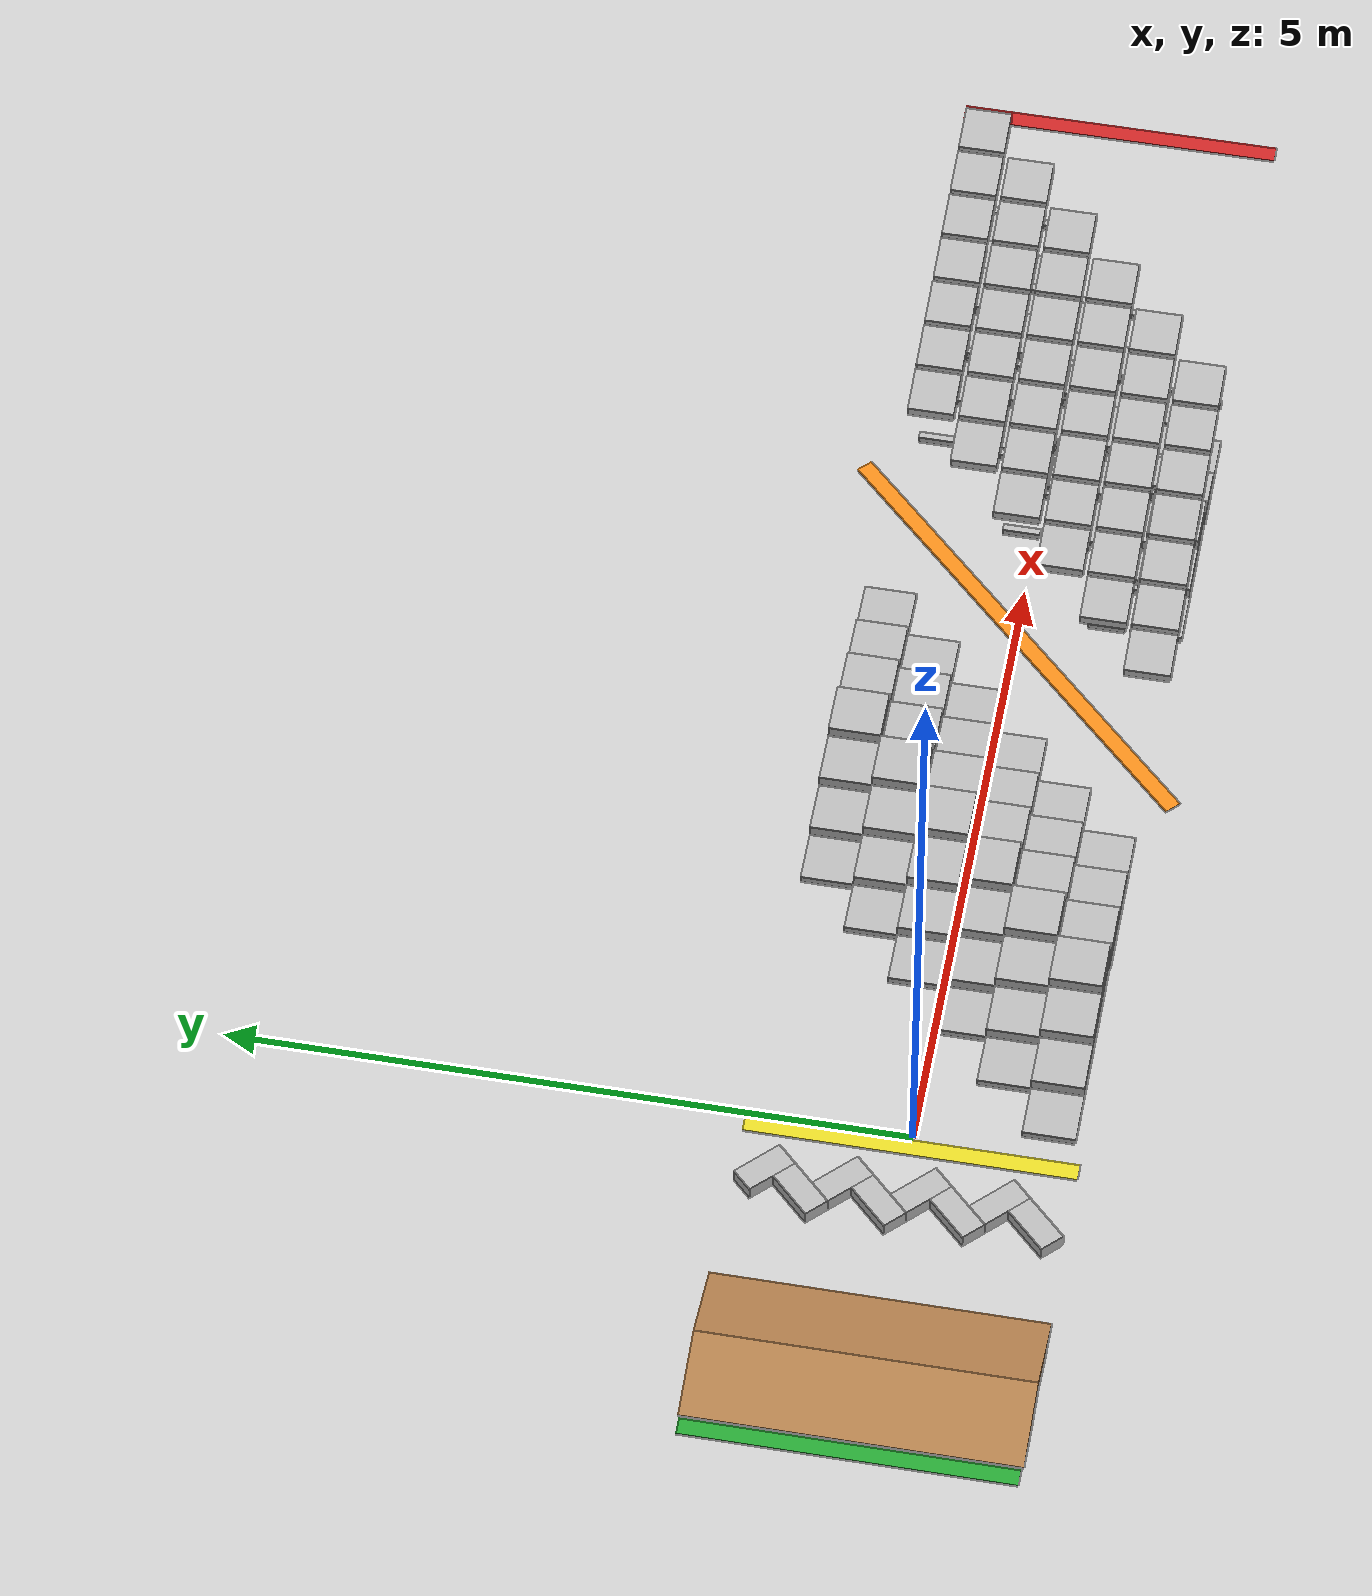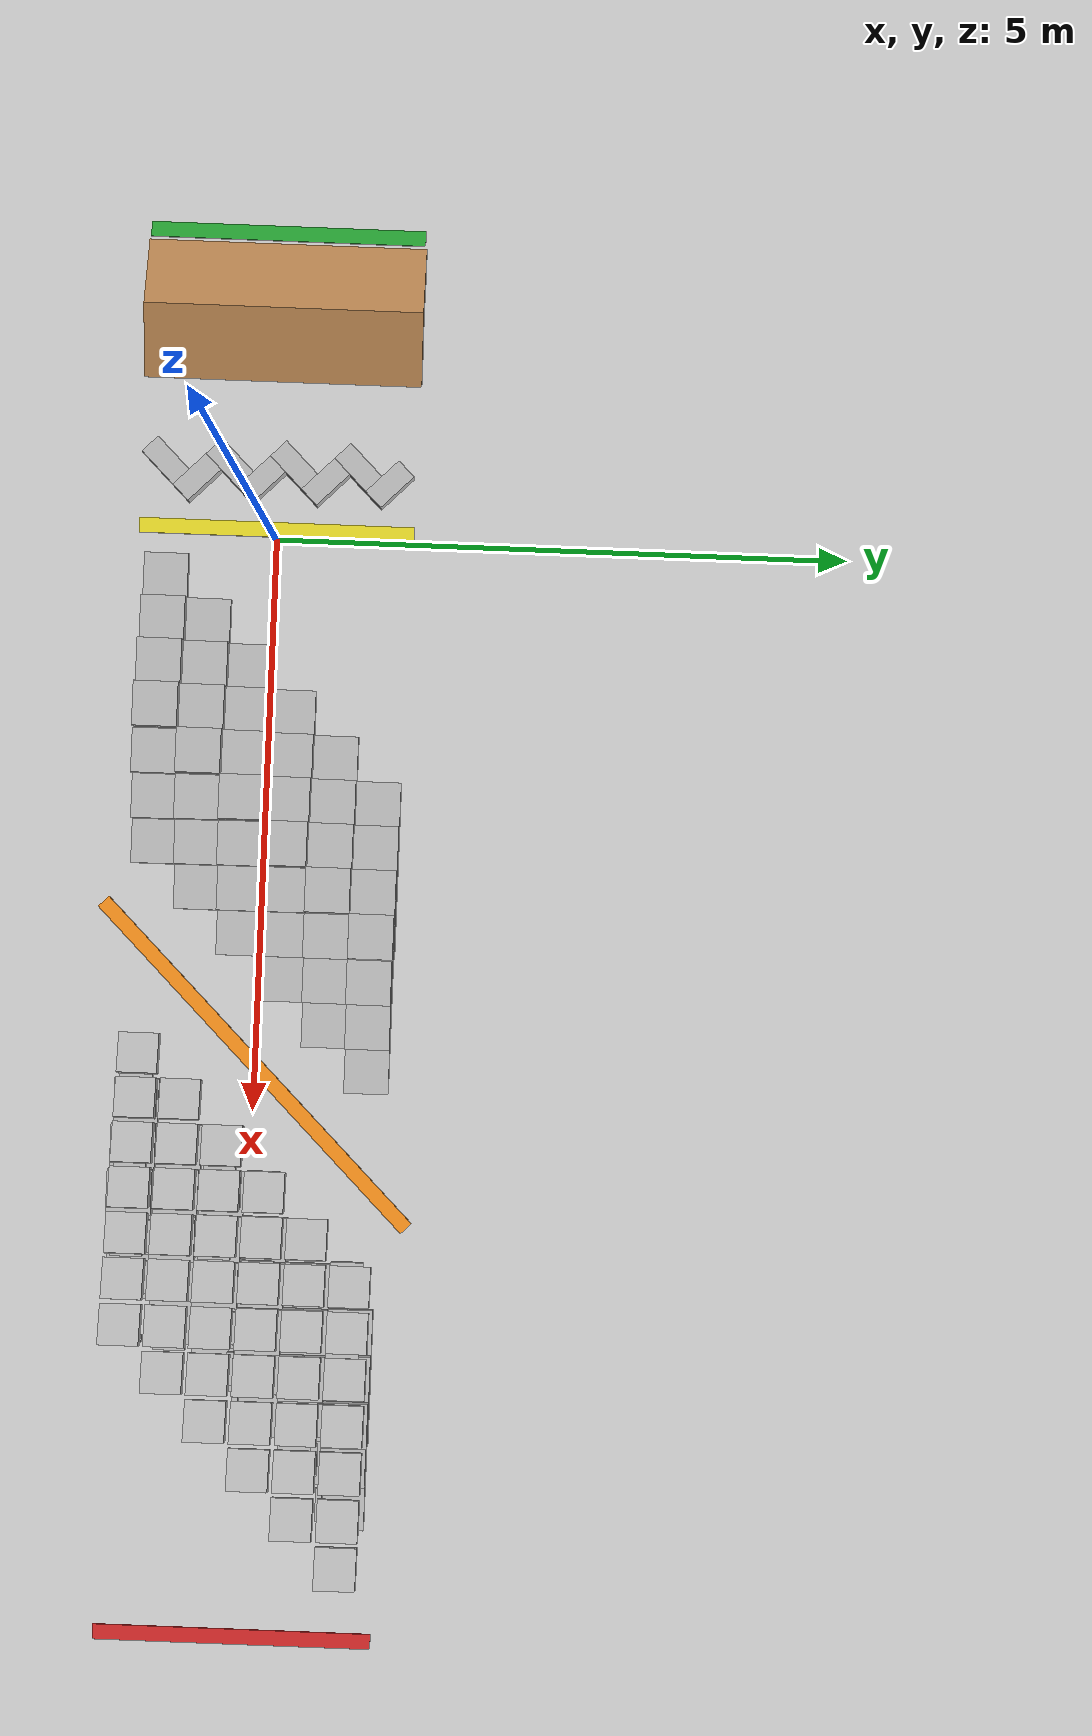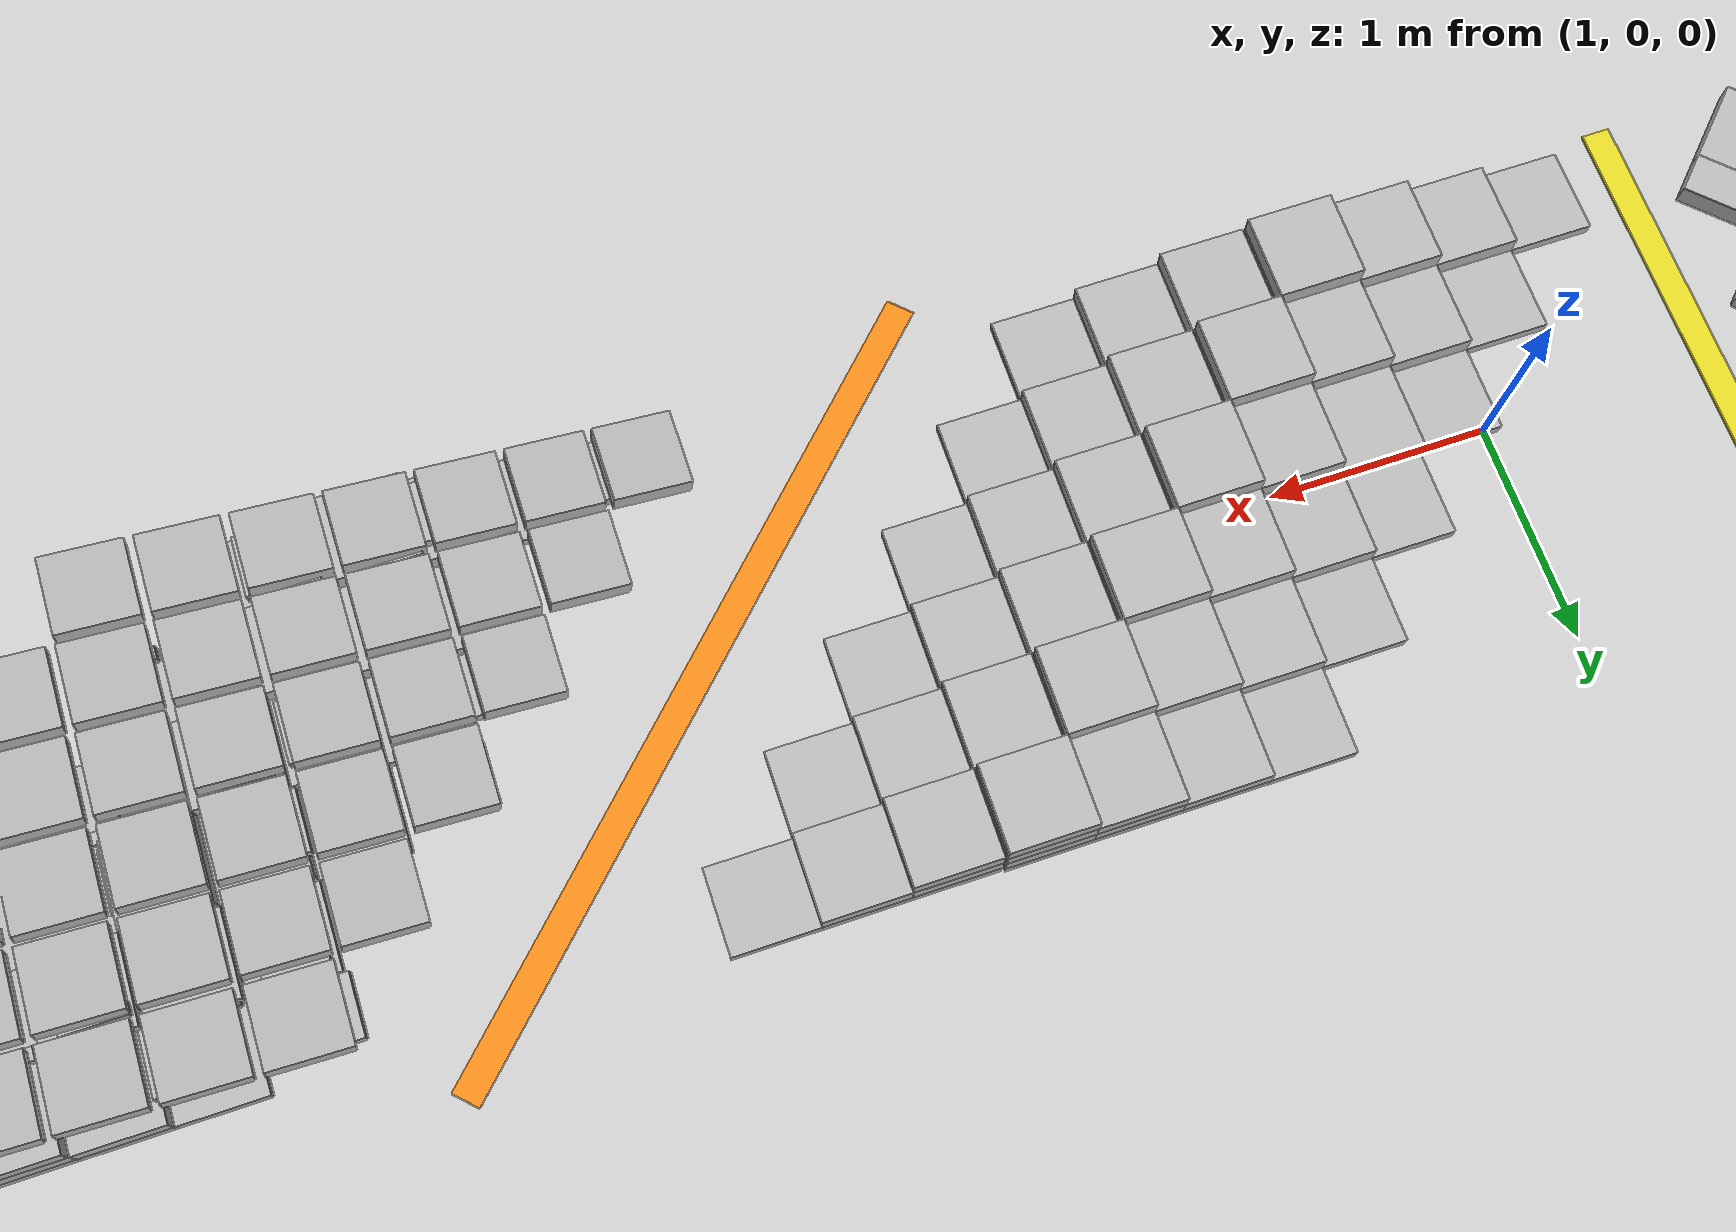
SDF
<sdf version="1.5">
 <world name="trials_task_2">
  <physics type="ode">
   <gravity>0 0 -9.81</gravity>
   <ode>
    <solver>
     <use_dynamic_moi_rescaling>1</use_dynamic_moi_rescaling>
     <type>quick</type>
     <iters>50</iters>
     <sor>1.4</sor>
    </solver>
    <constraints>
     <cfm>0</cfm>
     <erp>0.2</erp>
     <contact_max_correcting_vel>100</contact_max_correcting_vel>
     <contact_surface_layer>0</contact_surface_layer>
    </constraints>
   </ode>
   <real_time_update_rate>1000</real_time_update_rate>
   <max_step_size>0.001</max_step_size>
   <real_time_factor>1</real_time_factor>
   <magnetic_field>5.5645e-06 2.28758e-05 -4.23884e-05</magnetic_field>
  </physics>
  <light name="sun" type="directional">
   <pose>0 0 10 0 -0 0</pose>
   <diffuse>0.8 0.8 0.8 1</diffuse>
   <specular>0.2 0.2 0.2 1</specular>
   <attenuation>
    <range>1000</range>
    <constant>0.9</constant>
    <linear>0.01</linear>
    <quadratic>0.001</quadratic>
   </attenuation>
   <direction>-0.5 0.1 -0.9</direction>
  </light>
  <model name="ground_plane">
   <static>1</static>
   <link name="link">
    <collision name="collision">
     <geometry><plane><normal>0 0 1</normal><size>100 100</size></plane></geometry>
     <surface><friction><ode><mu>100</mu><mu2>50</mu2></ode></friction></surface>
    </collision>
    <visual name="visual">
     <cast_shadows>0</cast_shadows>
     <geometry><plane><normal>0 0 1</normal><size>100 100</size></plane></geometry>
     <material>
      <script><uri>file://media/materials/scripts/gazebo.material</uri><name>Gazebo/Grey</name></script>
     </material>
    </visual>
    <velocity_decay><linear>0</linear><angular>0</angular></velocity_decay>
   </link>
  </model>
  <model name="green_tape">
   <static>1</static>
   <pose>-2.7 0 0 0 -0 0</pose>
   <link name="link">
    <visual name="visual">
     <geometry><box><size>0.13 2.41 0.01</size></box></geometry>
     <material><script><name>Gazebo/Green</name><uri>__default__</uri></script></material>
    </visual>
    <velocity_decay><linear>0</linear><angular>0</angular></velocity_decay>
   </link>
  </model>
  <model name="ramp_0">
   <pose>-2 0 0 0 -0 0</pose>
   <static>1</static>
   <link name="link">
    <collision name="incline_collision">
     <pose>0.29175 0 0.0335 0 0.261799 0</pose>
     <geometry><box><size>0.631104 2.4384 0.1</size></box></geometry>
    </collision>
    <visual name="incline_visual">
     <pose>0.29175 0 0.0335 0 0.261799 0</pose>
     <geometry><box><size>0.631104 2.4384 0.1</size></box></geometry>
     <material><script><name>Gazebo/WoodFloor</name><uri>__default__</uri></script></material>
    </visual>
    <collision name="decline_collision">
     <pose>-0.29175 0 0.0335 0 -0.261799 0</pose>
     <geometry><box><size>0.631104 2.4384 0.1</size></box></geometry>
    </collision>
    <visual name="decline_visual">
     <pose>-0.29175 0 0.0335 0 -0.261799 0</pose>
     <geometry><box><size>0.631104 2.4384 0.1</size></box></geometry>
     <material><script><name>Gazebo/WoodFloor</name><uri>__default__</uri></script></material>
    </visual>
    <velocity_decay><linear>0</linear><angular>0</angular></velocity_decay>
   </link>
  </model>
  <model name="wall_2">
   <static>1</static>
   <pose>-4.7 -1.24739 0 0 -0 0</pose>
   <link name="block_0::link">
    <inertial>
     <pose>0 0 0.0714375 0 -0 0</pose>
     <mass>5</mass>
     <inertia>
      <ixx>0.06908</ixx>
      <ixy>0</ixy>
      <iyy>0.028705</iyy>
      <ixz>0</ixz>
      <iyz>0</iyz>
      <izz>0.073708</izz>
     </inertia>
    </inertial>
    <visual name="visual"><geometry><box><size>0.396875 0.19368 0.2</size></box></geometry></visual>
    <collision name="collision_box">
     <geometry><box><size>0.396875 0.19368 0.2</size></box></geometry>
     <surface>
      <contact><ode><max_vel>0.1</max_vel><min_depth>0.001</min_depth></ode></contact>
      <friction><ode><mu>1</mu><mu2>1</mu2></ode></friction>
     </surface>
    </collision>
    <velocity_decay><linear>0</linear><angular>0</angular></velocity_decay>
    <pose>4.05841 0.265175 0 0 -0 0.785398</pose>
   </link>
   <link name="block_3::link">
    <inertial>
     <pose>0 0 0.0714375 0 -0 0</pose>
     <mass>5</mass>
     <inertia>
      <ixx>0.06908</ixx>
      <ixy>0</ixy>
      <iyy>0.028705</iyy>
      <ixz>0</ixz>
      <iyz>0</iyz>
      <izz>0.073708</izz>
     </inertia>
    </inertial>
    <visual name="visual"><geometry><box><size>0.396875 0.19368 0.2</size></box></geometry></visual>
    <collision name="collision_box">
     <geometry><box><size>0.396875 0.19368 0.2</size></box></geometry>
     <surface>
      <contact><ode><max_vel>0.1</max_vel><min_depth>0.001</min_depth></ode></contact>
      <friction><ode><mu>1</mu><mu2>1</mu2></ode></friction>
     </surface>
    </collision>
    <velocity_decay><linear>0</linear><angular>0</angular></velocity_decay>
    <pose>4.19536 0.545809 0 0 0 -0.785398</pose>
   </link>
   <link name="block_5::link">
    <inertial>
     <pose>0 0 0.0714375 0 -0 0</pose>
     <mass>5</mass>
     <inertia>
      <ixx>0.06908</ixx>
      <ixy>0</ixy>
      <iyy>0.028705</iyy>
      <ixz>0</ixz>
      <iyz>0</iyz>
      <izz>0.073708</izz>
     </inertia>
    </inertial>
    <visual name="visual"><geometry><box><size>0.396875 0.19368 0.2</size></box></geometry></visual>
    <collision name="collision_box">
     <geometry><box><size>0.396875 0.19368 0.2</size></box></geometry>
     <surface>
      <contact><ode><max_vel>0.1</max_vel><min_depth>0.001</min_depth></ode></contact>
      <friction><ode><mu>1</mu><mu2>1</mu2></ode></friction>
     </surface>
    </collision>
    <velocity_decay><linear>0</linear><angular>0</angular></velocity_decay>
    <pose>4.05841 0.82644 0 0 -0 0.785398</pose>
   </link>
   <link name="block_7::link">
    <inertial>
     <pose>0 0 0.0714375 0 -0 0</pose>
     <mass>5</mass>
     <inertia>
      <ixx>0.06908</ixx>
      <ixy>0</ixy>
      <iyy>0.028705</iyy>
      <ixz>0</ixz>
      <iyz>0</iyz>
      <izz>0.073708</izz>
     </inertia>
    </inertial>
    <visual name="visual"><geometry><box><size>0.396875 0.19368 0.2</size></box></geometry></visual>
    <collision name="collision_box">
     <geometry><box><size>0.396875 0.19368 0.2</size></box></geometry>
     <surface>
      <contact><ode><max_vel>0.1</max_vel><min_depth>0.001</min_depth></ode></contact>
      <friction><ode><mu>1</mu><mu2>1</mu2></ode></friction>
     </surface>
    </collision>
    <velocity_decay><linear>0</linear><angular>0</angular></velocity_decay>
    <pose>4.19536 1.10707 0 0 0 -0.785398</pose>
   </link>
   <link name="block_9::link">
    <inertial>
     <pose>0 0 0.0714375 0 -0 0</pose>
     <mass>5</mass>
     <inertia>
      <ixx>0.06908</ixx>
      <ixy>0</ixy>
      <iyy>0.028705</iyy>
      <ixz>0</ixz>
      <iyz>0</iyz>
      <izz>0.073708</izz>
     </inertia>
    </inertial>
    <visual name="visual"><geometry><box><size>0.396875 0.19368 0.2</size></box></geometry></visual>
    <collision name="collision_box">
     <geometry><box><size>0.396875 0.19368 0.2</size></box></geometry>
     <surface>
      <contact><ode><max_vel>0.1</max_vel><min_depth>0.001</min_depth></ode></contact>
      <friction><ode><mu>1</mu><mu2>1</mu2></ode></friction>
     </surface>
    </collision>
    <velocity_decay><linear>0</linear><angular>0</angular></velocity_decay>
    <pose>4.05841 1.38771 0 0 -0 0.785398</pose>
   </link>
   <link name="block_11::link">
    <inertial>
     <pose>0 0 0.0714375 0 -0 0</pose>
     <mass>5</mass>
     <inertia>
      <ixx>0.06908</ixx>
      <ixy>0</ixy>
      <iyy>0.028705</iyy>
      <ixz>0</ixz>
      <iyz>0</iyz>
      <izz>0.073708</izz>
     </inertia>
    </inertial>
    <visual name="visual"><geometry><box><size>0.396875 0.19368 0.2</size></box></geometry></visual>
    <collision name="collision_box">
     <geometry><box><size>0.396875 0.19368 0.2</size></box></geometry>
     <surface>
      <contact><ode><max_vel>0.1</max_vel><min_depth>0.001</min_depth></ode></contact>
      <friction><ode><mu>1</mu><mu2>1</mu2></ode></friction>
     </surface>
    </collision>
    <velocity_decay><linear>0</linear><angular>0</angular></velocity_decay>
    <pose>4.19536 1.66834 0 0 0 -0.785398</pose>
   </link>
   <link name="block_13::link">
    <inertial>
     <pose>0 0 0.0714375 0 -0 0</pose>
     <mass>5</mass>
     <inertia>
      <ixx>0.06908</ixx>
      <ixy>0</ixy>
      <iyy>0.028705</iyy>
      <ixz>0</ixz>
      <iyz>0</iyz>
      <izz>0.073708</izz>
     </inertia>
    </inertial>
    <visual name="visual"><geometry><box><size>0.396875 0.19368 0.2</size></box></geometry></visual>
    <collision name="collision_box">
     <geometry><box><size>0.396875 0.19368 0.2</size></box></geometry>
     <surface>
      <contact><ode><max_vel>0.1</max_vel><min_depth>0.001</min_depth></ode></contact>
      <friction><ode><mu>1</mu><mu2>1</mu2></ode></friction>
     </surface>
    </collision>
    <velocity_decay><linear>0</linear><angular>0</angular></velocity_decay>
    <pose>4.05841 1.94897 0 0 -0 0.785398</pose>
   </link>
   <link name="block_15::link">
    <inertial>
     <pose>0 0 0.0714375 0 -0 0</pose>
     <mass>5</mass>
     <inertia>
      <ixx>0.06908</ixx>
      <ixy>0</ixy>
      <iyy>0.028705</iyy>
      <ixz>0</ixz>
      <iyz>0</iyz>
      <izz>0.073708</izz>
     </inertia>
    </inertial>
    <visual name="visual"><geometry><box><size>0.396875 0.19368 0.2</size></box></geometry></visual>
    <collision name="collision_box">
     <geometry><box><size>0.396875 0.19368 0.2</size></box></geometry>
     <surface>
      <contact><ode><max_vel>0.1</max_vel><min_depth>0.001</min_depth></ode></contact>
      <friction><ode><mu>1</mu><mu2>1</mu2></ode></friction>
     </surface>
    </collision>
    <velocity_decay><linear>0</linear><angular>0</angular></velocity_decay>
    <pose>4.19536 2.2296 0 0 0 -0.785398</pose>
   </link>
  </model>
  <model name="yellow_tape">
   <static>1</static>
   <pose>-0.087 0 0 0 -0 0</pose>
   <link name="link">
    <visual name="visual">
     <geometry><box><size>0.13 2.41 0.01</size></box></geometry>
     <material><script><name>Gazebo/Yellow</name><uri>__default__</uri></script></material>
    </visual>
    <velocity_decay><linear>0</linear><angular>0</angular></velocity_decay>
   </link>
  </model>
  <model name="level_block_1">
   <pose>0.351 -0.949 0 0 -0 0</pose>
   <link name="block_0_0_0::link">
    <inertial>
     <pose>0 0 0.0714375 0 -0 0</pose>
     <mass>5</mass>
     <inertia>
      <ixx>0.0681466</ixx>
      <ixy>0</ixy>
      <iyy>0.0681466</iyy>
      <ixz>0</ixz>
      <iyz>0</iyz>
      <izz>0.124808</izz>
     </inertia>
    </inertial>
    <visual name="visual"><geometry><box><size>0.387354 0.387354 0.092075</size></box></geometry></visual>
    <collision name="block_collision">
     <geometry><box><size>0.387354 0.387354 0.092075</size></box></geometry>
     <surface>
      <contact><ode><max_vel>0.1</max_vel><min_depth>0.001</min_depth></ode></contact>
      <friction><ode><mu>1</mu><mu2>1</mu2></ode></friction>
     </surface>
    </collision>
    <velocity_decay><linear>0</linear><angular>0</angular></velocity_decay>
    <pose>0 0 0 0 -0 1.5708</pose>
   </link>
   <link name="block_0_1_1::link">
    <inertial>
     <pose>0 0 0.0714375 0 -0 0</pose>
     <mass>5</mass>
     <inertia>
      <ixx>0.0681466</ixx>
      <ixy>0</ixy>
      <iyy>0.0681466</iyy>
      <ixz>0</ixz>
      <iyz>0</iyz>
      <izz>0.124808</izz>
     </inertia>
    </inertial>
    <visual name="visual"><geometry><box><size>0.387354 0.387354 0.092075</size></box></geometry></visual>
    <collision name="block_collision">
     <geometry><box><size>0.387354 0.387354 0.092075</size></box></geometry>
     <surface>
      <contact><ode><max_vel>0.1</max_vel><min_depth>0.001</min_depth></ode></contact>
      <friction><ode><mu>1</mu><mu2>1</mu2></ode></friction>
     </surface>
    </collision>
    <velocity_decay><linear>0</linear><angular>0</angular></velocity_decay>
    <pose>0.387354 0 0.093 0 -0 1.5708</pose>
   </link>
   <link name="block_0_1_0::link">
    <inertial>
     <pose>0 0 0.0714375 0 -0 0</pose>
     <mass>5</mass>
     <inertia>
      <ixx>0.0681466</ixx>
      <ixy>0</ixy>
      <iyy>0.0681466</iyy>
      <ixz>0</ixz>
      <iyz>0</iyz>
      <izz>0.124808</izz>
     </inertia>
    </inertial>
    <visual name="visual"><geometry><box><size>0.387354 0.387354 0.092075</size></box></geometry></visual>
    <collision name="block_collision">
     <geometry><box><size>0.387354 0.387354 0.092075</size></box></geometry>
     <surface>
      <contact><ode><max_vel>0.1</max_vel><min_depth>0.001</min_depth></ode></contact>
      <friction><ode><mu>1</mu><mu2>1</mu2></ode></friction>
     </surface>
    </collision>
    <velocity_decay><linear>0</linear><angular>0</angular></velocity_decay>
    <pose>0.387354 0 0 0 -0 1.5708</pose>
   </link>
   <link name="block_0_2_2::link">
    <inertial>
     <pose>0 0 0.0714375 0 -0 0</pose>
     <mass>5</mass>
     <inertia>
      <ixx>0.0681466</ixx>
      <ixy>0</ixy>
      <iyy>0.0681466</iyy>
      <ixz>0</ixz>
      <iyz>0</iyz>
      <izz>0.124808</izz>
     </inertia>
    </inertial>
    <visual name="visual"><geometry><box><size>0.387354 0.387354 0.092075</size></box></geometry></visual>
    <collision name="block_collision">
     <geometry><box><size>0.387354 0.387354 0.092075</size></box></geometry>
     <surface>
      <contact><ode><max_vel>0.1</max_vel><min_depth>0.001</min_depth></ode></contact>
      <friction><ode><mu>1</mu><mu2>1</mu2></ode></friction>
     </surface>
    </collision>
    <velocity_decay><linear>0</linear><angular>0</angular></velocity_decay>
    <pose>0.774707 0 0.186 0 -0 1.5708</pose>
   </link>
   <link name="block_0_2_1::link">
    <inertial>
     <pose>0 0 0.0714375 0 -0 0</pose>
     <mass>5</mass>
     <inertia>
      <ixx>0.0681466</ixx>
      <ixy>0</ixy>
      <iyy>0.0681466</iyy>
      <ixz>0</ixz>
      <iyz>0</iyz>
      <izz>0.124808</izz>
     </inertia>
    </inertial>
    <visual name="visual"><geometry><box><size>0.387354 0.387354 0.092075</size></box></geometry></visual>
    <collision name="block_collision">
     <geometry><box><size>0.387354 0.387354 0.092075</size></box></geometry>
     <surface>
      <contact><ode><max_vel>0.1</max_vel><min_depth>0.001</min_depth></ode></contact>
      <friction><ode><mu>1</mu><mu2>1</mu2></ode></friction>
     </surface>
    </collision>
    <velocity_decay><linear>0</linear><angular>0</angular></velocity_decay>
    <pose>0.774707 0 0.093 0 -0 1.5708</pose>
   </link>
   <link name="block_0_2_0::link">
    <inertial>
     <pose>0 0 0.0714375 0 -0 0</pose>
     <mass>5</mass>
     <inertia>
      <ixx>0.0681466</ixx>
      <ixy>0</ixy>
      <iyy>0.0681466</iyy>
      <ixz>0</ixz>
      <iyz>0</iyz>
      <izz>0.124808</izz>
     </inertia>
    </inertial>
    <visual name="visual"><geometry><box><size>0.387354 0.387354 0.092075</size></box></geometry></visual>
    <collision name="block_collision">
     <geometry><box><size>0.387354 0.387354 0.092075</size></box></geometry>
     <surface>
      <contact><ode><max_vel>0.1</max_vel><min_depth>0.001</min_depth></ode></contact>
      <friction><ode><mu>1</mu><mu2>1</mu2></ode></friction>
     </surface>
    </collision>
    <velocity_decay><linear>0</linear><angular>0</angular></velocity_decay>
    <pose>0.774707 0 0 0 -0 1.5708</pose>
   </link>
   <link name="block_0_3_3::link">
    <inertial>
     <pose>0 0 0.0714375 0 -0 0</pose>
     <mass>5</mass>
     <inertia>
      <ixx>0.0681466</ixx>
      <ixy>0</ixy>
      <iyy>0.0681466</iyy>
      <ixz>0</ixz>
      <iyz>0</iyz>
      <izz>0.124808</izz>
     </inertia>
    </inertial>
    <visual name="visual"><geometry><box><size>0.387354 0.387354 0.092075</size></box></geometry></visual>
    <collision name="block_collision">
     <geometry><box><size>0.387354 0.387354 0.092075</size></box></geometry>
     <surface>
      <contact><ode><max_vel>0.1</max_vel><min_depth>0.001</min_depth></ode></contact>
      <friction><ode><mu>1</mu><mu2>1</mu2></ode></friction>
     </surface>
    </collision>
    <velocity_decay><linear>0</linear><angular>0</angular></velocity_decay>
    <pose>1.16206 0 0.279 0 -0 1.5708</pose>
   </link>
   <link name="block_0_3_2::link">
    <inertial>
     <pose>0 0 0.0714375 0 -0 0</pose>
     <mass>5</mass>
     <inertia>
      <ixx>0.0681466</ixx>
      <ixy>0</ixy>
      <iyy>0.0681466</iyy>
      <ixz>0</ixz>
      <iyz>0</iyz>
      <izz>0.124808</izz>
     </inertia>
    </inertial>
    <visual name="visual"><geometry><box><size>0.387354 0.387354 0.092075</size></box></geometry></visual>
    <collision name="block_collision">
     <geometry><box><size>0.387354 0.387354 0.092075</size></box></geometry>
     <surface>
      <contact><ode><max_vel>0.1</max_vel><min_depth>0.001</min_depth></ode></contact>
      <friction><ode><mu>1</mu><mu2>1</mu2></ode></friction>
     </surface>
    </collision>
    <velocity_decay><linear>0</linear><angular>0</angular></velocity_decay>
    <pose>1.16206 0 0.186 0 -0 1.5708</pose>
   </link>
   <link name="block_0_3_1::link">
    <inertial>
     <pose>0 0 0.0714375 0 -0 0</pose>
     <mass>5</mass>
     <inertia>
      <ixx>0.0681466</ixx>
      <ixy>0</ixy>
      <iyy>0.0681466</iyy>
      <ixz>0</ixz>
      <iyz>0</iyz>
      <izz>0.124808</izz>
     </inertia>
    </inertial>
    <visual name="visual"><geometry><box><size>0.387354 0.387354 0.092075</size></box></geometry></visual>
    <collision name="block_collision">
     <geometry><box><size>0.387354 0.387354 0.092075</size></box></geometry>
     <surface>
      <contact><ode><max_vel>0.1</max_vel><min_depth>0.001</min_depth></ode></contact>
      <friction><ode><mu>1</mu><mu2>1</mu2></ode></friction>
     </surface>
    </collision>
    <velocity_decay><linear>0</linear><angular>0</angular></velocity_decay>
    <pose>1.16206 0 0.093 0 -0 1.5708</pose>
   </link>
   <link name="block_0_3_0::link">
    <inertial>
     <pose>0 0 0.0714375 0 -0 0</pose>
     <mass>5</mass>
     <inertia>
      <ixx>0.0681466</ixx>
      <ixy>0</ixy>
      <iyy>0.0681466</iyy>
      <ixz>0</ixz>
      <iyz>0</iyz>
      <izz>0.124808</izz>
     </inertia>
    </inertial>
    <visual name="visual"><geometry><box><size>0.387354 0.387354 0.092075</size></box></geometry></visual>
    <collision name="block_collision">
     <geometry><box><size>0.387354 0.387354 0.092075</size></box></geometry>
     <surface>
      <contact><ode><max_vel>0.1</max_vel><min_depth>0.001</min_depth></ode></contact>
      <friction><ode><mu>1</mu><mu2>1</mu2></ode></friction>
     </surface>
    </collision>
    <velocity_decay><linear>0</linear><angular>0</angular></velocity_decay>
    <pose>1.16206 0 0 0 -0 1.5708</pose>
   </link>
   <link name="block_1_0_0::link">
    <inertial>
     <pose>0 0 0.0714375 0 -0 0</pose>
     <mass>5</mass>
     <inertia>
      <ixx>0.0681466</ixx>
      <ixy>0</ixy>
      <iyy>0.0681466</iyy>
      <ixz>0</ixz>
      <iyz>0</iyz>
      <izz>0.124808</izz>
     </inertia>
    </inertial>
    <visual name="visual"><geometry><box><size>0.387354 0.387354 0.092075</size></box></geometry></visual>
    <collision name="block_collision">
     <geometry><box><size>0.387354 0.387354 0.092075</size></box></geometry>
     <surface>
      <contact><ode><max_vel>0.1</max_vel><min_depth>0.001</min_depth></ode></contact>
      <friction><ode><mu>1</mu><mu2>1</mu2></ode></friction>
     </surface>
    </collision>
    <velocity_decay><linear>0</linear><angular>0</angular></velocity_decay>
    <pose>0.387354 0.387354 0 0 -0 1.5708</pose>
   </link>
   <link name="block_1_1_1::link">
    <inertial>
     <pose>0 0 0.0714375 0 -0 0</pose>
     <mass>5</mass>
     <inertia>
      <ixx>0.0681466</ixx>
      <ixy>0</ixy>
      <iyy>0.0681466</iyy>
      <ixz>0</ixz>
      <iyz>0</iyz>
      <izz>0.124808</izz>
     </inertia>
    </inertial>
    <visual name="visual"><geometry><box><size>0.387354 0.387354 0.092075</size></box></geometry></visual>
    <collision name="block_collision">
     <geometry><box><size>0.387354 0.387354 0.092075</size></box></geometry>
     <surface>
      <contact><ode><max_vel>0.1</max_vel><min_depth>0.001</min_depth></ode></contact>
      <friction><ode><mu>1</mu><mu2>1</mu2></ode></friction>
     </surface>
    </collision>
    <velocity_decay><linear>0</linear><angular>0</angular></velocity_decay>
    <pose>0.774707 0.387354 0.093 0 -0 1.5708</pose>
   </link>
   <link name="block_1_1_0::link">
    <inertial>
     <pose>0 0 0.0714375 0 -0 0</pose>
     <mass>5</mass>
     <inertia>
      <ixx>0.0681466</ixx>
      <ixy>0</ixy>
      <iyy>0.0681466</iyy>
      <ixz>0</ixz>
      <iyz>0</iyz>
      <izz>0.124808</izz>
     </inertia>
    </inertial>
    <visual name="visual"><geometry><box><size>0.387354 0.387354 0.092075</size></box></geometry></visual>
    <collision name="block_collision">
     <geometry><box><size>0.387354 0.387354 0.092075</size></box></geometry>
     <surface>
      <contact><ode><max_vel>0.1</max_vel><min_depth>0.001</min_depth></ode></contact>
      <friction><ode><mu>1</mu><mu2>1</mu2></ode></friction>
     </surface>
    </collision>
    <velocity_decay><linear>0</linear><angular>0</angular></velocity_decay>
    <pose>0.774707 0.387354 0 0 -0 1.5708</pose>
   </link>
   <link name="block_1_2_2::link">
    <inertial>
     <pose>0 0 0.0714375 0 -0 0</pose>
     <mass>5</mass>
     <inertia>
      <ixx>0.0681466</ixx>
      <ixy>0</ixy>
      <iyy>0.0681466</iyy>
      <ixz>0</ixz>
      <iyz>0</iyz>
      <izz>0.124808</izz>
     </inertia>
    </inertial>
    <visual name="visual"><geometry><box><size>0.387354 0.387354 0.092075</size></box></geometry></visual>
    <collision name="block_collision">
     <geometry><box><size>0.387354 0.387354 0.092075</size></box></geometry>
     <surface>
      <contact><ode><max_vel>0.1</max_vel><min_depth>0.001</min_depth></ode></contact>
      <friction><ode><mu>1</mu><mu2>1</mu2></ode></friction>
     </surface>
    </collision>
    <velocity_decay><linear>0</linear><angular>0</angular></velocity_decay>
    <pose>1.16206 0.387354 0.186 0 -0 1.5708</pose>
   </link>
   <link name="block_1_2_1::link">
    <inertial>
     <pose>0 0 0.0714375 0 -0 0</pose>
     <mass>5</mass>
     <inertia>
      <ixx>0.0681466</ixx>
      <ixy>0</ixy>
      <iyy>0.0681466</iyy>
      <ixz>0</ixz>
      <iyz>0</iyz>
      <izz>0.124808</izz>
     </inertia>
    </inertial>
    <visual name="visual"><geometry><box><size>0.387354 0.387354 0.092075</size></box></geometry></visual>
    <collision name="block_collision">
     <geometry><box><size>0.387354 0.387354 0.092075</size></box></geometry>
     <surface>
      <contact><ode><max_vel>0.1</max_vel><min_depth>0.001</min_depth></ode></contact>
      <friction><ode><mu>1</mu><mu2>1</mu2></ode></friction>
     </surface>
    </collision>
    <velocity_decay><linear>0</linear><angular>0</angular></velocity_decay>
    <pose>1.16206 0.387354 0.093 0 -0 1.5708</pose>
   </link>
   <link name="block_1_2_0::link">
    <inertial>
     <pose>0 0 0.0714375 0 -0 0</pose>
     <mass>5</mass>
     <inertia>
      <ixx>0.0681466</ixx>
      <ixy>0</ixy>
      <iyy>0.0681466</iyy>
      <ixz>0</ixz>
      <iyz>0</iyz>
      <izz>0.124808</izz>
     </inertia>
    </inertial>
    <visual name="visual"><geometry><box><size>0.387354 0.387354 0.092075</size></box></geometry></visual>
    <collision name="block_collision">
     <geometry><box><size>0.387354 0.387354 0.092075</size></box></geometry>
     <surface>
      <contact><ode><max_vel>0.1</max_vel><min_depth>0.001</min_depth></ode></contact>
      <friction><ode><mu>1</mu><mu2>1</mu2></ode></friction>
     </surface>
    </collision>
    <velocity_decay><linear>0</linear><angular>0</angular></velocity_decay>
    <pose>1.16206 0.387354 0 0 -0 1.5708</pose>
   </link>
   <link name="block_1_3_3::link">
    <inertial>
     <pose>0 0 0.0714375 0 -0 0</pose>
     <mass>5</mass>
     <inertia>
      <ixx>0.0681466</ixx>
      <ixy>0</ixy>
      <iyy>0.0681466</iyy>
      <ixz>0</ixz>
      <iyz>0</iyz>
      <izz>0.124808</izz>
     </inertia>
    </inertial>
    <visual name="visual"><geometry><box><size>0.387354 0.387354 0.092075</size></box></geometry></visual>
    <collision name="block_collision">
     <geometry><box><size>0.387354 0.387354 0.092075</size></box></geometry>
     <surface>
      <contact><ode><max_vel>0.1</max_vel><min_depth>0.001</min_depth></ode></contact>
      <friction><ode><mu>1</mu><mu2>1</mu2></ode></friction>
     </surface>
    </collision>
    <velocity_decay><linear>0</linear><angular>0</angular></velocity_decay>
    <pose>1.54941 0.387354 0.279 0 -0 1.5708</pose>
   </link>
   <link name="block_1_3_2::link">
    <inertial>
     <pose>0 0 0.0714375 0 -0 0</pose>
     <mass>5</mass>
     <inertia>
      <ixx>0.0681466</ixx>
      <ixy>0</ixy>
      <iyy>0.0681466</iyy>
      <ixz>0</ixz>
      <iyz>0</iyz>
      <izz>0.124808</izz>
     </inertia>
    </inertial>
    <visual name="visual"><geometry><box><size>0.387354 0.387354 0.092075</size></box></geometry></visual>
    <collision name="block_collision">
     <geometry><box><size>0.387354 0.387354 0.092075</size></box></geometry>
     <surface>
      <contact><ode><max_vel>0.1</max_vel><min_depth>0.001</min_depth></ode></contact>
      <friction><ode><mu>1</mu><mu2>1</mu2></ode></friction>
     </surface>
    </collision>
    <velocity_decay><linear>0</linear><angular>0</angular></velocity_decay>
    <pose>1.54941 0.387354 0.186 0 -0 1.5708</pose>
   </link>
   <link name="block_1_3_1::link">
    <inertial>
     <pose>0 0 0.0714375 0 -0 0</pose>
     <mass>5</mass>
     <inertia>
      <ixx>0.0681466</ixx>
      <ixy>0</ixy>
      <iyy>0.0681466</iyy>
      <ixz>0</ixz>
      <iyz>0</iyz>
      <izz>0.124808</izz>
     </inertia>
    </inertial>
    <visual name="visual"><geometry><box><size>0.387354 0.387354 0.092075</size></box></geometry></visual>
    <collision name="block_collision">
     <geometry><box><size>0.387354 0.387354 0.092075</size></box></geometry>
     <surface>
      <contact><ode><max_vel>0.1</max_vel><min_depth>0.001</min_depth></ode></contact>
      <friction><ode><mu>1</mu><mu2>1</mu2></ode></friction>
     </surface>
    </collision>
    <velocity_decay><linear>0</linear><angular>0</angular></velocity_decay>
    <pose>1.54941 0.387354 0.093 0 -0 1.5708</pose>
   </link>
   <link name="block_1_3_0::link">
    <inertial>
     <pose>0 0 0.0714375 0 -0 0</pose>
     <mass>5</mass>
     <inertia>
      <ixx>0.0681466</ixx>
      <ixy>0</ixy>
      <iyy>0.0681466</iyy>
      <ixz>0</ixz>
      <iyz>0</iyz>
      <izz>0.124808</izz>
     </inertia>
    </inertial>
    <visual name="visual"><geometry><box><size>0.387354 0.387354 0.092075</size></box></geometry></visual>
    <collision name="block_collision">
     <geometry><box><size>0.387354 0.387354 0.092075</size></box></geometry>
     <surface>
      <contact><ode><max_vel>0.1</max_vel><min_depth>0.001</min_depth></ode></contact>
      <friction><ode><mu>1</mu><mu2>1</mu2></ode></friction>
     </surface>
    </collision>
    <velocity_decay><linear>0</linear><angular>0</angular></velocity_decay>
    <pose>1.54941 0.387354 0 0 -0 1.5708</pose>
   </link>
   <link name="block_2_0_0::link">
    <inertial>
     <pose>0 0 0.0714375 0 -0 0</pose>
     <mass>5</mass>
     <inertia>
      <ixx>0.0681466</ixx>
      <ixy>0</ixy>
      <iyy>0.0681466</iyy>
      <ixz>0</ixz>
      <iyz>0</iyz>
      <izz>0.124808</izz>
     </inertia>
    </inertial>
    <visual name="visual"><geometry><box><size>0.387354 0.387354 0.092075</size></box></geometry></visual>
    <collision name="block_collision">
     <geometry><box><size>0.387354 0.387354 0.092075</size></box></geometry>
     <surface>
      <contact><ode><max_vel>0.1</max_vel><min_depth>0.001</min_depth></ode></contact>
      <friction><ode><mu>1</mu><mu2>1</mu2></ode></friction>
     </surface>
    </collision>
    <velocity_decay><linear>0</linear><angular>0</angular></velocity_decay>
    <pose>0.774707 0.774707 0 0 -0 1.5708</pose>
   </link>
   <link name="block_2_1_1::link">
    <inertial>
     <pose>0 0 0.0714375 0 -0 0</pose>
     <mass>5</mass>
     <inertia>
      <ixx>0.0681466</ixx>
      <ixy>0</ixy>
      <iyy>0.0681466</iyy>
      <ixz>0</ixz>
      <iyz>0</iyz>
      <izz>0.124808</izz>
     </inertia>
    </inertial>
    <visual name="visual"><geometry><box><size>0.387354 0.387354 0.092075</size></box></geometry></visual>
    <collision name="block_collision">
     <geometry><box><size>0.387354 0.387354 0.092075</size></box></geometry>
     <surface>
      <contact><ode><max_vel>0.1</max_vel><min_depth>0.001</min_depth></ode></contact>
      <friction><ode><mu>1</mu><mu2>1</mu2></ode></friction>
     </surface>
    </collision>
    <velocity_decay><linear>0</linear><angular>0</angular></velocity_decay>
    <pose>1.16206 0.774707 0.093 0 -0 1.5708</pose>
   </link>
   <link name="block_2_1_0::link">
    <inertial>
     <pose>0 0 0.0714375 0 -0 0</pose>
     <mass>5</mass>
     <inertia>
      <ixx>0.0681466</ixx>
      <ixy>0</ixy>
      <iyy>0.0681466</iyy>
      <ixz>0</ixz>
      <iyz>0</iyz>
      <izz>0.124808</izz>
     </inertia>
    </inertial>
    <visual name="visual"><geometry><box><size>0.387354 0.387354 0.092075</size></box></geometry></visual>
    <collision name="block_collision">
     <geometry><box><size>0.387354 0.387354 0.092075</size></box></geometry>
     <surface>
      <contact><ode><max_vel>0.1</max_vel><min_depth>0.001</min_depth></ode></contact>
      <friction><ode><mu>1</mu><mu2>1</mu2></ode></friction>
     </surface>
    </collision>
    <velocity_decay><linear>0</linear><angular>0</angular></velocity_decay>
    <pose>1.16206 0.774707 0 0 -0 1.5708</pose>
   </link>
   <link name="block_2_2_2::link">
    <inertial>
     <pose>0 0 0.0714375 0 -0 0</pose>
     <mass>5</mass>
     <inertia>
      <ixx>0.0681466</ixx>
      <ixy>0</ixy>
      <iyy>0.0681466</iyy>
      <ixz>0</ixz>
      <iyz>0</iyz>
      <izz>0.124808</izz>
     </inertia>
    </inertial>
    <visual name="visual"><geometry><box><size>0.387354 0.387354 0.092075</size></box></geometry></visual>
    <collision name="block_collision">
     <geometry><box><size>0.387354 0.387354 0.092075</size></box></geometry>
     <surface>
      <contact><ode><max_vel>0.1</max_vel><min_depth>0.001</min_depth></ode></contact>
      <friction><ode><mu>1</mu><mu2>1</mu2></ode></friction>
     </surface>
    </collision>
    <velocity_decay><linear>0</linear><angular>0</angular></velocity_decay>
    <pose>1.54941 0.774707 0.186 0 -0 1.5708</pose>
   </link>
   <link name="block_2_2_1::link">
    <inertial>
     <pose>0 0 0.0714375 0 -0 0</pose>
     <mass>5</mass>
     <inertia>
      <ixx>0.0681466</ixx>
      <ixy>0</ixy>
      <iyy>0.0681466</iyy>
      <ixz>0</ixz>
      <iyz>0</iyz>
      <izz>0.124808</izz>
     </inertia>
    </inertial>
    <visual name="visual"><geometry><box><size>0.387354 0.387354 0.092075</size></box></geometry></visual>
    <collision name="block_collision">
     <geometry><box><size>0.387354 0.387354 0.092075</size></box></geometry>
     <surface>
      <contact><ode><max_vel>0.1</max_vel><min_depth>0.001</min_depth></ode></contact>
      <friction><ode><mu>1</mu><mu2>1</mu2></ode></friction>
     </surface>
    </collision>
    <velocity_decay><linear>0</linear><angular>0</angular></velocity_decay>
    <pose>1.54941 0.774707 0.093 0 -0 1.5708</pose>
   </link>
   <link name="block_2_2_0::link">
    <inertial>
     <pose>0 0 0.0714375 0 -0 0</pose>
     <mass>5</mass>
     <inertia>
      <ixx>0.0681466</ixx>
      <ixy>0</ixy>
      <iyy>0.0681466</iyy>
      <ixz>0</ixz>
      <iyz>0</iyz>
      <izz>0.124808</izz>
     </inertia>
    </inertial>
    <visual name="visual"><geometry><box><size>0.387354 0.387354 0.092075</size></box></geometry></visual>
    <collision name="block_collision">
     <geometry><box><size>0.387354 0.387354 0.092075</size></box></geometry>
     <surface>
      <contact><ode><max_vel>0.1</max_vel><min_depth>0.001</min_depth></ode></contact>
      <friction><ode><mu>1</mu><mu2>1</mu2></ode></friction>
     </surface>
    </collision>
    <velocity_decay><linear>0</linear><angular>0</angular></velocity_decay>
    <pose>1.54941 0.774707 0 0 -0 1.5708</pose>
   </link>
   <link name="block_2_3_3::link">
    <inertial>
     <pose>0 0 0.0714375 0 -0 0</pose>
     <mass>5</mass>
     <inertia>
      <ixx>0.0681466</ixx>
      <ixy>0</ixy>
      <iyy>0.0681466</iyy>
      <ixz>0</ixz>
      <iyz>0</iyz>
      <izz>0.124808</izz>
     </inertia>
    </inertial>
    <visual name="visual"><geometry><box><size>0.387354 0.387354 0.092075</size></box></geometry></visual>
    <collision name="block_collision">
     <geometry><box><size>0.387354 0.387354 0.092075</size></box></geometry>
     <surface>
      <contact><ode><max_vel>0.1</max_vel><min_depth>0.001</min_depth></ode></contact>
      <friction><ode><mu>1</mu><mu2>1</mu2></ode></friction>
     </surface>
    </collision>
    <velocity_decay><linear>0</linear><angular>0</angular></velocity_decay>
    <pose>1.93677 0.774707 0.279 0 -0 1.5708</pose>
   </link>
   <link name="block_2_3_2::link">
    <inertial>
     <pose>0 0 0.0714375 0 -0 0</pose>
     <mass>5</mass>
     <inertia>
      <ixx>0.0681466</ixx>
      <ixy>0</ixy>
      <iyy>0.0681466</iyy>
      <ixz>0</ixz>
      <iyz>0</iyz>
      <izz>0.124808</izz>
     </inertia>
    </inertial>
    <visual name="visual"><geometry><box><size>0.387354 0.387354 0.092075</size></box></geometry></visual>
    <collision name="block_collision">
     <geometry><box><size>0.387354 0.387354 0.092075</size></box></geometry>
     <surface>
      <contact><ode><max_vel>0.1</max_vel><min_depth>0.001</min_depth></ode></contact>
      <friction><ode><mu>1</mu><mu2>1</mu2></ode></friction>
     </surface>
    </collision>
    <velocity_decay><linear>0</linear><angular>0</angular></velocity_decay>
    <pose>1.93677 0.774707 0.186 0 -0 1.5708</pose>
   </link>
   <link name="block_2_3_1::link">
    <inertial>
     <pose>0 0 0.0714375 0 -0 0</pose>
     <mass>5</mass>
     <inertia>
      <ixx>0.0681466</ixx>
      <ixy>0</ixy>
      <iyy>0.0681466</iyy>
      <ixz>0</ixz>
      <iyz>0</iyz>
      <izz>0.124808</izz>
     </inertia>
    </inertial>
    <visual name="visual"><geometry><box><size>0.387354 0.387354 0.092075</size></box></geometry></visual>
    <collision name="block_collision">
     <geometry><box><size>0.387354 0.387354 0.092075</size></box></geometry>
     <surface>
      <contact><ode><max_vel>0.1</max_vel><min_depth>0.001</min_depth></ode></contact>
      <friction><ode><mu>1</mu><mu2>1</mu2></ode></friction>
     </surface>
    </collision>
    <velocity_decay><linear>0</linear><angular>0</angular></velocity_decay>
    <pose>1.93677 0.774707 0.093 0 -0 1.5708</pose>
   </link>
   <link name="block_2_3_0::link">
    <inertial>
     <pose>0 0 0.0714375 0 -0 0</pose>
     <mass>5</mass>
     <inertia>
      <ixx>0.0681466</ixx>
      <ixy>0</ixy>
      <iyy>0.0681466</iyy>
      <ixz>0</ixz>
      <iyz>0</iyz>
      <izz>0.124808</izz>
     </inertia>
    </inertial>
    <visual name="visual"><geometry><box><size>0.387354 0.387354 0.092075</size></box></geometry></visual>
    <collision name="block_collision">
     <geometry><box><size>0.387354 0.387354 0.092075</size></box></geometry>
     <surface>
      <contact><ode><max_vel>0.1</max_vel><min_depth>0.001</min_depth></ode></contact>
      <friction><ode><mu>1</mu><mu2>1</mu2></ode></friction>
     </surface>
    </collision>
    <velocity_decay><linear>0</linear><angular>0</angular></velocity_decay>
    <pose>1.93677 0.774707 0 0 -0 1.5708</pose>
   </link>
   <link name="block_3_0_0::link">
    <inertial>
     <pose>0 0 0.0714375 0 -0 0</pose>
     <mass>5</mass>
     <inertia>
      <ixx>0.0681466</ixx>
      <ixy>0</ixy>
      <iyy>0.0681466</iyy>
      <ixz>0</ixz>
      <iyz>0</iyz>
      <izz>0.124808</izz>
     </inertia>
    </inertial>
    <visual name="visual"><geometry><box><size>0.387354 0.387354 0.092075</size></box></geometry></visual>
    <collision name="block_collision">
     <geometry><box><size>0.387354 0.387354 0.092075</size></box></geometry>
     <surface>
      <contact><ode><max_vel>0.1</max_vel><min_depth>0.001</min_depth></ode></contact>
      <friction><ode><mu>1</mu><mu2>1</mu2></ode></friction>
     </surface>
    </collision>
    <velocity_decay><linear>0</linear><angular>0</angular></velocity_decay>
    <pose>1.16206 1.16206 0 0 -0 1.5708</pose>
   </link>
   <link name="block_3_1_1::link">
    <inertial>
     <pose>0 0 0.0714375 0 -0 0</pose>
     <mass>5</mass>
     <inertia>
      <ixx>0.0681466</ixx>
      <ixy>0</ixy>
      <iyy>0.0681466</iyy>
      <ixz>0</ixz>
      <iyz>0</iyz>
      <izz>0.124808</izz>
     </inertia>
    </inertial>
    <visual name="visual"><geometry><box><size>0.387354 0.387354 0.092075</size></box></geometry></visual>
    <collision name="block_collision">
     <geometry><box><size>0.387354 0.387354 0.092075</size></box></geometry>
     <surface>
      <contact><ode><max_vel>0.1</max_vel><min_depth>0.001</min_depth></ode></contact>
      <friction><ode><mu>1</mu><mu2>1</mu2></ode></friction>
     </surface>
    </collision>
    <velocity_decay><linear>0</linear><angular>0</angular></velocity_decay>
    <pose>1.54941 1.16206 0.093 0 -0 1.5708</pose>
   </link>
   <link name="block_3_1_0::link">
    <inertial>
     <pose>0 0 0.0714375 0 -0 0</pose>
     <mass>5</mass>
     <inertia>
      <ixx>0.0681466</ixx>
      <ixy>0</ixy>
      <iyy>0.0681466</iyy>
      <ixz>0</ixz>
      <iyz>0</iyz>
      <izz>0.124808</izz>
     </inertia>
    </inertial>
    <visual name="visual"><geometry><box><size>0.387354 0.387354 0.092075</size></box></geometry></visual>
    <collision name="block_collision">
     <geometry><box><size>0.387354 0.387354 0.092075</size></box></geometry>
     <surface>
      <contact><ode><max_vel>0.1</max_vel><min_depth>0.001</min_depth></ode></contact>
      <friction><ode><mu>1</mu><mu2>1</mu2></ode></friction>
     </surface>
    </collision>
    <velocity_decay><linear>0</linear><angular>0</angular></velocity_decay>
    <pose>1.54941 1.16206 0 0 -0 1.5708</pose>
   </link>
   <link name="block_3_2_2::link">
    <inertial>
     <pose>0 0 0.0714375 0 -0 0</pose>
     <mass>5</mass>
     <inertia>
      <ixx>0.0681466</ixx>
      <ixy>0</ixy>
      <iyy>0.0681466</iyy>
      <ixz>0</ixz>
      <iyz>0</iyz>
      <izz>0.124808</izz>
     </inertia>
    </inertial>
    <visual name="visual"><geometry><box><size>0.387354 0.387354 0.092075</size></box></geometry></visual>
    <collision name="block_collision">
     <geometry><box><size>0.387354 0.387354 0.092075</size></box></geometry>
     <surface>
      <contact><ode><max_vel>0.1</max_vel><min_depth>0.001</min_depth></ode></contact>
      <friction><ode><mu>1</mu><mu2>1</mu2></ode></friction>
     </surface>
    </collision>
    <velocity_decay><linear>0</linear><angular>0</angular></velocity_decay>
    <pose>1.93677 1.16206 0.186 0 -0 1.5708</pose>
   </link>
   <link name="block_3_2_1::link">
    <inertial>
     <pose>0 0 0.0714375 0 -0 0</pose>
     <mass>5</mass>
     <inertia>
      <ixx>0.0681466</ixx>
      <ixy>0</ixy>
      <iyy>0.0681466</iyy>
      <ixz>0</ixz>
      <iyz>0</iyz>
      <izz>0.124808</izz>
     </inertia>
    </inertial>
    <visual name="visual"><geometry><box><size>0.387354 0.387354 0.092075</size></box></geometry></visual>
    <collision name="block_collision">
     <geometry><box><size>0.387354 0.387354 0.092075</size></box></geometry>
     <surface>
      <contact><ode><max_vel>0.1</max_vel><min_depth>0.001</min_depth></ode></contact>
      <friction><ode><mu>1</mu><mu2>1</mu2></ode></friction>
     </surface>
    </collision>
    <velocity_decay><linear>0</linear><angular>0</angular></velocity_decay>
    <pose>1.93677 1.16206 0.093 0 -0 1.5708</pose>
   </link>
   <link name="block_3_2_0::link">
    <inertial>
     <pose>0 0 0.0714375 0 -0 0</pose>
     <mass>5</mass>
     <inertia>
      <ixx>0.0681466</ixx>
      <ixy>0</ixy>
      <iyy>0.0681466</iyy>
      <ixz>0</ixz>
      <iyz>0</iyz>
      <izz>0.124808</izz>
     </inertia>
    </inertial>
    <visual name="visual"><geometry><box><size>0.387354 0.387354 0.092075</size></box></geometry></visual>
    <collision name="block_collision">
     <geometry><box><size>0.387354 0.387354 0.092075</size></box></geometry>
     <surface>
      <contact><ode><max_vel>0.1</max_vel><min_depth>0.001</min_depth></ode></contact>
      <friction><ode><mu>1</mu><mu2>1</mu2></ode></friction>
     </surface>
    </collision>
    <velocity_decay><linear>0</linear><angular>0</angular></velocity_decay>
    <pose>1.93677 1.16206 0 0 -0 1.5708</pose>
   </link>
   <link name="block_3_3_3::link">
    <inertial>
     <pose>0 0 0.0714375 0 -0 0</pose>
     <mass>5</mass>
     <inertia>
      <ixx>0.0681466</ixx>
      <ixy>0</ixy>
      <iyy>0.0681466</iyy>
      <ixz>0</ixz>
      <iyz>0</iyz>
      <izz>0.124808</izz>
     </inertia>
    </inertial>
    <visual name="visual"><geometry><box><size>0.387354 0.387354 0.092075</size></box></geometry></visual>
    <collision name="block_collision">
     <geometry><box><size>0.387354 0.387354 0.092075</size></box></geometry>
     <surface>
      <contact><ode><max_vel>0.1</max_vel><min_depth>0.001</min_depth></ode></contact>
      <friction><ode><mu>1</mu><mu2>1</mu2></ode></friction>
     </surface>
    </collision>
    <velocity_decay><linear>0</linear><angular>0</angular></velocity_decay>
    <pose>2.32412 1.16206 0.279 0 -0 1.5708</pose>
   </link>
   <link name="block_3_3_2::link">
    <inertial>
     <pose>0 0 0.0714375 0 -0 0</pose>
     <mass>5</mass>
     <inertia>
      <ixx>0.0681466</ixx>
      <ixy>0</ixy>
      <iyy>0.0681466</iyy>
      <ixz>0</ixz>
      <iyz>0</iyz>
      <izz>0.124808</izz>
     </inertia>
    </inertial>
    <visual name="visual"><geometry><box><size>0.387354 0.387354 0.092075</size></box></geometry></visual>
    <collision name="block_collision">
     <geometry><box><size>0.387354 0.387354 0.092075</size></box></geometry>
     <surface>
      <contact><ode><max_vel>0.1</max_vel><min_depth>0.001</min_depth></ode></contact>
      <friction><ode><mu>1</mu><mu2>1</mu2></ode></friction>
     </surface>
    </collision>
    <velocity_decay><linear>0</linear><angular>0</angular></velocity_decay>
    <pose>2.32412 1.16206 0.186 0 -0 1.5708</pose>
   </link>
   <link name="block_3_3_1::link">
    <inertial>
     <pose>0 0 0.0714375 0 -0 0</pose>
     <mass>5</mass>
     <inertia>
      <ixx>0.0681466</ixx>
      <ixy>0</ixy>
      <iyy>0.0681466</iyy>
      <ixz>0</ixz>
      <iyz>0</iyz>
      <izz>0.124808</izz>
     </inertia>
    </inertial>
    <visual name="visual"><geometry><box><size>0.387354 0.387354 0.092075</size></box></geometry></visual>
    <collision name="block_collision">
     <geometry><box><size>0.387354 0.387354 0.092075</size></box></geometry>
     <surface>
      <contact><ode><max_vel>0.1</max_vel><min_depth>0.001</min_depth></ode></contact>
      <friction><ode><mu>1</mu><mu2>1</mu2></ode></friction>
     </surface>
    </collision>
    <velocity_decay><linear>0</linear><angular>0</angular></velocity_decay>
    <pose>2.32412 1.16206 0.093 0 -0 1.5708</pose>
   </link>
   <link name="block_3_3_0::link">
    <inertial>
     <pose>0 0 0.0714375 0 -0 0</pose>
     <mass>5</mass>
     <inertia>
      <ixx>0.0681466</ixx>
      <ixy>0</ixy>
      <iyy>0.0681466</iyy>
      <ixz>0</ixz>
      <iyz>0</iyz>
      <izz>0.124808</izz>
     </inertia>
    </inertial>
    <visual name="visual"><geometry><box><size>0.387354 0.387354 0.092075</size></box></geometry></visual>
    <collision name="block_collision">
     <geometry><box><size>0.387354 0.387354 0.092075</size></box></geometry>
     <surface>
      <contact><ode><max_vel>0.1</max_vel><min_depth>0.001</min_depth></ode></contact>
      <friction><ode><mu>1</mu><mu2>1</mu2></ode></friction>
     </surface>
    </collision>
    <velocity_decay><linear>0</linear><angular>0</angular></velocity_decay>
    <pose>2.32412 1.16206 0 0 -0 1.5708</pose>
   </link>
   <link name="block_4_0_0::link">
    <inertial>
     <pose>0 0 0.0714375 0 -0 0</pose>
     <mass>5</mass>
     <inertia>
      <ixx>0.0681466</ixx>
      <ixy>0</ixy>
      <iyy>0.0681466</iyy>
      <ixz>0</ixz>
      <iyz>0</iyz>
      <izz>0.124808</izz>
     </inertia>
    </inertial>
    <visual name="visual"><geometry><box><size>0.387354 0.387354 0.092075</size></box></geometry></visual>
    <collision name="block_collision">
     <geometry><box><size>0.387354 0.387354 0.092075</size></box></geometry>
     <surface>
      <contact><ode><max_vel>0.1</max_vel><min_depth>0.001</min_depth></ode></contact>
      <friction><ode><mu>1</mu><mu2>1</mu2></ode></friction>
     </surface>
    </collision>
    <velocity_decay><linear>0</linear><angular>0</angular></velocity_decay>
    <pose>1.54941 1.54941 0 0 -0 1.5708</pose>
   </link>
   <link name="block_4_1_1::link">
    <inertial>
     <pose>0 0 0.0714375 0 -0 0</pose>
     <mass>5</mass>
     <inertia>
      <ixx>0.0681466</ixx>
      <ixy>0</ixy>
      <iyy>0.0681466</iyy>
      <ixz>0</ixz>
      <iyz>0</iyz>
      <izz>0.124808</izz>
     </inertia>
    </inertial>
    <visual name="visual"><geometry><box><size>0.387354 0.387354 0.092075</size></box></geometry></visual>
    <collision name="block_collision">
     <geometry><box><size>0.387354 0.387354 0.092075</size></box></geometry>
     <surface>
      <contact><ode><max_vel>0.1</max_vel><min_depth>0.001</min_depth></ode></contact>
      <friction><ode><mu>1</mu><mu2>1</mu2></ode></friction>
     </surface>
    </collision>
    <velocity_decay><linear>0</linear><angular>0</angular></velocity_decay>
    <pose>1.93677 1.54941 0.093 0 -0 1.5708</pose>
   </link>
   <link name="block_4_1_0::link">
    <inertial>
     <pose>0 0 0.0714375 0 -0 0</pose>
     <mass>5</mass>
     <inertia>
      <ixx>0.0681466</ixx>
      <ixy>0</ixy>
      <iyy>0.0681466</iyy>
      <ixz>0</ixz>
      <iyz>0</iyz>
      <izz>0.124808</izz>
     </inertia>
    </inertial>
    <visual name="visual"><geometry><box><size>0.387354 0.387354 0.092075</size></box></geometry></visual>
    <collision name="block_collision">
     <geometry><box><size>0.387354 0.387354 0.092075</size></box></geometry>
     <surface>
      <contact><ode><max_vel>0.1</max_vel><min_depth>0.001</min_depth></ode></contact>
      <friction><ode><mu>1</mu><mu2>1</mu2></ode></friction>
     </surface>
    </collision>
    <velocity_decay><linear>0</linear><angular>0</angular></velocity_decay>
    <pose>1.93677 1.54941 0 0 -0 1.5708</pose>
   </link>
   <link name="block_4_2_2::link">
    <inertial>
     <pose>0 0 0.0714375 0 -0 0</pose>
     <mass>5</mass>
     <inertia>
      <ixx>0.0681466</ixx>
      <ixy>0</ixy>
      <iyy>0.0681466</iyy>
      <ixz>0</ixz>
      <iyz>0</iyz>
      <izz>0.124808</izz>
     </inertia>
    </inertial>
    <visual name="visual"><geometry><box><size>0.387354 0.387354 0.092075</size></box></geometry></visual>
    <collision name="block_collision">
     <geometry><box><size>0.387354 0.387354 0.092075</size></box></geometry>
     <surface>
      <contact><ode><max_vel>0.1</max_vel><min_depth>0.001</min_depth></ode></contact>
      <friction><ode><mu>1</mu><mu2>1</mu2></ode></friction>
     </surface>
    </collision>
    <velocity_decay><linear>0</linear><angular>0</angular></velocity_decay>
    <pose>2.32412 1.54941 0.186 0 -0 1.5708</pose>
   </link>
   <link name="block_4_2_1::link">
    <inertial>
     <pose>0 0 0.0714375 0 -0 0</pose>
     <mass>5</mass>
     <inertia>
      <ixx>0.0681466</ixx>
      <ixy>0</ixy>
      <iyy>0.0681466</iyy>
      <ixz>0</ixz>
      <iyz>0</iyz>
      <izz>0.124808</izz>
     </inertia>
    </inertial>
    <visual name="visual"><geometry><box><size>0.387354 0.387354 0.092075</size></box></geometry></visual>
    <collision name="block_collision">
     <geometry><box><size>0.387354 0.387354 0.092075</size></box></geometry>
     <surface>
      <contact><ode><max_vel>0.1</max_vel><min_depth>0.001</min_depth></ode></contact>
      <friction><ode><mu>1</mu><mu2>1</mu2></ode></friction>
     </surface>
    </collision>
    <velocity_decay><linear>0</linear><angular>0</angular></velocity_decay>
    <pose>2.32412 1.54941 0.093 0 -0 1.5708</pose>
   </link>
   <link name="block_4_2_0::link">
    <inertial>
     <pose>0 0 0.0714375 0 -0 0</pose>
     <mass>5</mass>
     <inertia>
      <ixx>0.0681466</ixx>
      <ixy>0</ixy>
      <iyy>0.0681466</iyy>
      <ixz>0</ixz>
      <iyz>0</iyz>
      <izz>0.124808</izz>
     </inertia>
    </inertial>
    <visual name="visual"><geometry><box><size>0.387354 0.387354 0.092075</size></box></geometry></visual>
    <collision name="block_collision">
     <geometry><box><size>0.387354 0.387354 0.092075</size></box></geometry>
     <surface>
      <contact><ode><max_vel>0.1</max_vel><min_depth>0.001</min_depth></ode></contact>
      <friction><ode><mu>1</mu><mu2>1</mu2></ode></friction>
     </surface>
    </collision>
    <velocity_decay><linear>0</linear><angular>0</angular></velocity_decay>
    <pose>2.32412 1.54941 0 0 -0 1.5708</pose>
   </link>
   <link name="block_4_3_3::link">
    <inertial>
     <pose>0 0 0.0714375 0 -0 0</pose>
     <mass>5</mass>
     <inertia>
      <ixx>0.0681466</ixx>
      <ixy>0</ixy>
      <iyy>0.0681466</iyy>
      <ixz>0</ixz>
      <iyz>0</iyz>
      <izz>0.124808</izz>
     </inertia>
    </inertial>
    <visual name="visual"><geometry><box><size>0.387354 0.387354 0.092075</size></box></geometry></visual>
    <collision name="block_collision">
     <geometry><box><size>0.387354 0.387354 0.092075</size></box></geometry>
     <surface>
      <contact><ode><max_vel>0.1</max_vel><min_depth>0.001</min_depth></ode></contact>
      <friction><ode><mu>1</mu><mu2>1</mu2></ode></friction>
     </surface>
    </collision>
    <velocity_decay><linear>0</linear><angular>0</angular></velocity_decay>
    <pose>2.71147 1.54941 0.279 0 -0 1.5708</pose>
   </link>
   <link name="block_4_3_2::link">
    <inertial>
     <pose>0 0 0.0714375 0 -0 0</pose>
     <mass>5</mass>
     <inertia>
      <ixx>0.0681466</ixx>
      <ixy>0</ixy>
      <iyy>0.0681466</iyy>
      <ixz>0</ixz>
      <iyz>0</iyz>
      <izz>0.124808</izz>
     </inertia>
    </inertial>
    <visual name="visual"><geometry><box><size>0.387354 0.387354 0.092075</size></box></geometry></visual>
    <collision name="block_collision">
     <geometry><box><size>0.387354 0.387354 0.092075</size></box></geometry>
     <surface>
      <contact><ode><max_vel>0.1</max_vel><min_depth>0.001</min_depth></ode></contact>
      <friction><ode><mu>1</mu><mu2>1</mu2></ode></friction>
     </surface>
    </collision>
    <velocity_decay><linear>0</linear><angular>0</angular></velocity_decay>
    <pose>2.71147 1.54941 0.186 0 -0 1.5708</pose>
   </link>
   <link name="block_4_3_1::link">
    <inertial>
     <pose>0 0 0.0714375 0 -0 0</pose>
     <mass>5</mass>
     <inertia>
      <ixx>0.0681466</ixx>
      <ixy>0</ixy>
      <iyy>0.0681466</iyy>
      <ixz>0</ixz>
      <iyz>0</iyz>
      <izz>0.124808</izz>
     </inertia>
    </inertial>
    <visual name="visual"><geometry><box><size>0.387354 0.387354 0.092075</size></box></geometry></visual>
    <collision name="block_collision">
     <geometry><box><size>0.387354 0.387354 0.092075</size></box></geometry>
     <surface>
      <contact><ode><max_vel>0.1</max_vel><min_depth>0.001</min_depth></ode></contact>
      <friction><ode><mu>1</mu><mu2>1</mu2></ode></friction>
     </surface>
    </collision>
    <velocity_decay><linear>0</linear><angular>0</angular></velocity_decay>
    <pose>2.71147 1.54941 0.093 0 -0 1.5708</pose>
   </link>
   <link name="block_4_3_0::link">
    <inertial>
     <pose>0 0 0.0714375 0 -0 0</pose>
     <mass>5</mass>
     <inertia>
      <ixx>0.0681466</ixx>
      <ixy>0</ixy>
      <iyy>0.0681466</iyy>
      <ixz>0</ixz>
      <iyz>0</iyz>
      <izz>0.124808</izz>
     </inertia>
    </inertial>
    <visual name="visual"><geometry><box><size>0.387354 0.387354 0.092075</size></box></geometry></visual>
    <collision name="block_collision">
     <geometry><box><size>0.387354 0.387354 0.092075</size></box></geometry>
     <surface>
      <contact><ode><max_vel>0.1</max_vel><min_depth>0.001</min_depth></ode></contact>
      <friction><ode><mu>1</mu><mu2>1</mu2></ode></friction>
     </surface>
    </collision>
    <velocity_decay><linear>0</linear><angular>0</angular></velocity_decay>
    <pose>2.71147 1.54941 0 0 -0 1.5708</pose>
   </link>
   <link name="block_5_0_0::link">
    <inertial>
     <pose>0 0 0.0714375 0 -0 0</pose>
     <mass>5</mass>
     <inertia>
      <ixx>0.0681466</ixx>
      <ixy>0</ixy>
      <iyy>0.0681466</iyy>
      <ixz>0</ixz>
      <iyz>0</iyz>
      <izz>0.124808</izz>
     </inertia>
    </inertial>
    <visual name="visual"><geometry><box><size>0.387354 0.387354 0.092075</size></box></geometry></visual>
    <collision name="block_collision">
     <geometry><box><size>0.387354 0.387354 0.092075</size></box></geometry>
     <surface>
      <contact><ode><max_vel>0.1</max_vel><min_depth>0.001</min_depth></ode></contact>
      <friction><ode><mu>1</mu><mu2>1</mu2></ode></friction>
     </surface>
    </collision>
    <velocity_decay><linear>0</linear><angular>0</angular></velocity_decay>
    <pose>1.93677 1.93677 0 0 -0 1.5708</pose>
   </link>
   <link name="block_5_1_1::link">
    <inertial>
     <pose>0 0 0.0714375 0 -0 0</pose>
     <mass>5</mass>
     <inertia>
      <ixx>0.0681466</ixx>
      <ixy>0</ixy>
      <iyy>0.0681466</iyy>
      <ixz>0</ixz>
      <iyz>0</iyz>
      <izz>0.124808</izz>
     </inertia>
    </inertial>
    <visual name="visual"><geometry><box><size>0.387354 0.387354 0.092075</size></box></geometry></visual>
    <collision name="block_collision">
     <geometry><box><size>0.387354 0.387354 0.092075</size></box></geometry>
     <surface>
      <contact><ode><max_vel>0.1</max_vel><min_depth>0.001</min_depth></ode></contact>
      <friction><ode><mu>1</mu><mu2>1</mu2></ode></friction>
     </surface>
    </collision>
    <velocity_decay><linear>0</linear><angular>0</angular></velocity_decay>
    <pose>2.32412 1.93677 0.093 0 -0 1.5708</pose>
   </link>
   <link name="block_5_1_0::link">
    <inertial>
     <pose>0 0 0.0714375 0 -0 0</pose>
     <mass>5</mass>
     <inertia>
      <ixx>0.0681466</ixx>
      <ixy>0</ixy>
      <iyy>0.0681466</iyy>
      <ixz>0</ixz>
      <iyz>0</iyz>
      <izz>0.124808</izz>
     </inertia>
    </inertial>
    <visual name="visual"><geometry><box><size>0.387354 0.387354 0.092075</size></box></geometry></visual>
    <collision name="block_collision">
     <geometry><box><size>0.387354 0.387354 0.092075</size></box></geometry>
     <surface>
      <contact><ode><max_vel>0.1</max_vel><min_depth>0.001</min_depth></ode></contact>
      <friction><ode><mu>1</mu><mu2>1</mu2></ode></friction>
     </surface>
    </collision>
    <velocity_decay><linear>0</linear><angular>0</angular></velocity_decay>
    <pose>2.32412 1.93677 0 0 -0 1.5708</pose>
   </link>
   <link name="block_5_2_2::link">
    <inertial>
     <pose>0 0 0.0714375 0 -0 0</pose>
     <mass>5</mass>
     <inertia>
      <ixx>0.0681466</ixx>
      <ixy>0</ixy>
      <iyy>0.0681466</iyy>
      <ixz>0</ixz>
      <iyz>0</iyz>
      <izz>0.124808</izz>
     </inertia>
    </inertial>
    <visual name="visual"><geometry><box><size>0.387354 0.387354 0.092075</size></box></geometry></visual>
    <collision name="block_collision">
     <geometry><box><size>0.387354 0.387354 0.092075</size></box></geometry>
     <surface>
      <contact><ode><max_vel>0.1</max_vel><min_depth>0.001</min_depth></ode></contact>
      <friction><ode><mu>1</mu><mu2>1</mu2></ode></friction>
     </surface>
    </collision>
    <velocity_decay><linear>0</linear><angular>0</angular></velocity_decay>
    <pose>2.71147 1.93677 0.186 0 -0 1.5708</pose>
   </link>
   <link name="block_5_2_1::link">
    <inertial>
     <pose>0 0 0.0714375 0 -0 0</pose>
     <mass>5</mass>
     <inertia>
      <ixx>0.0681466</ixx>
      <ixy>0</ixy>
      <iyy>0.0681466</iyy>
      <ixz>0</ixz>
      <iyz>0</iyz>
      <izz>0.124808</izz>
     </inertia>
    </inertial>
    <visual name="visual"><geometry><box><size>0.387354 0.387354 0.092075</size></box></geometry></visual>
    <collision name="block_collision">
     <geometry><box><size>0.387354 0.387354 0.092075</size></box></geometry>
     <surface>
      <contact><ode><max_vel>0.1</max_vel><min_depth>0.001</min_depth></ode></contact>
      <friction><ode><mu>1</mu><mu2>1</mu2></ode></friction>
     </surface>
    </collision>
    <velocity_decay><linear>0</linear><angular>0</angular></velocity_decay>
    <pose>2.71147 1.93677 0.093 0 -0 1.5708</pose>
   </link>
   <link name="block_5_2_0::link">
    <inertial>
     <pose>0 0 0.0714375 0 -0 0</pose>
     <mass>5</mass>
     <inertia>
      <ixx>0.0681466</ixx>
      <ixy>0</ixy>
      <iyy>0.0681466</iyy>
      <ixz>0</ixz>
      <iyz>0</iyz>
      <izz>0.124808</izz>
     </inertia>
    </inertial>
    <visual name="visual"><geometry><box><size>0.387354 0.387354 0.092075</size></box></geometry></visual>
    <collision name="block_collision">
     <geometry><box><size>0.387354 0.387354 0.092075</size></box></geometry>
     <surface>
      <contact><ode><max_vel>0.1</max_vel><min_depth>0.001</min_depth></ode></contact>
      <friction><ode><mu>1</mu><mu2>1</mu2></ode></friction>
     </surface>
    </collision>
    <velocity_decay><linear>0</linear><angular>0</angular></velocity_decay>
    <pose>2.71147 1.93677 0 0 -0 1.5708</pose>
   </link>
   <link name="block_5_3_3::link">
    <inertial>
     <pose>0 0 0.0714375 0 -0 0</pose>
     <mass>5</mass>
     <inertia>
      <ixx>0.0681466</ixx>
      <ixy>0</ixy>
      <iyy>0.0681466</iyy>
      <ixz>0</ixz>
      <iyz>0</iyz>
      <izz>0.124808</izz>
     </inertia>
    </inertial>
    <visual name="visual"><geometry><box><size>0.387354 0.387354 0.092075</size></box></geometry></visual>
    <collision name="block_collision">
     <geometry><box><size>0.387354 0.387354 0.092075</size></box></geometry>
     <surface>
      <contact><ode><max_vel>0.1</max_vel><min_depth>0.001</min_depth></ode></contact>
      <friction><ode><mu>1</mu><mu2>1</mu2></ode></friction>
     </surface>
    </collision>
    <velocity_decay><linear>0</linear><angular>0</angular></velocity_decay>
    <pose>3.09883 1.93677 0.279 0 -0 1.5708</pose>
   </link>
   <link name="block_5_3_2::link">
    <inertial>
     <pose>0 0 0.0714375 0 -0 0</pose>
     <mass>5</mass>
     <inertia>
      <ixx>0.0681466</ixx>
      <ixy>0</ixy>
      <iyy>0.0681466</iyy>
      <ixz>0</ixz>
      <iyz>0</iyz>
      <izz>0.124808</izz>
     </inertia>
    </inertial>
    <visual name="visual"><geometry><box><size>0.387354 0.387354 0.092075</size></box></geometry></visual>
    <collision name="block_collision">
     <geometry><box><size>0.387354 0.387354 0.092075</size></box></geometry>
     <surface>
      <contact><ode><max_vel>0.1</max_vel><min_depth>0.001</min_depth></ode></contact>
      <friction><ode><mu>1</mu><mu2>1</mu2></ode></friction>
     </surface>
    </collision>
    <velocity_decay><linear>0</linear><angular>0</angular></velocity_decay>
    <pose>3.09883 1.93677 0.186 0 -0 1.5708</pose>
   </link>
   <link name="block_5_3_1::link">
    <inertial>
     <pose>0 0 0.0714375 0 -0 0</pose>
     <mass>5</mass>
     <inertia>
      <ixx>0.0681466</ixx>
      <ixy>0</ixy>
      <iyy>0.0681466</iyy>
      <ixz>0</ixz>
      <iyz>0</iyz>
      <izz>0.124808</izz>
     </inertia>
    </inertial>
    <visual name="visual"><geometry><box><size>0.387354 0.387354 0.092075</size></box></geometry></visual>
    <collision name="block_collision">
     <geometry><box><size>0.387354 0.387354 0.092075</size></box></geometry>
     <surface>
      <contact><ode><max_vel>0.1</max_vel><min_depth>0.001</min_depth></ode></contact>
      <friction><ode><mu>1</mu><mu2>1</mu2></ode></friction>
     </surface>
    </collision>
    <velocity_decay><linear>0</linear><angular>0</angular></velocity_decay>
    <pose>3.09883 1.93677 0.093 0 -0 1.5708</pose>
   </link>
   <link name="block_5_3_0::link">
    <inertial>
     <pose>0 0 0.0714375 0 -0 0</pose>
     <mass>5</mass>
     <inertia>
      <ixx>0.0681466</ixx>
      <ixy>0</ixy>
      <iyy>0.0681466</iyy>
      <ixz>0</ixz>
      <iyz>0</iyz>
      <izz>0.124808</izz>
     </inertia>
    </inertial>
    <visual name="visual"><geometry><box><size>0.387354 0.387354 0.092075</size></box></geometry></visual>
    <collision name="block_collision">
     <geometry><box><size>0.387354 0.387354 0.092075</size></box></geometry>
     <surface>
      <contact><ode><max_vel>0.1</max_vel><min_depth>0.001</min_depth></ode></contact>
      <friction><ode><mu>1</mu><mu2>1</mu2></ode></friction>
     </surface>
    </collision>
    <velocity_decay><linear>0</linear><angular>0</angular></velocity_decay>
    <pose>3.09883 1.93677 0 0 -0 1.5708</pose>
   </link>
   <static>1</static>
  </model>
  <model name="level_block_2">
   <pose>4.62 0.98 0 0 -0 3.14159</pose>
   <link name="block_0_0_0::link">
    <inertial>
     <pose>0 0 0.0714375 0 -0 0</pose>
     <mass>5</mass>
     <inertia>
      <ixx>0.0681466</ixx>
      <ixy>0</ixy>
      <iyy>0.0681466</iyy>
      <ixz>0</ixz>
      <iyz>0</iyz>
      <izz>0.124808</izz>
     </inertia>
    </inertial>
    <visual name="visual"><geometry><box><size>0.387354 0.387354 0.092075</size></box></geometry></visual>
    <collision name="block_collision">
     <geometry><box><size>0.387354 0.387354 0.092075</size></box></geometry>
     <surface>
      <contact><ode><max_vel>0.1</max_vel><min_depth>0.001</min_depth></ode></contact>
      <friction><ode><mu>1</mu><mu2>1</mu2></ode></friction>
     </surface>
    </collision>
    <velocity_decay><linear>0</linear><angular>0</angular></velocity_decay>
    <pose>0 0 0 0 -0 1.5708</pose>
   </link>
   <link name="block_0_1_1::link">
    <inertial>
     <pose>0 0 0.0714375 0 -0 0</pose>
     <mass>5</mass>
     <inertia>
      <ixx>0.0681466</ixx>
      <ixy>0</ixy>
      <iyy>0.0681466</iyy>
      <ixz>0</ixz>
      <iyz>0</iyz>
      <izz>0.124808</izz>
     </inertia>
    </inertial>
    <visual name="visual"><geometry><box><size>0.387354 0.387354 0.092075</size></box></geometry></visual>
    <collision name="block_collision">
     <geometry><box><size>0.387354 0.387354 0.092075</size></box></geometry>
     <surface>
      <contact><ode><max_vel>0.1</max_vel><min_depth>0.001</min_depth></ode></contact>
      <friction><ode><mu>1</mu><mu2>1</mu2></ode></friction>
     </surface>
    </collision>
    <velocity_decay><linear>0</linear><angular>0</angular></velocity_decay>
    <pose>0.387354 0 0.093 0 -0 1.5708</pose>
   </link>
   <link name="block_0_1_0::link">
    <inertial>
     <pose>0 0 0.0714375 0 -0 0</pose>
     <mass>5</mass>
     <inertia>
      <ixx>0.0681466</ixx>
      <ixy>0</ixy>
      <iyy>0.0681466</iyy>
      <ixz>0</ixz>
      <iyz>0</iyz>
      <izz>0.124808</izz>
     </inertia>
    </inertial>
    <visual name="visual"><geometry><box><size>0.387354 0.387354 0.092075</size></box></geometry></visual>
    <collision name="block_collision">
     <geometry><box><size>0.387354 0.387354 0.092075</size></box></geometry>
     <surface>
      <contact><ode><max_vel>0.1</max_vel><min_depth>0.001</min_depth></ode></contact>
      <friction><ode><mu>1</mu><mu2>1</mu2></ode></friction>
     </surface>
    </collision>
    <velocity_decay><linear>0</linear><angular>0</angular></velocity_decay>
    <pose>0.387354 0 0 0 -0 1.5708</pose>
   </link>
   <link name="block_0_2_2::link">
    <inertial>
     <pose>0 0 0.0714375 0 -0 0</pose>
     <mass>5</mass>
     <inertia>
      <ixx>0.0681466</ixx>
      <ixy>0</ixy>
      <iyy>0.0681466</iyy>
      <ixz>0</ixz>
      <iyz>0</iyz>
      <izz>0.124808</izz>
     </inertia>
    </inertial>
    <visual name="visual"><geometry><box><size>0.387354 0.387354 0.092075</size></box></geometry></visual>
    <collision name="block_collision">
     <geometry><box><size>0.387354 0.387354 0.092075</size></box></geometry>
     <surface>
      <contact><ode><max_vel>0.1</max_vel><min_depth>0.001</min_depth></ode></contact>
      <friction><ode><mu>1</mu><mu2>1</mu2></ode></friction>
     </surface>
    </collision>
    <velocity_decay><linear>0</linear><angular>0</angular></velocity_decay>
    <pose>0.774707 0 0.186 0 -0 1.5708</pose>
   </link>
   <link name="block_0_2_1::link">
    <inertial>
     <pose>0 0 0.0714375 0 -0 0</pose>
     <mass>5</mass>
     <inertia>
      <ixx>0.0681466</ixx>
      <ixy>0</ixy>
      <iyy>0.0681466</iyy>
      <ixz>0</ixz>
      <iyz>0</iyz>
      <izz>0.124808</izz>
     </inertia>
    </inertial>
    <visual name="visual"><geometry><box><size>0.387354 0.387354 0.092075</size></box></geometry></visual>
    <collision name="block_collision">
     <geometry><box><size>0.387354 0.387354 0.092075</size></box></geometry>
     <surface>
      <contact><ode><max_vel>0.1</max_vel><min_depth>0.001</min_depth></ode></contact>
      <friction><ode><mu>1</mu><mu2>1</mu2></ode></friction>
     </surface>
    </collision>
    <velocity_decay><linear>0</linear><angular>0</angular></velocity_decay>
    <pose>0.774707 0 0.093 0 -0 1.5708</pose>
   </link>
   <link name="block_0_2_0::link">
    <inertial>
     <pose>0 0 0.0714375 0 -0 0</pose>
     <mass>5</mass>
     <inertia>
      <ixx>0.0681466</ixx>
      <ixy>0</ixy>
      <iyy>0.0681466</iyy>
      <ixz>0</ixz>
      <iyz>0</iyz>
      <izz>0.124808</izz>
     </inertia>
    </inertial>
    <visual name="visual"><geometry><box><size>0.387354 0.387354 0.092075</size></box></geometry></visual>
    <collision name="block_collision">
     <geometry><box><size>0.387354 0.387354 0.092075</size></box></geometry>
     <surface>
      <contact><ode><max_vel>0.1</max_vel><min_depth>0.001</min_depth></ode></contact>
      <friction><ode><mu>1</mu><mu2>1</mu2></ode></friction>
     </surface>
    </collision>
    <velocity_decay><linear>0</linear><angular>0</angular></velocity_decay>
    <pose>0.774707 0 0 0 -0 1.5708</pose>
   </link>
   <link name="block_1_0_0::link">
    <inertial>
     <pose>0 0 0.0714375 0 -0 0</pose>
     <mass>5</mass>
     <inertia>
      <ixx>0.0681466</ixx>
      <ixy>0</ixy>
      <iyy>0.0681466</iyy>
      <ixz>0</ixz>
      <iyz>0</iyz>
      <izz>0.124808</izz>
     </inertia>
    </inertial>
    <visual name="visual"><geometry><box><size>0.387354 0.387354 0.092075</size></box></geometry></visual>
    <collision name="block_collision">
     <geometry><box><size>0.387354 0.387354 0.092075</size></box></geometry>
     <surface>
      <contact><ode><max_vel>0.1</max_vel><min_depth>0.001</min_depth></ode></contact>
      <friction><ode><mu>1</mu><mu2>1</mu2></ode></friction>
     </surface>
    </collision>
    <velocity_decay><linear>0</linear><angular>0</angular></velocity_decay>
    <pose>0.387354 0.387354 0 0 -0 1.5708</pose>
   </link>
   <link name="block_1_1_1::link">
    <inertial>
     <pose>0 0 0.0714375 0 -0 0</pose>
     <mass>5</mass>
     <inertia>
      <ixx>0.0681466</ixx>
      <ixy>0</ixy>
      <iyy>0.0681466</iyy>
      <ixz>0</ixz>
      <iyz>0</iyz>
      <izz>0.124808</izz>
     </inertia>
    </inertial>
    <visual name="visual"><geometry><box><size>0.387354 0.387354 0.092075</size></box></geometry></visual>
    <collision name="block_collision">
     <geometry><box><size>0.387354 0.387354 0.092075</size></box></geometry>
     <surface>
      <contact><ode><max_vel>0.1</max_vel><min_depth>0.001</min_depth></ode></contact>
      <friction><ode><mu>1</mu><mu2>1</mu2></ode></friction>
     </surface>
    </collision>
    <velocity_decay><linear>0</linear><angular>0</angular></velocity_decay>
    <pose>0.774707 0.387354 0.093 0 -0 1.5708</pose>
   </link>
   <link name="block_1_1_0::link">
    <inertial>
     <pose>0 0 0.0714375 0 -0 0</pose>
     <mass>5</mass>
     <inertia>
      <ixx>0.0681466</ixx>
      <ixy>0</ixy>
      <iyy>0.0681466</iyy>
      <ixz>0</ixz>
      <iyz>0</iyz>
      <izz>0.124808</izz>
     </inertia>
    </inertial>
    <visual name="visual"><geometry><box><size>0.387354 0.387354 0.092075</size></box></geometry></visual>
    <collision name="block_collision">
     <geometry><box><size>0.387354 0.387354 0.092075</size></box></geometry>
     <surface>
      <contact><ode><max_vel>0.1</max_vel><min_depth>0.001</min_depth></ode></contact>
      <friction><ode><mu>1</mu><mu2>1</mu2></ode></friction>
     </surface>
    </collision>
    <velocity_decay><linear>0</linear><angular>0</angular></velocity_decay>
    <pose>0.774707 0.387354 0 0 -0 1.5708</pose>
   </link>
   <link name="block_1_2_2::link">
    <inertial>
     <pose>0 0 0.0714375 0 -0 0</pose>
     <mass>5</mass>
     <inertia>
      <ixx>0.0681466</ixx>
      <ixy>0</ixy>
      <iyy>0.0681466</iyy>
      <ixz>0</ixz>
      <iyz>0</iyz>
      <izz>0.124808</izz>
     </inertia>
    </inertial>
    <visual name="visual"><geometry><box><size>0.387354 0.387354 0.092075</size></box></geometry></visual>
    <collision name="block_collision">
     <geometry><box><size>0.387354 0.387354 0.092075</size></box></geometry>
     <surface>
      <contact><ode><max_vel>0.1</max_vel><min_depth>0.001</min_depth></ode></contact>
      <friction><ode><mu>1</mu><mu2>1</mu2></ode></friction>
     </surface>
    </collision>
    <velocity_decay><linear>0</linear><angular>0</angular></velocity_decay>
    <pose>1.16206 0.387354 0.186 0 -0 1.5708</pose>
   </link>
   <link name="block_1_2_1::link">
    <inertial>
     <pose>0 0 0.0714375 0 -0 0</pose>
     <mass>5</mass>
     <inertia>
      <ixx>0.0681466</ixx>
      <ixy>0</ixy>
      <iyy>0.0681466</iyy>
      <ixz>0</ixz>
      <iyz>0</iyz>
      <izz>0.124808</izz>
     </inertia>
    </inertial>
    <visual name="visual"><geometry><box><size>0.387354 0.387354 0.092075</size></box></geometry></visual>
    <collision name="block_collision">
     <geometry><box><size>0.387354 0.387354 0.092075</size></box></geometry>
     <surface>
      <contact><ode><max_vel>0.1</max_vel><min_depth>0.001</min_depth></ode></contact>
      <friction><ode><mu>1</mu><mu2>1</mu2></ode></friction>
     </surface>
    </collision>
    <velocity_decay><linear>0</linear><angular>0</angular></velocity_decay>
    <pose>1.16206 0.387354 0.093 0 -0 1.5708</pose>
   </link>
   <link name="block_1_2_0::link">
    <inertial>
     <pose>0 0 0.0714375 0 -0 0</pose>
     <mass>5</mass>
     <inertia>
      <ixx>0.0681466</ixx>
      <ixy>0</ixy>
      <iyy>0.0681466</iyy>
      <ixz>0</ixz>
      <iyz>0</iyz>
      <izz>0.124808</izz>
     </inertia>
    </inertial>
    <visual name="visual"><geometry><box><size>0.387354 0.387354 0.092075</size></box></geometry></visual>
    <collision name="block_collision">
     <geometry><box><size>0.387354 0.387354 0.092075</size></box></geometry>
     <surface>
      <contact><ode><max_vel>0.1</max_vel><min_depth>0.001</min_depth></ode></contact>
      <friction><ode><mu>1</mu><mu2>1</mu2></ode></friction>
     </surface>
    </collision>
    <velocity_decay><linear>0</linear><angular>0</angular></velocity_decay>
    <pose>1.16206 0.387354 0 0 -0 1.5708</pose>
   </link>
   <link name="block_2_0_0::link">
    <inertial>
     <pose>0 0 0.0714375 0 -0 0</pose>
     <mass>5</mass>
     <inertia>
      <ixx>0.0681466</ixx>
      <ixy>0</ixy>
      <iyy>0.0681466</iyy>
      <ixz>0</ixz>
      <iyz>0</iyz>
      <izz>0.124808</izz>
     </inertia>
    </inertial>
    <visual name="visual"><geometry><box><size>0.387354 0.387354 0.092075</size></box></geometry></visual>
    <collision name="block_collision">
     <geometry><box><size>0.387354 0.387354 0.092075</size></box></geometry>
     <surface>
      <contact><ode><max_vel>0.1</max_vel><min_depth>0.001</min_depth></ode></contact>
      <friction><ode><mu>1</mu><mu2>1</mu2></ode></friction>
     </surface>
    </collision>
    <velocity_decay><linear>0</linear><angular>0</angular></velocity_decay>
    <pose>0.774707 0.774707 0 0 -0 1.5708</pose>
   </link>
   <link name="block_2_1_1::link">
    <inertial>
     <pose>0 0 0.0714375 0 -0 0</pose>
     <mass>5</mass>
     <inertia>
      <ixx>0.0681466</ixx>
      <ixy>0</ixy>
      <iyy>0.0681466</iyy>
      <ixz>0</ixz>
      <iyz>0</iyz>
      <izz>0.124808</izz>
     </inertia>
    </inertial>
    <visual name="visual"><geometry><box><size>0.387354 0.387354 0.092075</size></box></geometry></visual>
    <collision name="block_collision">
     <geometry><box><size>0.387354 0.387354 0.092075</size></box></geometry>
     <surface>
      <contact><ode><max_vel>0.1</max_vel><min_depth>0.001</min_depth></ode></contact>
      <friction><ode><mu>1</mu><mu2>1</mu2></ode></friction>
     </surface>
    </collision>
    <velocity_decay><linear>0</linear><angular>0</angular></velocity_decay>
    <pose>1.16206 0.774707 0.093 0 -0 1.5708</pose>
   </link>
   <link name="block_2_1_0::link">
    <inertial>
     <pose>0 0 0.0714375 0 -0 0</pose>
     <mass>5</mass>
     <inertia>
      <ixx>0.0681466</ixx>
      <ixy>0</ixy>
      <iyy>0.0681466</iyy>
      <ixz>0</ixz>
      <iyz>0</iyz>
      <izz>0.124808</izz>
     </inertia>
    </inertial>
    <visual name="visual"><geometry><box><size>0.387354 0.387354 0.092075</size></box></geometry></visual>
    <collision name="block_collision">
     <geometry><box><size>0.387354 0.387354 0.092075</size></box></geometry>
     <surface>
      <contact><ode><max_vel>0.1</max_vel><min_depth>0.001</min_depth></ode></contact>
      <friction><ode><mu>1</mu><mu2>1</mu2></ode></friction>
     </surface>
    </collision>
    <velocity_decay><linear>0</linear><angular>0</angular></velocity_decay>
    <pose>1.16206 0.774707 0 0 -0 1.5708</pose>
   </link>
   <link name="block_2_2_2::link">
    <inertial>
     <pose>0 0 0.0714375 0 -0 0</pose>
     <mass>5</mass>
     <inertia>
      <ixx>0.0681466</ixx>
      <ixy>0</ixy>
      <iyy>0.0681466</iyy>
      <ixz>0</ixz>
      <iyz>0</iyz>
      <izz>0.124808</izz>
     </inertia>
    </inertial>
    <visual name="visual"><geometry><box><size>0.387354 0.387354 0.092075</size></box></geometry></visual>
    <collision name="block_collision">
     <geometry><box><size>0.387354 0.387354 0.092075</size></box></geometry>
     <surface>
      <contact><ode><max_vel>0.1</max_vel><min_depth>0.001</min_depth></ode></contact>
      <friction><ode><mu>1</mu><mu2>1</mu2></ode></friction>
     </surface>
    </collision>
    <velocity_decay><linear>0</linear><angular>0</angular></velocity_decay>
    <pose>1.54941 0.774707 0.186 0 -0 1.5708</pose>
   </link>
   <link name="block_2_2_1::link">
    <inertial>
     <pose>0 0 0.0714375 0 -0 0</pose>
     <mass>5</mass>
     <inertia>
      <ixx>0.0681466</ixx>
      <ixy>0</ixy>
      <iyy>0.0681466</iyy>
      <ixz>0</ixz>
      <iyz>0</iyz>
      <izz>0.124808</izz>
     </inertia>
    </inertial>
    <visual name="visual"><geometry><box><size>0.387354 0.387354 0.092075</size></box></geometry></visual>
    <collision name="block_collision">
     <geometry><box><size>0.387354 0.387354 0.092075</size></box></geometry>
     <surface>
      <contact><ode><max_vel>0.1</max_vel><min_depth>0.001</min_depth></ode></contact>
      <friction><ode><mu>1</mu><mu2>1</mu2></ode></friction>
     </surface>
    </collision>
    <velocity_decay><linear>0</linear><angular>0</angular></velocity_decay>
    <pose>1.54941 0.774707 0.093 0 -0 1.5708</pose>
   </link>
   <link name="block_2_2_0::link">
    <inertial>
     <pose>0 0 0.0714375 0 -0 0</pose>
     <mass>5</mass>
     <inertia>
      <ixx>0.0681466</ixx>
      <ixy>0</ixy>
      <iyy>0.0681466</iyy>
      <ixz>0</ixz>
      <iyz>0</iyz>
      <izz>0.124808</izz>
     </inertia>
    </inertial>
    <visual name="visual"><geometry><box><size>0.387354 0.387354 0.092075</size></box></geometry></visual>
    <collision name="block_collision">
     <geometry><box><size>0.387354 0.387354 0.092075</size></box></geometry>
     <surface>
      <contact><ode><max_vel>0.1</max_vel><min_depth>0.001</min_depth></ode></contact>
      <friction><ode><mu>1</mu><mu2>1</mu2></ode></friction>
     </surface>
    </collision>
    <velocity_decay><linear>0</linear><angular>0</angular></velocity_decay>
    <pose>1.54941 0.774707 0 0 -0 1.5708</pose>
   </link>
   <link name="block_3_0_0::link">
    <inertial>
     <pose>0 0 0.0714375 0 -0 0</pose>
     <mass>5</mass>
     <inertia>
      <ixx>0.0681466</ixx>
      <ixy>0</ixy>
      <iyy>0.0681466</iyy>
      <ixz>0</ixz>
      <iyz>0</iyz>
      <izz>0.124808</izz>
     </inertia>
    </inertial>
    <visual name="visual"><geometry><box><size>0.387354 0.387354 0.092075</size></box></geometry></visual>
    <collision name="block_collision">
     <geometry><box><size>0.387354 0.387354 0.092075</size></box></geometry>
     <surface>
      <contact><ode><max_vel>0.1</max_vel><min_depth>0.001</min_depth></ode></contact>
      <friction><ode><mu>1</mu><mu2>1</mu2></ode></friction>
     </surface>
    </collision>
    <velocity_decay><linear>0</linear><angular>0</angular></velocity_decay>
    <pose>1.16206 1.16206 0 0 -0 1.5708</pose>
   </link>
   <link name="block_3_1_1::link">
    <inertial>
     <pose>0 0 0.0714375 0 -0 0</pose>
     <mass>5</mass>
     <inertia>
      <ixx>0.0681466</ixx>
      <ixy>0</ixy>
      <iyy>0.0681466</iyy>
      <ixz>0</ixz>
      <iyz>0</iyz>
      <izz>0.124808</izz>
     </inertia>
    </inertial>
    <visual name="visual"><geometry><box><size>0.387354 0.387354 0.092075</size></box></geometry></visual>
    <collision name="block_collision">
     <geometry><box><size>0.387354 0.387354 0.092075</size></box></geometry>
     <surface>
      <contact><ode><max_vel>0.1</max_vel><min_depth>0.001</min_depth></ode></contact>
      <friction><ode><mu>1</mu><mu2>1</mu2></ode></friction>
     </surface>
    </collision>
    <velocity_decay><linear>0</linear><angular>0</angular></velocity_decay>
    <pose>1.54941 1.16206 0.093 0 -0 1.5708</pose>
   </link>
   <link name="block_3_1_0::link">
    <inertial>
     <pose>0 0 0.0714375 0 -0 0</pose>
     <mass>5</mass>
     <inertia>
      <ixx>0.0681466</ixx>
      <ixy>0</ixy>
      <iyy>0.0681466</iyy>
      <ixz>0</ixz>
      <iyz>0</iyz>
      <izz>0.124808</izz>
     </inertia>
    </inertial>
    <visual name="visual"><geometry><box><size>0.387354 0.387354 0.092075</size></box></geometry></visual>
    <collision name="block_collision">
     <geometry><box><size>0.387354 0.387354 0.092075</size></box></geometry>
     <surface>
      <contact><ode><max_vel>0.1</max_vel><min_depth>0.001</min_depth></ode></contact>
      <friction><ode><mu>1</mu><mu2>1</mu2></ode></friction>
     </surface>
    </collision>
    <velocity_decay><linear>0</linear><angular>0</angular></velocity_decay>
    <pose>1.54941 1.16206 0 0 -0 1.5708</pose>
   </link>
   <link name="block_3_2_2::link">
    <inertial>
     <pose>0 0 0.0714375 0 -0 0</pose>
     <mass>5</mass>
     <inertia>
      <ixx>0.0681466</ixx>
      <ixy>0</ixy>
      <iyy>0.0681466</iyy>
      <ixz>0</ixz>
      <iyz>0</iyz>
      <izz>0.124808</izz>
     </inertia>
    </inertial>
    <visual name="visual"><geometry><box><size>0.387354 0.387354 0.092075</size></box></geometry></visual>
    <collision name="block_collision">
     <geometry><box><size>0.387354 0.387354 0.092075</size></box></geometry>
     <surface>
      <contact><ode><max_vel>0.1</max_vel><min_depth>0.001</min_depth></ode></contact>
      <friction><ode><mu>1</mu><mu2>1</mu2></ode></friction>
     </surface>
    </collision>
    <velocity_decay><linear>0</linear><angular>0</angular></velocity_decay>
    <pose>1.93677 1.16206 0.186 0 -0 1.5708</pose>
   </link>
   <link name="block_3_2_1::link">
    <inertial>
     <pose>0 0 0.0714375 0 -0 0</pose>
     <mass>5</mass>
     <inertia>
      <ixx>0.0681466</ixx>
      <ixy>0</ixy>
      <iyy>0.0681466</iyy>
      <ixz>0</ixz>
      <iyz>0</iyz>
      <izz>0.124808</izz>
     </inertia>
    </inertial>
    <visual name="visual"><geometry><box><size>0.387354 0.387354 0.092075</size></box></geometry></visual>
    <collision name="block_collision">
     <geometry><box><size>0.387354 0.387354 0.092075</size></box></geometry>
     <surface>
      <contact><ode><max_vel>0.1</max_vel><min_depth>0.001</min_depth></ode></contact>
      <friction><ode><mu>1</mu><mu2>1</mu2></ode></friction>
     </surface>
    </collision>
    <velocity_decay><linear>0</linear><angular>0</angular></velocity_decay>
    <pose>1.93677 1.16206 0.093 0 -0 1.5708</pose>
   </link>
   <link name="block_3_2_0::link">
    <inertial>
     <pose>0 0 0.0714375 0 -0 0</pose>
     <mass>5</mass>
     <inertia>
      <ixx>0.0681466</ixx>
      <ixy>0</ixy>
      <iyy>0.0681466</iyy>
      <ixz>0</ixz>
      <iyz>0</iyz>
      <izz>0.124808</izz>
     </inertia>
    </inertial>
    <visual name="visual"><geometry><box><size>0.387354 0.387354 0.092075</size></box></geometry></visual>
    <collision name="block_collision">
     <geometry><box><size>0.387354 0.387354 0.092075</size></box></geometry>
     <surface>
      <contact><ode><max_vel>0.1</max_vel><min_depth>0.001</min_depth></ode></contact>
      <friction><ode><mu>1</mu><mu2>1</mu2></ode></friction>
     </surface>
    </collision>
    <velocity_decay><linear>0</linear><angular>0</angular></velocity_decay>
    <pose>1.93677 1.16206 0 0 -0 1.5708</pose>
   </link>
   <link name="block_4_0_0::link">
    <inertial>
     <pose>0 0 0.0714375 0 -0 0</pose>
     <mass>5</mass>
     <inertia>
      <ixx>0.0681466</ixx>
      <ixy>0</ixy>
      <iyy>0.0681466</iyy>
      <ixz>0</ixz>
      <iyz>0</iyz>
      <izz>0.124808</izz>
     </inertia>
    </inertial>
    <visual name="visual"><geometry><box><size>0.387354 0.387354 0.092075</size></box></geometry></visual>
    <collision name="block_collision">
     <geometry><box><size>0.387354 0.387354 0.092075</size></box></geometry>
     <surface>
      <contact><ode><max_vel>0.1</max_vel><min_depth>0.001</min_depth></ode></contact>
      <friction><ode><mu>1</mu><mu2>1</mu2></ode></friction>
     </surface>
    </collision>
    <velocity_decay><linear>0</linear><angular>0</angular></velocity_decay>
    <pose>1.54941 1.54941 0 0 -0 1.5708</pose>
   </link>
   <link name="block_4_1_1::link">
    <inertial>
     <pose>0 0 0.0714375 0 -0 0</pose>
     <mass>5</mass>
     <inertia>
      <ixx>0.0681466</ixx>
      <ixy>0</ixy>
      <iyy>0.0681466</iyy>
      <ixz>0</ixz>
      <iyz>0</iyz>
      <izz>0.124808</izz>
     </inertia>
    </inertial>
    <visual name="visual"><geometry><box><size>0.387354 0.387354 0.092075</size></box></geometry></visual>
    <collision name="block_collision">
     <geometry><box><size>0.387354 0.387354 0.092075</size></box></geometry>
     <surface>
      <contact><ode><max_vel>0.1</max_vel><min_depth>0.001</min_depth></ode></contact>
      <friction><ode><mu>1</mu><mu2>1</mu2></ode></friction>
     </surface>
    </collision>
    <velocity_decay><linear>0</linear><angular>0</angular></velocity_decay>
    <pose>1.93677 1.54941 0.093 0 -0 1.5708</pose>
   </link>
   <link name="block_4_1_0::link">
    <inertial>
     <pose>0 0 0.0714375 0 -0 0</pose>
     <mass>5</mass>
     <inertia>
      <ixx>0.0681466</ixx>
      <ixy>0</ixy>
      <iyy>0.0681466</iyy>
      <ixz>0</ixz>
      <iyz>0</iyz>
      <izz>0.124808</izz>
     </inertia>
    </inertial>
    <visual name="visual"><geometry><box><size>0.387354 0.387354 0.092075</size></box></geometry></visual>
    <collision name="block_collision">
     <geometry><box><size>0.387354 0.387354 0.092075</size></box></geometry>
     <surface>
      <contact><ode><max_vel>0.1</max_vel><min_depth>0.001</min_depth></ode></contact>
      <friction><ode><mu>1</mu><mu2>1</mu2></ode></friction>
     </surface>
    </collision>
    <velocity_decay><linear>0</linear><angular>0</angular></velocity_decay>
    <pose>1.93677 1.54941 0 0 -0 1.5708</pose>
   </link>
   <link name="block_4_2_2::link">
    <inertial>
     <pose>0 0 0.0714375 0 -0 0</pose>
     <mass>5</mass>
     <inertia>
      <ixx>0.0681466</ixx>
      <ixy>0</ixy>
      <iyy>0.0681466</iyy>
      <ixz>0</ixz>
      <iyz>0</iyz>
      <izz>0.124808</izz>
     </inertia>
    </inertial>
    <visual name="visual"><geometry><box><size>0.387354 0.387354 0.092075</size></box></geometry></visual>
    <collision name="block_collision">
     <geometry><box><size>0.387354 0.387354 0.092075</size></box></geometry>
     <surface>
      <contact><ode><max_vel>0.1</max_vel><min_depth>0.001</min_depth></ode></contact>
      <friction><ode><mu>1</mu><mu2>1</mu2></ode></friction>
     </surface>
    </collision>
    <velocity_decay><linear>0</linear><angular>0</angular></velocity_decay>
    <pose>2.32412 1.54941 0.186 0 -0 1.5708</pose>
   </link>
   <link name="block_4_2_1::link">
    <inertial>
     <pose>0 0 0.0714375 0 -0 0</pose>
     <mass>5</mass>
     <inertia>
      <ixx>0.0681466</ixx>
      <ixy>0</ixy>
      <iyy>0.0681466</iyy>
      <ixz>0</ixz>
      <iyz>0</iyz>
      <izz>0.124808</izz>
     </inertia>
    </inertial>
    <visual name="visual"><geometry><box><size>0.387354 0.387354 0.092075</size></box></geometry></visual>
    <collision name="block_collision">
     <geometry><box><size>0.387354 0.387354 0.092075</size></box></geometry>
     <surface>
      <contact><ode><max_vel>0.1</max_vel><min_depth>0.001</min_depth></ode></contact>
      <friction><ode><mu>1</mu><mu2>1</mu2></ode></friction>
     </surface>
    </collision>
    <velocity_decay><linear>0</linear><angular>0</angular></velocity_decay>
    <pose>2.32412 1.54941 0.093 0 -0 1.5708</pose>
   </link>
   <link name="block_4_2_0::link">
    <inertial>
     <pose>0 0 0.0714375 0 -0 0</pose>
     <mass>5</mass>
     <inertia>
      <ixx>0.0681466</ixx>
      <ixy>0</ixy>
      <iyy>0.0681466</iyy>
      <ixz>0</ixz>
      <iyz>0</iyz>
      <izz>0.124808</izz>
     </inertia>
    </inertial>
    <visual name="visual"><geometry><box><size>0.387354 0.387354 0.092075</size></box></geometry></visual>
    <collision name="block_collision">
     <geometry><box><size>0.387354 0.387354 0.092075</size></box></geometry>
     <surface>
      <contact><ode><max_vel>0.1</max_vel><min_depth>0.001</min_depth></ode></contact>
      <friction><ode><mu>1</mu><mu2>1</mu2></ode></friction>
     </surface>
    </collision>
    <velocity_decay><linear>0</linear><angular>0</angular></velocity_decay>
    <pose>2.32412 1.54941 0 0 -0 1.5708</pose>
   </link>
   <link name="block_5_0_0::link">
    <inertial>
     <pose>0 0 0.0714375 0 -0 0</pose>
     <mass>5</mass>
     <inertia>
      <ixx>0.0681466</ixx>
      <ixy>0</ixy>
      <iyy>0.0681466</iyy>
      <ixz>0</ixz>
      <iyz>0</iyz>
      <izz>0.124808</izz>
     </inertia>
    </inertial>
    <visual name="visual"><geometry><box><size>0.387354 0.387354 0.092075</size></box></geometry></visual>
    <collision name="block_collision">
     <geometry><box><size>0.387354 0.387354 0.092075</size></box></geometry>
     <surface>
      <contact><ode><max_vel>0.1</max_vel><min_depth>0.001</min_depth></ode></contact>
      <friction><ode><mu>1</mu><mu2>1</mu2></ode></friction>
     </surface>
    </collision>
    <velocity_decay><linear>0</linear><angular>0</angular></velocity_decay>
    <pose>1.93677 1.93677 0 0 -0 1.5708</pose>
   </link>
   <link name="block_5_1_1::link">
    <inertial>
     <pose>0 0 0.0714375 0 -0 0</pose>
     <mass>5</mass>
     <inertia>
      <ixx>0.0681466</ixx>
      <ixy>0</ixy>
      <iyy>0.0681466</iyy>
      <ixz>0</ixz>
      <iyz>0</iyz>
      <izz>0.124808</izz>
     </inertia>
    </inertial>
    <visual name="visual"><geometry><box><size>0.387354 0.387354 0.092075</size></box></geometry></visual>
    <collision name="block_collision">
     <geometry><box><size>0.387354 0.387354 0.092075</size></box></geometry>
     <surface>
      <contact><ode><max_vel>0.1</max_vel><min_depth>0.001</min_depth></ode></contact>
      <friction><ode><mu>1</mu><mu2>1</mu2></ode></friction>
     </surface>
    </collision>
    <velocity_decay><linear>0</linear><angular>0</angular></velocity_decay>
    <pose>2.32412 1.93677 0.093 0 -0 1.5708</pose>
   </link>
   <link name="block_5_1_0::link">
    <inertial>
     <pose>0 0 0.0714375 0 -0 0</pose>
     <mass>5</mass>
     <inertia>
      <ixx>0.0681466</ixx>
      <ixy>0</ixy>
      <iyy>0.0681466</iyy>
      <ixz>0</ixz>
      <iyz>0</iyz>
      <izz>0.124808</izz>
     </inertia>
    </inertial>
    <visual name="visual"><geometry><box><size>0.387354 0.387354 0.092075</size></box></geometry></visual>
    <collision name="block_collision">
     <geometry><box><size>0.387354 0.387354 0.092075</size></box></geometry>
     <surface>
      <contact><ode><max_vel>0.1</max_vel><min_depth>0.001</min_depth></ode></contact>
      <friction><ode><mu>1</mu><mu2>1</mu2></ode></friction>
     </surface>
    </collision>
    <velocity_decay><linear>0</linear><angular>0</angular></velocity_decay>
    <pose>2.32412 1.93677 0 0 -0 1.5708</pose>
   </link>
   <link name="block_5_2_2::link">
    <inertial>
     <pose>0 0 0.0714375 0 -0 0</pose>
     <mass>5</mass>
     <inertia>
      <ixx>0.0681466</ixx>
      <ixy>0</ixy>
      <iyy>0.0681466</iyy>
      <ixz>0</ixz>
      <iyz>0</iyz>
      <izz>0.124808</izz>
     </inertia>
    </inertial>
    <visual name="visual"><geometry><box><size>0.387354 0.387354 0.092075</size></box></geometry></visual>
    <collision name="block_collision">
     <geometry><box><size>0.387354 0.387354 0.092075</size></box></geometry>
     <surface>
      <contact><ode><max_vel>0.1</max_vel><min_depth>0.001</min_depth></ode></contact>
      <friction><ode><mu>1</mu><mu2>1</mu2></ode></friction>
     </surface>
    </collision>
    <velocity_decay><linear>0</linear><angular>0</angular></velocity_decay>
    <pose>2.71147 1.93677 0.186 0 -0 1.5708</pose>
   </link>
   <link name="block_5_2_1::link">
    <inertial>
     <pose>0 0 0.0714375 0 -0 0</pose>
     <mass>5</mass>
     <inertia>
      <ixx>0.0681466</ixx>
      <ixy>0</ixy>
      <iyy>0.0681466</iyy>
      <ixz>0</ixz>
      <iyz>0</iyz>
      <izz>0.124808</izz>
     </inertia>
    </inertial>
    <visual name="visual"><geometry><box><size>0.387354 0.387354 0.092075</size></box></geometry></visual>
    <collision name="block_collision">
     <geometry><box><size>0.387354 0.387354 0.092075</size></box></geometry>
     <surface>
      <contact><ode><max_vel>0.1</max_vel><min_depth>0.001</min_depth></ode></contact>
      <friction><ode><mu>1</mu><mu2>1</mu2></ode></friction>
     </surface>
    </collision>
    <velocity_decay><linear>0</linear><angular>0</angular></velocity_decay>
    <pose>2.71147 1.93677 0.093 0 -0 1.5708</pose>
   </link>
   <link name="block_5_2_0::link">
    <inertial>
     <pose>0 0 0.0714375 0 -0 0</pose>
     <mass>5</mass>
     <inertia>
      <ixx>0.0681466</ixx>
      <ixy>0</ixy>
      <iyy>0.0681466</iyy>
      <ixz>0</ixz>
      <iyz>0</iyz>
      <izz>0.124808</izz>
     </inertia>
    </inertial>
    <visual name="visual"><geometry><box><size>0.387354 0.387354 0.092075</size></box></geometry></visual>
    <collision name="block_collision">
     <geometry><box><size>0.387354 0.387354 0.092075</size></box></geometry>
     <surface>
      <contact><ode><max_vel>0.1</max_vel><min_depth>0.001</min_depth></ode></contact>
      <friction><ode><mu>1</mu><mu2>1</mu2></ode></friction>
     </surface>
    </collision>
    <velocity_decay><linear>0</linear><angular>0</angular></velocity_decay>
    <pose>2.71147 1.93677 0 0 -0 1.5708</pose>
   </link>
   <static>1</static>
  </model>
  <model name="orange_tape">
   <static>1</static>
   <pose>4.6 0 0 0 0 -0.785397</pose>
   <link name="link">
    <visual name="visual">
     <geometry><box><size>0.13 3.89146 0.01</size></box></geometry>
     <material><script><name>Gazebo/Orange</name><uri>__default__</uri></script></material>
    </visual>
    <velocity_decay><linear>0</linear><angular>0</angular></velocity_decay>
   </link>
  </model>
  <model name="level_block_3">
   <pose>4.9471 -1.012 0 0 -0 0</pose>
   <link name="block_0_0_0::link">
    <inertial>
     <pose>0 0 0.0714375 0 -0 0</pose>
     <mass>5</mass>
     <inertia>
      <ixx>0.0681466</ixx>
      <ixy>0</ixy>
      <iyy>0.0681466</iyy>
      <ixz>0</ixz>
      <iyz>0</iyz>
      <izz>0.124808</izz>
     </inertia>
    </inertial>
    <visual name="visual"><geometry><box><size>0.387354 0.387354 0.092075</size></box></geometry></visual>
    <collision name="block_collision">
     <geometry><box><size>0.387354 0.387354 0.092075</size></box></geometry>
     <surface>
      <contact><ode><max_vel>0.1</max_vel><min_depth>0.001</min_depth></ode></contact>
      <friction><ode><mu>1</mu><mu2>1</mu2></ode></friction>
     </surface>
    </collision>
    <velocity_decay><linear>0</linear><angular>0</angular></velocity_decay>
    <pose>0 0 0 0 -0 1.5708</pose>
   </link>
   <link name="block_0_1_1::link">
    <inertial>
     <pose>0 0 0.0714375 0 -0 0</pose>
     <mass>5</mass>
     <inertia>
      <ixx>0.0681466</ixx>
      <ixy>0</ixy>
      <iyy>0.0681466</iyy>
      <ixz>0</ixz>
      <iyz>0</iyz>
      <izz>0.124808</izz>
     </inertia>
    </inertial>
    <visual name="visual"><geometry><box><size>0.387354 0.387354 0.092075</size></box></geometry></visual>
    <collision name="block_collision">
     <geometry><box><size>0.387354 0.387354 0.092075</size></box></geometry>
     <surface>
      <contact><ode><max_vel>0.1</max_vel><min_depth>0.001</min_depth></ode></contact>
      <friction><ode><mu>1</mu><mu2>1</mu2></ode></friction>
     </surface>
    </collision>
    <velocity_decay><linear>0</linear><angular>0</angular></velocity_decay>
    <pose>0.387354 0 0.093 0 -0 1.5708</pose>
   </link>
   <link name="block_0_1_0::link">
    <inertial>
     <pose>0 0 0.0714375 0 -0 0</pose>
     <mass>5</mass>
     <inertia>
      <ixx>0.0681466</ixx>
      <ixy>0</ixy>
      <iyy>0.0681466</iyy>
      <ixz>0</ixz>
      <iyz>0</iyz>
      <izz>0.124808</izz>
     </inertia>
    </inertial>
    <visual name="visual"><geometry><box><size>0.387354 0.387354 0.092075</size></box></geometry></visual>
    <collision name="block_collision">
     <geometry><box><size>0.387354 0.387354 0.092075</size></box></geometry>
     <surface>
      <contact><ode><max_vel>0.1</max_vel><min_depth>0.001</min_depth></ode></contact>
      <friction><ode><mu>1</mu><mu2>1</mu2></ode></friction>
     </surface>
    </collision>
    <velocity_decay><linear>0</linear><angular>0</angular></velocity_decay>
    <pose>0.387354 0 0 0 -0 1.5708</pose>
   </link>
   <link name="block_0_2_2::link">
    <inertial>
     <pose>0 0 0.0714375 0 -0 0</pose>
     <mass>5</mass>
     <inertia>
      <ixx>0.0681466</ixx>
      <ixy>0</ixy>
      <iyy>0.0681466</iyy>
      <ixz>0</ixz>
      <iyz>0</iyz>
      <izz>0.124808</izz>
     </inertia>
    </inertial>
    <visual name="visual"><geometry><box><size>0.387354 0.387354 0.092075</size></box></geometry></visual>
    <collision name="block_collision">
     <geometry><box><size>0.387354 0.387354 0.092075</size></box></geometry>
     <surface>
      <contact><ode><max_vel>0.1</max_vel><min_depth>0.001</min_depth></ode></contact>
      <friction><ode><mu>1</mu><mu2>1</mu2></ode></friction>
     </surface>
    </collision>
    <velocity_decay><linear>0</linear><angular>0</angular></velocity_decay>
    <pose>0.774707 0 0.186 0 -0 1.5708</pose>
   </link>
   <link name="block_0_2_1::link">
    <inertial>
     <pose>0 0 0.0714375 0 -0 0</pose>
     <mass>5</mass>
     <inertia>
      <ixx>0.0681466</ixx>
      <ixy>0</ixy>
      <iyy>0.0681466</iyy>
      <ixz>0</ixz>
      <iyz>0</iyz>
      <izz>0.124808</izz>
     </inertia>
    </inertial>
    <visual name="visual"><geometry><box><size>0.387354 0.387354 0.092075</size></box></geometry></visual>
    <collision name="block_collision">
     <geometry><box><size>0.387354 0.387354 0.092075</size></box></geometry>
     <surface>
      <contact><ode><max_vel>0.1</max_vel><min_depth>0.001</min_depth></ode></contact>
      <friction><ode><mu>1</mu><mu2>1</mu2></ode></friction>
     </surface>
    </collision>
    <velocity_decay><linear>0</linear><angular>0</angular></velocity_decay>
    <pose>0.774707 0 0.093 0 -0 1.5708</pose>
   </link>
   <link name="block_0_2_0::link">
    <inertial>
     <pose>0 0 0.0714375 0 -0 0</pose>
     <mass>5</mass>
     <inertia>
      <ixx>0.0681466</ixx>
      <ixy>0</ixy>
      <iyy>0.0681466</iyy>
      <ixz>0</ixz>
      <iyz>0</iyz>
      <izz>0.124808</izz>
     </inertia>
    </inertial>
    <visual name="visual"><geometry><box><size>0.387354 0.387354 0.092075</size></box></geometry></visual>
    <collision name="block_collision">
     <geometry><box><size>0.387354 0.387354 0.092075</size></box></geometry>
     <surface>
      <contact><ode><max_vel>0.1</max_vel><min_depth>0.001</min_depth></ode></contact>
      <friction><ode><mu>1</mu><mu2>1</mu2></ode></friction>
     </surface>
    </collision>
    <velocity_decay><linear>0</linear><angular>0</angular></velocity_decay>
    <pose>0.774707 0 0 0 -0 1.5708</pose>
   </link>
   <link name="block_1_0_0::link">
    <inertial>
     <pose>0 0 0.0714375 0 -0 0</pose>
     <mass>5</mass>
     <inertia>
      <ixx>0.0681466</ixx>
      <ixy>0</ixy>
      <iyy>0.0681466</iyy>
      <ixz>0</ixz>
      <iyz>0</iyz>
      <izz>0.124808</izz>
     </inertia>
    </inertial>
    <visual name="visual"><geometry><box><size>0.387354 0.387354 0.092075</size></box></geometry></visual>
    <collision name="block_collision">
     <geometry><box><size>0.387354 0.387354 0.092075</size></box></geometry>
     <surface>
      <contact><ode><max_vel>0.1</max_vel><min_depth>0.001</min_depth></ode></contact>
      <friction><ode><mu>1</mu><mu2>1</mu2></ode></friction>
     </surface>
    </collision>
    <velocity_decay><linear>0</linear><angular>0</angular></velocity_decay>
    <pose>0.387354 0.387354 0 0 -0 1.5708</pose>
   </link>
   <link name="block_1_1_1::link">
    <inertial>
     <pose>0 0 0.0714375 0 -0 0</pose>
     <mass>5</mass>
     <inertia>
      <ixx>0.0681466</ixx>
      <ixy>0</ixy>
      <iyy>0.0681466</iyy>
      <ixz>0</ixz>
      <iyz>0</iyz>
      <izz>0.124808</izz>
     </inertia>
    </inertial>
    <visual name="visual"><geometry><box><size>0.387354 0.387354 0.092075</size></box></geometry></visual>
    <collision name="block_collision">
     <geometry><box><size>0.387354 0.387354 0.092075</size></box></geometry>
     <surface>
      <contact><ode><max_vel>0.1</max_vel><min_depth>0.001</min_depth></ode></contact>
      <friction><ode><mu>1</mu><mu2>1</mu2></ode></friction>
     </surface>
    </collision>
    <velocity_decay><linear>0</linear><angular>0</angular></velocity_decay>
    <pose>0.774707 0.387354 0.093 0 -0 1.5708</pose>
   </link>
   <link name="block_1_1_0::link">
    <inertial>
     <pose>0 0 0.0714375 0 -0 0</pose>
     <mass>5</mass>
     <inertia>
      <ixx>0.0681466</ixx>
      <ixy>0</ixy>
      <iyy>0.0681466</iyy>
      <ixz>0</ixz>
      <iyz>0</iyz>
      <izz>0.124808</izz>
     </inertia>
    </inertial>
    <visual name="visual"><geometry><box><size>0.387354 0.387354 0.092075</size></box></geometry></visual>
    <collision name="block_collision">
     <geometry><box><size>0.387354 0.387354 0.092075</size></box></geometry>
     <surface>
      <contact><ode><max_vel>0.1</max_vel><min_depth>0.001</min_depth></ode></contact>
      <friction><ode><mu>1</mu><mu2>1</mu2></ode></friction>
     </surface>
    </collision>
    <velocity_decay><linear>0</linear><angular>0</angular></velocity_decay>
    <pose>0.774707 0.387354 0 0 -0 1.5708</pose>
   </link>
   <link name="block_1_2_2::link">
    <inertial>
     <pose>0 0 0.0714375 0 -0 0</pose>
     <mass>5</mass>
     <inertia>
      <ixx>0.0681466</ixx>
      <ixy>0</ixy>
      <iyy>0.0681466</iyy>
      <ixz>0</ixz>
      <iyz>0</iyz>
      <izz>0.124808</izz>
     </inertia>
    </inertial>
    <visual name="visual"><geometry><box><size>0.387354 0.387354 0.092075</size></box></geometry></visual>
    <collision name="block_collision">
     <geometry><box><size>0.387354 0.387354 0.092075</size></box></geometry>
     <surface>
      <contact><ode><max_vel>0.1</max_vel><min_depth>0.001</min_depth></ode></contact>
      <friction><ode><mu>1</mu><mu2>1</mu2></ode></friction>
     </surface>
    </collision>
    <velocity_decay><linear>0</linear><angular>0</angular></velocity_decay>
    <pose>1.16206 0.387354 0.186 0 -0 1.5708</pose>
   </link>
   <link name="block_1_2_1::link">
    <inertial>
     <pose>0 0 0.0714375 0 -0 0</pose>
     <mass>5</mass>
     <inertia>
      <ixx>0.0681466</ixx>
      <ixy>0</ixy>
      <iyy>0.0681466</iyy>
      <ixz>0</ixz>
      <iyz>0</iyz>
      <izz>0.124808</izz>
     </inertia>
    </inertial>
    <visual name="visual"><geometry><box><size>0.387354 0.387354 0.092075</size></box></geometry></visual>
    <collision name="block_collision">
     <geometry><box><size>0.387354 0.387354 0.092075</size></box></geometry>
     <surface>
      <contact><ode><max_vel>0.1</max_vel><min_depth>0.001</min_depth></ode></contact>
      <friction><ode><mu>1</mu><mu2>1</mu2></ode></friction>
     </surface>
    </collision>
    <velocity_decay><linear>0</linear><angular>0</angular></velocity_decay>
    <pose>1.16206 0.387354 0.093 0 -0 1.5708</pose>
   </link>
   <link name="block_1_2_0::link">
    <inertial>
     <pose>0 0 0.0714375 0 -0 0</pose>
     <mass>5</mass>
     <inertia>
      <ixx>0.0681466</ixx>
      <ixy>0</ixy>
      <iyy>0.0681466</iyy>
      <ixz>0</ixz>
      <iyz>0</iyz>
      <izz>0.124808</izz>
     </inertia>
    </inertial>
    <visual name="visual"><geometry><box><size>0.387354 0.387354 0.092075</size></box></geometry></visual>
    <collision name="block_collision">
     <geometry><box><size>0.387354 0.387354 0.092075</size></box></geometry>
     <surface>
      <contact><ode><max_vel>0.1</max_vel><min_depth>0.001</min_depth></ode></contact>
      <friction><ode><mu>1</mu><mu2>1</mu2></ode></friction>
     </surface>
    </collision>
    <velocity_decay><linear>0</linear><angular>0</angular></velocity_decay>
    <pose>1.16206 0.387354 0 0 -0 1.5708</pose>
   </link>
   <link name="block_2_0_0::link">
    <inertial>
     <pose>0 0 0.0714375 0 -0 0</pose>
     <mass>5</mass>
     <inertia>
      <ixx>0.0681466</ixx>
      <ixy>0</ixy>
      <iyy>0.0681466</iyy>
      <ixz>0</ixz>
      <iyz>0</iyz>
      <izz>0.124808</izz>
     </inertia>
    </inertial>
    <visual name="visual"><geometry><box><size>0.387354 0.387354 0.092075</size></box></geometry></visual>
    <collision name="block_collision">
     <geometry><box><size>0.387354 0.387354 0.092075</size></box></geometry>
     <surface>
      <contact><ode><max_vel>0.1</max_vel><min_depth>0.001</min_depth></ode></contact>
      <friction><ode><mu>1</mu><mu2>1</mu2></ode></friction>
     </surface>
    </collision>
    <velocity_decay><linear>0</linear><angular>0</angular></velocity_decay>
    <pose>0.774707 0.774707 0 0 -0 1.5708</pose>
   </link>
   <link name="block_2_1_1::link">
    <inertial>
     <pose>0 0 0.0714375 0 -0 0</pose>
     <mass>5</mass>
     <inertia>
      <ixx>0.0681466</ixx>
      <ixy>0</ixy>
      <iyy>0.0681466</iyy>
      <ixz>0</ixz>
      <iyz>0</iyz>
      <izz>0.124808</izz>
     </inertia>
    </inertial>
    <visual name="visual"><geometry><box><size>0.387354 0.387354 0.092075</size></box></geometry></visual>
    <collision name="block_collision">
     <geometry><box><size>0.387354 0.387354 0.092075</size></box></geometry>
     <surface>
      <contact><ode><max_vel>0.1</max_vel><min_depth>0.001</min_depth></ode></contact>
      <friction><ode><mu>1</mu><mu2>1</mu2></ode></friction>
     </surface>
    </collision>
    <velocity_decay><linear>0</linear><angular>0</angular></velocity_decay>
    <pose>1.16206 0.774707 0.093 0 -0 1.5708</pose>
   </link>
   <link name="block_2_1_0::link">
    <inertial>
     <pose>0 0 0.0714375 0 -0 0</pose>
     <mass>5</mass>
     <inertia>
      <ixx>0.0681466</ixx>
      <ixy>0</ixy>
      <iyy>0.0681466</iyy>
      <ixz>0</ixz>
      <iyz>0</iyz>
      <izz>0.124808</izz>
     </inertia>
    </inertial>
    <visual name="visual"><geometry><box><size>0.387354 0.387354 0.092075</size></box></geometry></visual>
    <collision name="block_collision">
     <geometry><box><size>0.387354 0.387354 0.092075</size></box></geometry>
     <surface>
      <contact><ode><max_vel>0.1</max_vel><min_depth>0.001</min_depth></ode></contact>
      <friction><ode><mu>1</mu><mu2>1</mu2></ode></friction>
     </surface>
    </collision>
    <velocity_decay><linear>0</linear><angular>0</angular></velocity_decay>
    <pose>1.16206 0.774707 0 0 -0 1.5708</pose>
   </link>
   <link name="block_2_2_2::link">
    <inertial>
     <pose>0 0 0.0714375 0 -0 0</pose>
     <mass>5</mass>
     <inertia>
      <ixx>0.0681466</ixx>
      <ixy>0</ixy>
      <iyy>0.0681466</iyy>
      <ixz>0</ixz>
      <iyz>0</iyz>
      <izz>0.124808</izz>
     </inertia>
    </inertial>
    <visual name="visual"><geometry><box><size>0.387354 0.387354 0.092075</size></box></geometry></visual>
    <collision name="block_collision">
     <geometry><box><size>0.387354 0.387354 0.092075</size></box></geometry>
     <surface>
      <contact><ode><max_vel>0.1</max_vel><min_depth>0.001</min_depth></ode></contact>
      <friction><ode><mu>1</mu><mu2>1</mu2></ode></friction>
     </surface>
    </collision>
    <velocity_decay><linear>0</linear><angular>0</angular></velocity_decay>
    <pose>1.54941 0.774707 0.186 0 -0 1.5708</pose>
   </link>
   <link name="block_2_2_1::link">
    <inertial>
     <pose>0 0 0.0714375 0 -0 0</pose>
     <mass>5</mass>
     <inertia>
      <ixx>0.0681466</ixx>
      <ixy>0</ixy>
      <iyy>0.0681466</iyy>
      <ixz>0</ixz>
      <iyz>0</iyz>
      <izz>0.124808</izz>
     </inertia>
    </inertial>
    <visual name="visual"><geometry><box><size>0.387354 0.387354 0.092075</size></box></geometry></visual>
    <collision name="block_collision">
     <geometry><box><size>0.387354 0.387354 0.092075</size></box></geometry>
     <surface>
      <contact><ode><max_vel>0.1</max_vel><min_depth>0.001</min_depth></ode></contact>
      <friction><ode><mu>1</mu><mu2>1</mu2></ode></friction>
     </surface>
    </collision>
    <velocity_decay><linear>0</linear><angular>0</angular></velocity_decay>
    <pose>1.54941 0.774707 0.093 0 -0 1.5708</pose>
   </link>
   <link name="block_2_2_0::link">
    <inertial>
     <pose>0 0 0.0714375 0 -0 0</pose>
     <mass>5</mass>
     <inertia>
      <ixx>0.0681466</ixx>
      <ixy>0</ixy>
      <iyy>0.0681466</iyy>
      <ixz>0</ixz>
      <iyz>0</iyz>
      <izz>0.124808</izz>
     </inertia>
    </inertial>
    <visual name="visual"><geometry><box><size>0.387354 0.387354 0.092075</size></box></geometry></visual>
    <collision name="block_collision">
     <geometry><box><size>0.387354 0.387354 0.092075</size></box></geometry>
     <surface>
      <contact><ode><max_vel>0.1</max_vel><min_depth>0.001</min_depth></ode></contact>
      <friction><ode><mu>1</mu><mu2>1</mu2></ode></friction>
     </surface>
    </collision>
    <velocity_decay><linear>0</linear><angular>0</angular></velocity_decay>
    <pose>1.54941 0.774707 0 0 -0 1.5708</pose>
   </link>
   <link name="block_3_0_0::link">
    <inertial>
     <pose>0 0 0.0714375 0 -0 0</pose>
     <mass>5</mass>
     <inertia>
      <ixx>0.0681466</ixx>
      <ixy>0</ixy>
      <iyy>0.0681466</iyy>
      <ixz>0</ixz>
      <iyz>0</iyz>
      <izz>0.124808</izz>
     </inertia>
    </inertial>
    <visual name="visual"><geometry><box><size>0.387354 0.387354 0.092075</size></box></geometry></visual>
    <collision name="block_collision">
     <geometry><box><size>0.387354 0.387354 0.092075</size></box></geometry>
     <surface>
      <contact><ode><max_vel>0.1</max_vel><min_depth>0.001</min_depth></ode></contact>
      <friction><ode><mu>1</mu><mu2>1</mu2></ode></friction>
     </surface>
    </collision>
    <velocity_decay><linear>0</linear><angular>0</angular></velocity_decay>
    <pose>1.16206 1.16206 0 0 -0 1.5708</pose>
   </link>
   <link name="block_3_1_1::link">
    <inertial>
     <pose>0 0 0.0714375 0 -0 0</pose>
     <mass>5</mass>
     <inertia>
      <ixx>0.0681466</ixx>
      <ixy>0</ixy>
      <iyy>0.0681466</iyy>
      <ixz>0</ixz>
      <iyz>0</iyz>
      <izz>0.124808</izz>
     </inertia>
    </inertial>
    <visual name="visual"><geometry><box><size>0.387354 0.387354 0.092075</size></box></geometry></visual>
    <collision name="block_collision">
     <geometry><box><size>0.387354 0.387354 0.092075</size></box></geometry>
     <surface>
      <contact><ode><max_vel>0.1</max_vel><min_depth>0.001</min_depth></ode></contact>
      <friction><ode><mu>1</mu><mu2>1</mu2></ode></friction>
     </surface>
    </collision>
    <velocity_decay><linear>0</linear><angular>0</angular></velocity_decay>
    <pose>1.54941 1.16206 0.093 0 -0 1.5708</pose>
   </link>
   <link name="block_3_1_0::link">
    <inertial>
     <pose>0 0 0.0714375 0 -0 0</pose>
     <mass>5</mass>
     <inertia>
      <ixx>0.0681466</ixx>
      <ixy>0</ixy>
      <iyy>0.0681466</iyy>
      <ixz>0</ixz>
      <iyz>0</iyz>
      <izz>0.124808</izz>
     </inertia>
    </inertial>
    <visual name="visual"><geometry><box><size>0.387354 0.387354 0.092075</size></box></geometry></visual>
    <collision name="block_collision">
     <geometry><box><size>0.387354 0.387354 0.092075</size></box></geometry>
     <surface>
      <contact><ode><max_vel>0.1</max_vel><min_depth>0.001</min_depth></ode></contact>
      <friction><ode><mu>1</mu><mu2>1</mu2></ode></friction>
     </surface>
    </collision>
    <velocity_decay><linear>0</linear><angular>0</angular></velocity_decay>
    <pose>1.54941 1.16206 0 0 -0 1.5708</pose>
   </link>
   <link name="block_3_2_2::link">
    <inertial>
     <pose>0 0 0.0714375 0 -0 0</pose>
     <mass>5</mass>
     <inertia>
      <ixx>0.0681466</ixx>
      <ixy>0</ixy>
      <iyy>0.0681466</iyy>
      <ixz>0</ixz>
      <iyz>0</iyz>
      <izz>0.124808</izz>
     </inertia>
    </inertial>
    <visual name="visual"><geometry><box><size>0.387354 0.387354 0.092075</size></box></geometry></visual>
    <collision name="block_collision">
     <geometry><box><size>0.387354 0.387354 0.092075</size></box></geometry>
     <surface>
      <contact><ode><max_vel>0.1</max_vel><min_depth>0.001</min_depth></ode></contact>
      <friction><ode><mu>1</mu><mu2>1</mu2></ode></friction>
     </surface>
    </collision>
    <velocity_decay><linear>0</linear><angular>0</angular></velocity_decay>
    <pose>1.93677 1.16206 0.186 0 -0 1.5708</pose>
   </link>
   <link name="block_3_2_1::link">
    <inertial>
     <pose>0 0 0.0714375 0 -0 0</pose>
     <mass>5</mass>
     <inertia>
      <ixx>0.0681466</ixx>
      <ixy>0</ixy>
      <iyy>0.0681466</iyy>
      <ixz>0</ixz>
      <iyz>0</iyz>
      <izz>0.124808</izz>
     </inertia>
    </inertial>
    <visual name="visual"><geometry><box><size>0.387354 0.387354 0.092075</size></box></geometry></visual>
    <collision name="block_collision">
     <geometry><box><size>0.387354 0.387354 0.092075</size></box></geometry>
     <surface>
      <contact><ode><max_vel>0.1</max_vel><min_depth>0.001</min_depth></ode></contact>
      <friction><ode><mu>1</mu><mu2>1</mu2></ode></friction>
     </surface>
    </collision>
    <velocity_decay><linear>0</linear><angular>0</angular></velocity_decay>
    <pose>1.93677 1.16206 0.093 0 -0 1.5708</pose>
   </link>
   <link name="block_3_2_0::link">
    <inertial>
     <pose>0 0 0.0714375 0 -0 0</pose>
     <mass>5</mass>
     <inertia>
      <ixx>0.0681466</ixx>
      <ixy>0</ixy>
      <iyy>0.0681466</iyy>
      <ixz>0</ixz>
      <iyz>0</iyz>
      <izz>0.124808</izz>
     </inertia>
    </inertial>
    <visual name="visual"><geometry><box><size>0.387354 0.387354 0.092075</size></box></geometry></visual>
    <collision name="block_collision">
     <geometry><box><size>0.387354 0.387354 0.092075</size></box></geometry>
     <surface>
      <contact><ode><max_vel>0.1</max_vel><min_depth>0.001</min_depth></ode></contact>
      <friction><ode><mu>1</mu><mu2>1</mu2></ode></friction>
     </surface>
    </collision>
    <velocity_decay><linear>0</linear><angular>0</angular></velocity_decay>
    <pose>1.93677 1.16206 0 0 -0 1.5708</pose>
   </link>
   <link name="block_4_0_0::link">
    <inertial>
     <pose>0 0 0.0714375 0 -0 0</pose>
     <mass>5</mass>
     <inertia>
      <ixx>0.0681466</ixx>
      <ixy>0</ixy>
      <iyy>0.0681466</iyy>
      <ixz>0</ixz>
      <iyz>0</iyz>
      <izz>0.124808</izz>
     </inertia>
    </inertial>
    <visual name="visual"><geometry><box><size>0.387354 0.387354 0.092075</size></box></geometry></visual>
    <collision name="block_collision">
     <geometry><box><size>0.387354 0.387354 0.092075</size></box></geometry>
     <surface>
      <contact><ode><max_vel>0.1</max_vel><min_depth>0.001</min_depth></ode></contact>
      <friction><ode><mu>1</mu><mu2>1</mu2></ode></friction>
     </surface>
    </collision>
    <velocity_decay><linear>0</linear><angular>0</angular></velocity_decay>
    <pose>1.54941 1.54941 0 0 -0 1.5708</pose>
   </link>
   <link name="block_4_1_1::link">
    <inertial>
     <pose>0 0 0.0714375 0 -0 0</pose>
     <mass>5</mass>
     <inertia>
      <ixx>0.0681466</ixx>
      <ixy>0</ixy>
      <iyy>0.0681466</iyy>
      <ixz>0</ixz>
      <iyz>0</iyz>
      <izz>0.124808</izz>
     </inertia>
    </inertial>
    <visual name="visual"><geometry><box><size>0.387354 0.387354 0.092075</size></box></geometry></visual>
    <collision name="block_collision">
     <geometry><box><size>0.387354 0.387354 0.092075</size></box></geometry>
     <surface>
      <contact><ode><max_vel>0.1</max_vel><min_depth>0.001</min_depth></ode></contact>
      <friction><ode><mu>1</mu><mu2>1</mu2></ode></friction>
     </surface>
    </collision>
    <velocity_decay><linear>0</linear><angular>0</angular></velocity_decay>
    <pose>1.93677 1.54941 0.093 0 -0 1.5708</pose>
   </link>
   <link name="block_4_1_0::link">
    <inertial>
     <pose>0 0 0.0714375 0 -0 0</pose>
     <mass>5</mass>
     <inertia>
      <ixx>0.0681466</ixx>
      <ixy>0</ixy>
      <iyy>0.0681466</iyy>
      <ixz>0</ixz>
      <iyz>0</iyz>
      <izz>0.124808</izz>
     </inertia>
    </inertial>
    <visual name="visual"><geometry><box><size>0.387354 0.387354 0.092075</size></box></geometry></visual>
    <collision name="block_collision">
     <geometry><box><size>0.387354 0.387354 0.092075</size></box></geometry>
     <surface>
      <contact><ode><max_vel>0.1</max_vel><min_depth>0.001</min_depth></ode></contact>
      <friction><ode><mu>1</mu><mu2>1</mu2></ode></friction>
     </surface>
    </collision>
    <velocity_decay><linear>0</linear><angular>0</angular></velocity_decay>
    <pose>1.93677 1.54941 0 0 -0 1.5708</pose>
   </link>
   <link name="block_4_2_2::link">
    <inertial>
     <pose>0 0 0.0714375 0 -0 0</pose>
     <mass>5</mass>
     <inertia>
      <ixx>0.0681466</ixx>
      <ixy>0</ixy>
      <iyy>0.0681466</iyy>
      <ixz>0</ixz>
      <iyz>0</iyz>
      <izz>0.124808</izz>
     </inertia>
    </inertial>
    <visual name="visual"><geometry><box><size>0.387354 0.387354 0.092075</size></box></geometry></visual>
    <collision name="block_collision">
     <geometry><box><size>0.387354 0.387354 0.092075</size></box></geometry>
     <surface>
      <contact><ode><max_vel>0.1</max_vel><min_depth>0.001</min_depth></ode></contact>
      <friction><ode><mu>1</mu><mu2>1</mu2></ode></friction>
     </surface>
    </collision>
    <velocity_decay><linear>0</linear><angular>0</angular></velocity_decay>
    <pose>2.32412 1.54941 0.186 0 -0 1.5708</pose>
   </link>
   <link name="block_4_2_1::link">
    <inertial>
     <pose>0 0 0.0714375 0 -0 0</pose>
     <mass>5</mass>
     <inertia>
      <ixx>0.0681466</ixx>
      <ixy>0</ixy>
      <iyy>0.0681466</iyy>
      <ixz>0</ixz>
      <iyz>0</iyz>
      <izz>0.124808</izz>
     </inertia>
    </inertial>
    <visual name="visual"><geometry><box><size>0.387354 0.387354 0.092075</size></box></geometry></visual>
    <collision name="block_collision">
     <geometry><box><size>0.387354 0.387354 0.092075</size></box></geometry>
     <surface>
      <contact><ode><max_vel>0.1</max_vel><min_depth>0.001</min_depth></ode></contact>
      <friction><ode><mu>1</mu><mu2>1</mu2></ode></friction>
     </surface>
    </collision>
    <velocity_decay><linear>0</linear><angular>0</angular></velocity_decay>
    <pose>2.32412 1.54941 0.093 0 -0 1.5708</pose>
   </link>
   <link name="block_4_2_0::link">
    <inertial>
     <pose>0 0 0.0714375 0 -0 0</pose>
     <mass>5</mass>
     <inertia>
      <ixx>0.0681466</ixx>
      <ixy>0</ixy>
      <iyy>0.0681466</iyy>
      <ixz>0</ixz>
      <iyz>0</iyz>
      <izz>0.124808</izz>
     </inertia>
    </inertial>
    <visual name="visual"><geometry><box><size>0.387354 0.387354 0.092075</size></box></geometry></visual>
    <collision name="block_collision">
     <geometry><box><size>0.387354 0.387354 0.092075</size></box></geometry>
     <surface>
      <contact><ode><max_vel>0.1</max_vel><min_depth>0.001</min_depth></ode></contact>
      <friction><ode><mu>1</mu><mu2>1</mu2></ode></friction>
     </surface>
    </collision>
    <velocity_decay><linear>0</linear><angular>0</angular></velocity_decay>
    <pose>2.32412 1.54941 0 0 -0 1.5708</pose>
   </link>
   <link name="block_5_0_0::link">
    <inertial>
     <pose>0 0 0.0714375 0 -0 0</pose>
     <mass>5</mass>
     <inertia>
      <ixx>0.0681466</ixx>
      <ixy>0</ixy>
      <iyy>0.0681466</iyy>
      <ixz>0</ixz>
      <iyz>0</iyz>
      <izz>0.124808</izz>
     </inertia>
    </inertial>
    <visual name="visual"><geometry><box><size>0.387354 0.387354 0.092075</size></box></geometry></visual>
    <collision name="block_collision">
     <geometry><box><size>0.387354 0.387354 0.092075</size></box></geometry>
     <surface>
      <contact><ode><max_vel>0.1</max_vel><min_depth>0.001</min_depth></ode></contact>
      <friction><ode><mu>1</mu><mu2>1</mu2></ode></friction>
     </surface>
    </collision>
    <velocity_decay><linear>0</linear><angular>0</angular></velocity_decay>
    <pose>1.93677 1.93677 0 0 -0 1.5708</pose>
   </link>
   <link name="block_5_1_1::link">
    <inertial>
     <pose>0 0 0.0714375 0 -0 0</pose>
     <mass>5</mass>
     <inertia>
      <ixx>0.0681466</ixx>
      <ixy>0</ixy>
      <iyy>0.0681466</iyy>
      <ixz>0</ixz>
      <iyz>0</iyz>
      <izz>0.124808</izz>
     </inertia>
    </inertial>
    <visual name="visual"><geometry><box><size>0.387354 0.387354 0.092075</size></box></geometry></visual>
    <collision name="block_collision">
     <geometry><box><size>0.387354 0.387354 0.092075</size></box></geometry>
     <surface>
      <contact><ode><max_vel>0.1</max_vel><min_depth>0.001</min_depth></ode></contact>
      <friction><ode><mu>1</mu><mu2>1</mu2></ode></friction>
     </surface>
    </collision>
    <velocity_decay><linear>0</linear><angular>0</angular></velocity_decay>
    <pose>2.32412 1.93677 0.093 0 -0 1.5708</pose>
   </link>
   <link name="block_5_1_0::link">
    <inertial>
     <pose>0 0 0.0714375 0 -0 0</pose>
     <mass>5</mass>
     <inertia>
      <ixx>0.0681466</ixx>
      <ixy>0</ixy>
      <iyy>0.0681466</iyy>
      <ixz>0</ixz>
      <iyz>0</iyz>
      <izz>0.124808</izz>
     </inertia>
    </inertial>
    <visual name="visual"><geometry><box><size>0.387354 0.387354 0.092075</size></box></geometry></visual>
    <collision name="block_collision">
     <geometry><box><size>0.387354 0.387354 0.092075</size></box></geometry>
     <surface>
      <contact><ode><max_vel>0.1</max_vel><min_depth>0.001</min_depth></ode></contact>
      <friction><ode><mu>1</mu><mu2>1</mu2></ode></friction>
     </surface>
    </collision>
    <velocity_decay><linear>0</linear><angular>0</angular></velocity_decay>
    <pose>2.32412 1.93677 0 0 -0 1.5708</pose>
   </link>
   <link name="block_5_2_2::link">
    <inertial>
     <pose>0 0 0.0714375 0 -0 0</pose>
     <mass>5</mass>
     <inertia>
      <ixx>0.0681466</ixx>
      <ixy>0</ixy>
      <iyy>0.0681466</iyy>
      <ixz>0</ixz>
      <iyz>0</iyz>
      <izz>0.124808</izz>
     </inertia>
    </inertial>
    <visual name="visual"><geometry><box><size>0.387354 0.387354 0.092075</size></box></geometry></visual>
    <collision name="block_collision">
     <geometry><box><size>0.387354 0.387354 0.092075</size></box></geometry>
     <surface>
      <contact><ode><max_vel>0.1</max_vel><min_depth>0.001</min_depth></ode></contact>
      <friction><ode><mu>1</mu><mu2>1</mu2></ode></friction>
     </surface>
    </collision>
    <velocity_decay><linear>0</linear><angular>0</angular></velocity_decay>
    <pose>2.71147 1.93677 0.186 0 -0 1.5708</pose>
   </link>
   <link name="block_5_2_1::link">
    <inertial>
     <pose>0 0 0.0714375 0 -0 0</pose>
     <mass>5</mass>
     <inertia>
      <ixx>0.0681466</ixx>
      <ixy>0</ixy>
      <iyy>0.0681466</iyy>
      <ixz>0</ixz>
      <iyz>0</iyz>
      <izz>0.124808</izz>
     </inertia>
    </inertial>
    <visual name="visual"><geometry><box><size>0.387354 0.387354 0.092075</size></box></geometry></visual>
    <collision name="block_collision">
     <geometry><box><size>0.387354 0.387354 0.092075</size></box></geometry>
     <surface>
      <contact><ode><max_vel>0.1</max_vel><min_depth>0.001</min_depth></ode></contact>
      <friction><ode><mu>1</mu><mu2>1</mu2></ode></friction>
     </surface>
    </collision>
    <velocity_decay><linear>0</linear><angular>0</angular></velocity_decay>
    <pose>2.71147 1.93677 0.093 0 -0 1.5708</pose>
   </link>
   <link name="block_5_2_0::link">
    <inertial>
     <pose>0 0 0.0714375 0 -0 0</pose>
     <mass>5</mass>
     <inertia>
      <ixx>0.0681466</ixx>
      <ixy>0</ixy>
      <iyy>0.0681466</iyy>
      <ixz>0</ixz>
      <iyz>0</iyz>
      <izz>0.124808</izz>
     </inertia>
    </inertial>
    <visual name="visual"><geometry><box><size>0.387354 0.387354 0.092075</size></box></geometry></visual>
    <collision name="block_collision">
     <geometry><box><size>0.387354 0.387354 0.092075</size></box></geometry>
     <surface>
      <contact><ode><max_vel>0.1</max_vel><min_depth>0.001</min_depth></ode></contact>
      <friction><ode><mu>1</mu><mu2>1</mu2></ode></friction>
     </surface>
    </collision>
    <velocity_decay><linear>0</linear><angular>0</angular></velocity_decay>
    <pose>2.71147 1.93677 0 0 -0 1.5708</pose>
   </link>
   <static>1</static>
  </model>
  <model name="level_block_4">
   <pose>8.399 0.917 0 0 -0 3.14159</pose>
   <link name="block_0_0_0::link">
    <inertial>
     <pose>0 0 0.0714375 0 -0 0</pose>
     <mass>5</mass>
     <inertia>
      <ixx>0.0681466</ixx>
      <ixy>0</ixy>
      <iyy>0.0681466</iyy>
      <ixz>0</ixz>
      <iyz>0</iyz>
      <izz>0.124808</izz>
     </inertia>
    </inertial>
    <visual name="visual"><geometry><box><size>0.387354 0.387354 0.092075</size></box></geometry></visual>
    <collision name="block_collision">
     <geometry><box><size>0.387354 0.387354 0.092075</size></box></geometry>
     <surface>
      <contact><ode><max_vel>0.1</max_vel><min_depth>0.001</min_depth></ode></contact>
      <friction><ode><mu>1</mu><mu2>1</mu2></ode></friction>
     </surface>
    </collision>
    <velocity_decay><linear>0</linear><angular>0</angular></velocity_decay>
    <pose>0 0 0 0 -0 1.5708</pose>
   </link>
   <link name="block_0_1_1::link">
    <inertial>
     <pose>0 0 0.0714375 0 -0 0</pose>
     <mass>5</mass>
     <inertia>
      <ixx>0.0681466</ixx>
      <ixy>0</ixy>
      <iyy>0.0681466</iyy>
      <ixz>0</ixz>
      <iyz>0</iyz>
      <izz>0.124808</izz>
     </inertia>
    </inertial>
    <visual name="visual"><geometry><box><size>0.387354 0.387354 0.092075</size></box></geometry></visual>
    <collision name="block_collision">
     <geometry><box><size>0.387354 0.387354 0.092075</size></box></geometry>
     <surface>
      <contact><ode><max_vel>0.1</max_vel><min_depth>0.001</min_depth></ode></contact>
      <friction><ode><mu>1</mu><mu2>1</mu2></ode></friction>
     </surface>
    </collision>
    <velocity_decay><linear>0</linear><angular>0</angular></velocity_decay>
    <pose>0.387354 0 0.093 0 -0 1.5708</pose>
   </link>
   <link name="block_0_1_0::link">
    <inertial>
     <pose>0 0 0.0714375 0 -0 0</pose>
     <mass>5</mass>
     <inertia>
      <ixx>0.0681466</ixx>
      <ixy>0</ixy>
      <iyy>0.0681466</iyy>
      <ixz>0</ixz>
      <iyz>0</iyz>
      <izz>0.124808</izz>
     </inertia>
    </inertial>
    <visual name="visual"><geometry><box><size>0.387354 0.387354 0.092075</size></box></geometry></visual>
    <collision name="block_collision">
     <geometry><box><size>0.387354 0.387354 0.092075</size></box></geometry>
     <surface>
      <contact><ode><max_vel>0.1</max_vel><min_depth>0.001</min_depth></ode></contact>
      <friction><ode><mu>1</mu><mu2>1</mu2></ode></friction>
     </surface>
    </collision>
    <velocity_decay><linear>0</linear><angular>0</angular></velocity_decay>
    <pose>0.387354 0 0 0 -0 1.5708</pose>
   </link>
   <link name="block_1_0_0::link">
    <inertial>
     <pose>0 0 0.0714375 0 -0 0</pose>
     <mass>5</mass>
     <inertia>
      <ixx>0.0681466</ixx>
      <ixy>0</ixy>
      <iyy>0.0681466</iyy>
      <ixz>0</ixz>
      <iyz>0</iyz>
      <izz>0.124808</izz>
     </inertia>
    </inertial>
    <visual name="visual"><geometry><box><size>0.387354 0.387354 0.092075</size></box></geometry></visual>
    <collision name="block_collision">
     <geometry><box><size>0.387354 0.387354 0.092075</size></box></geometry>
     <surface>
      <contact><ode><max_vel>0.1</max_vel><min_depth>0.001</min_depth></ode></contact>
      <friction><ode><mu>1</mu><mu2>1</mu2></ode></friction>
     </surface>
    </collision>
    <velocity_decay><linear>0</linear><angular>0</angular></velocity_decay>
    <pose>0.387354 0.387354 0 0 -0 1.5708</pose>
   </link>
   <link name="block_1_1_1::link">
    <inertial>
     <pose>0 0 0.0714375 0 -0 0</pose>
     <mass>5</mass>
     <inertia>
      <ixx>0.0681466</ixx>
      <ixy>0</ixy>
      <iyy>0.0681466</iyy>
      <ixz>0</ixz>
      <iyz>0</iyz>
      <izz>0.124808</izz>
     </inertia>
    </inertial>
    <visual name="visual"><geometry><box><size>0.387354 0.387354 0.092075</size></box></geometry></visual>
    <collision name="block_collision">
     <geometry><box><size>0.387354 0.387354 0.092075</size></box></geometry>
     <surface>
      <contact><ode><max_vel>0.1</max_vel><min_depth>0.001</min_depth></ode></contact>
      <friction><ode><mu>1</mu><mu2>1</mu2></ode></friction>
     </surface>
    </collision>
    <velocity_decay><linear>0</linear><angular>0</angular></velocity_decay>
    <pose>0.774707 0.387354 0.093 0 -0 1.5708</pose>
   </link>
   <link name="block_1_1_0::link">
    <inertial>
     <pose>0 0 0.0714375 0 -0 0</pose>
     <mass>5</mass>
     <inertia>
      <ixx>0.0681466</ixx>
      <ixy>0</ixy>
      <iyy>0.0681466</iyy>
      <ixz>0</ixz>
      <iyz>0</iyz>
      <izz>0.124808</izz>
     </inertia>
    </inertial>
    <visual name="visual"><geometry><box><size>0.387354 0.387354 0.092075</size></box></geometry></visual>
    <collision name="block_collision">
     <geometry><box><size>0.387354 0.387354 0.092075</size></box></geometry>
     <surface>
      <contact><ode><max_vel>0.1</max_vel><min_depth>0.001</min_depth></ode></contact>
      <friction><ode><mu>1</mu><mu2>1</mu2></ode></friction>
     </surface>
    </collision>
    <velocity_decay><linear>0</linear><angular>0</angular></velocity_decay>
    <pose>0.774707 0.387354 0 0 -0 1.5708</pose>
   </link>
   <link name="block_2_0_0::link">
    <inertial>
     <pose>0 0 0.0714375 0 -0 0</pose>
     <mass>5</mass>
     <inertia>
      <ixx>0.0681466</ixx>
      <ixy>0</ixy>
      <iyy>0.0681466</iyy>
      <ixz>0</ixz>
      <iyz>0</iyz>
      <izz>0.124808</izz>
     </inertia>
    </inertial>
    <visual name="visual"><geometry><box><size>0.387354 0.387354 0.092075</size></box></geometry></visual>
    <collision name="block_collision">
     <geometry><box><size>0.387354 0.387354 0.092075</size></box></geometry>
     <surface>
      <contact><ode><max_vel>0.1</max_vel><min_depth>0.001</min_depth></ode></contact>
      <friction><ode><mu>1</mu><mu2>1</mu2></ode></friction>
     </surface>
    </collision>
    <velocity_decay><linear>0</linear><angular>0</angular></velocity_decay>
    <pose>0.774707 0.774707 0 0 -0 1.5708</pose>
   </link>
   <link name="block_2_1_1::link">
    <inertial>
     <pose>0 0 0.0714375 0 -0 0</pose>
     <mass>5</mass>
     <inertia>
      <ixx>0.0681466</ixx>
      <ixy>0</ixy>
      <iyy>0.0681466</iyy>
      <ixz>0</ixz>
      <iyz>0</iyz>
      <izz>0.124808</izz>
     </inertia>
    </inertial>
    <visual name="visual"><geometry><box><size>0.387354 0.387354 0.092075</size></box></geometry></visual>
    <collision name="block_collision">
     <geometry><box><size>0.387354 0.387354 0.092075</size></box></geometry>
     <surface>
      <contact><ode><max_vel>0.1</max_vel><min_depth>0.001</min_depth></ode></contact>
      <friction><ode><mu>1</mu><mu2>1</mu2></ode></friction>
     </surface>
    </collision>
    <velocity_decay><linear>0</linear><angular>0</angular></velocity_decay>
    <pose>1.16206 0.774707 0.093 0 -0 1.5708</pose>
   </link>
   <link name="block_2_1_0::link">
    <inertial>
     <pose>0 0 0.0714375 0 -0 0</pose>
     <mass>5</mass>
     <inertia>
      <ixx>0.0681466</ixx>
      <ixy>0</ixy>
      <iyy>0.0681466</iyy>
      <ixz>0</ixz>
      <iyz>0</iyz>
      <izz>0.124808</izz>
     </inertia>
    </inertial>
    <visual name="visual"><geometry><box><size>0.387354 0.387354 0.092075</size></box></geometry></visual>
    <collision name="block_collision">
     <geometry><box><size>0.387354 0.387354 0.092075</size></box></geometry>
     <surface>
      <contact><ode><max_vel>0.1</max_vel><min_depth>0.001</min_depth></ode></contact>
      <friction><ode><mu>1</mu><mu2>1</mu2></ode></friction>
     </surface>
    </collision>
    <velocity_decay><linear>0</linear><angular>0</angular></velocity_decay>
    <pose>1.16206 0.774707 0 0 -0 1.5708</pose>
   </link>
   <link name="block_3_0_0::link">
    <inertial>
     <pose>0 0 0.0714375 0 -0 0</pose>
     <mass>5</mass>
     <inertia>
      <ixx>0.0681466</ixx>
      <ixy>0</ixy>
      <iyy>0.0681466</iyy>
      <ixz>0</ixz>
      <iyz>0</iyz>
      <izz>0.124808</izz>
     </inertia>
    </inertial>
    <visual name="visual"><geometry><box><size>0.387354 0.387354 0.092075</size></box></geometry></visual>
    <collision name="block_collision">
     <geometry><box><size>0.387354 0.387354 0.092075</size></box></geometry>
     <surface>
      <contact><ode><max_vel>0.1</max_vel><min_depth>0.001</min_depth></ode></contact>
      <friction><ode><mu>1</mu><mu2>1</mu2></ode></friction>
     </surface>
    </collision>
    <velocity_decay><linear>0</linear><angular>0</angular></velocity_decay>
    <pose>1.16206 1.16206 0 0 -0 1.5708</pose>
   </link>
   <link name="block_3_1_1::link">
    <inertial>
     <pose>0 0 0.0714375 0 -0 0</pose>
     <mass>5</mass>
     <inertia>
      <ixx>0.0681466</ixx>
      <ixy>0</ixy>
      <iyy>0.0681466</iyy>
      <ixz>0</ixz>
      <iyz>0</iyz>
      <izz>0.124808</izz>
     </inertia>
    </inertial>
    <visual name="visual"><geometry><box><size>0.387354 0.387354 0.092075</size></box></geometry></visual>
    <collision name="block_collision">
     <geometry><box><size>0.387354 0.387354 0.092075</size></box></geometry>
     <surface>
      <contact><ode><max_vel>0.1</max_vel><min_depth>0.001</min_depth></ode></contact>
      <friction><ode><mu>1</mu><mu2>1</mu2></ode></friction>
     </surface>
    </collision>
    <velocity_decay><linear>0</linear><angular>0</angular></velocity_decay>
    <pose>1.54941 1.16206 0.093 0 -0 1.5708</pose>
   </link>
   <link name="block_3_1_0::link">
    <inertial>
     <pose>0 0 0.0714375 0 -0 0</pose>
     <mass>5</mass>
     <inertia>
      <ixx>0.0681466</ixx>
      <ixy>0</ixy>
      <iyy>0.0681466</iyy>
      <ixz>0</ixz>
      <iyz>0</iyz>
      <izz>0.124808</izz>
     </inertia>
    </inertial>
    <visual name="visual"><geometry><box><size>0.387354 0.387354 0.092075</size></box></geometry></visual>
    <collision name="block_collision">
     <geometry><box><size>0.387354 0.387354 0.092075</size></box></geometry>
     <surface>
      <contact><ode><max_vel>0.1</max_vel><min_depth>0.001</min_depth></ode></contact>
      <friction><ode><mu>1</mu><mu2>1</mu2></ode></friction>
     </surface>
    </collision>
    <velocity_decay><linear>0</linear><angular>0</angular></velocity_decay>
    <pose>1.54941 1.16206 0 0 -0 1.5708</pose>
   </link>
   <link name="block_4_0_0::link">
    <inertial>
     <pose>0 0 0.0714375 0 -0 0</pose>
     <mass>5</mass>
     <inertia>
      <ixx>0.0681466</ixx>
      <ixy>0</ixy>
      <iyy>0.0681466</iyy>
      <ixz>0</ixz>
      <iyz>0</iyz>
      <izz>0.124808</izz>
     </inertia>
    </inertial>
    <visual name="visual"><geometry><box><size>0.387354 0.387354 0.092075</size></box></geometry></visual>
    <collision name="block_collision">
     <geometry><box><size>0.387354 0.387354 0.092075</size></box></geometry>
     <surface>
      <contact><ode><max_vel>0.1</max_vel><min_depth>0.001</min_depth></ode></contact>
      <friction><ode><mu>1</mu><mu2>1</mu2></ode></friction>
     </surface>
    </collision>
    <velocity_decay><linear>0</linear><angular>0</angular></velocity_decay>
    <pose>1.54941 1.54941 0 0 -0 1.5708</pose>
   </link>
   <link name="block_4_1_1::link">
    <inertial>
     <pose>0 0 0.0714375 0 -0 0</pose>
     <mass>5</mass>
     <inertia>
      <ixx>0.0681466</ixx>
      <ixy>0</ixy>
      <iyy>0.0681466</iyy>
      <ixz>0</ixz>
      <iyz>0</iyz>
      <izz>0.124808</izz>
     </inertia>
    </inertial>
    <visual name="visual"><geometry><box><size>0.387354 0.387354 0.092075</size></box></geometry></visual>
    <collision name="block_collision">
     <geometry><box><size>0.387354 0.387354 0.092075</size></box></geometry>
     <surface>
      <contact><ode><max_vel>0.1</max_vel><min_depth>0.001</min_depth></ode></contact>
      <friction><ode><mu>1</mu><mu2>1</mu2></ode></friction>
     </surface>
    </collision>
    <velocity_decay><linear>0</linear><angular>0</angular></velocity_decay>
    <pose>1.93677 1.54941 0.093 0 -0 1.5708</pose>
   </link>
   <link name="block_4_1_0::link">
    <inertial>
     <pose>0 0 0.0714375 0 -0 0</pose>
     <mass>5</mass>
     <inertia>
      <ixx>0.0681466</ixx>
      <ixy>0</ixy>
      <iyy>0.0681466</iyy>
      <ixz>0</ixz>
      <iyz>0</iyz>
      <izz>0.124808</izz>
     </inertia>
    </inertial>
    <visual name="visual"><geometry><box><size>0.387354 0.387354 0.092075</size></box></geometry></visual>
    <collision name="block_collision">
     <geometry><box><size>0.387354 0.387354 0.092075</size></box></geometry>
     <surface>
      <contact><ode><max_vel>0.1</max_vel><min_depth>0.001</min_depth></ode></contact>
      <friction><ode><mu>1</mu><mu2>1</mu2></ode></friction>
     </surface>
    </collision>
    <velocity_decay><linear>0</linear><angular>0</angular></velocity_decay>
    <pose>1.93677 1.54941 0 0 -0 1.5708</pose>
   </link>
   <link name="block_5_0_0::link">
    <inertial>
     <pose>0 0 0.0714375 0 -0 0</pose>
     <mass>5</mass>
     <inertia>
      <ixx>0.0681466</ixx>
      <ixy>0</ixy>
      <iyy>0.0681466</iyy>
      <ixz>0</ixz>
      <iyz>0</iyz>
      <izz>0.124808</izz>
     </inertia>
    </inertial>
    <visual name="visual"><geometry><box><size>0.387354 0.387354 0.092075</size></box></geometry></visual>
    <collision name="block_collision">
     <geometry><box><size>0.387354 0.387354 0.092075</size></box></geometry>
     <surface>
      <contact><ode><max_vel>0.1</max_vel><min_depth>0.001</min_depth></ode></contact>
      <friction><ode><mu>1</mu><mu2>1</mu2></ode></friction>
     </surface>
    </collision>
    <velocity_decay><linear>0</linear><angular>0</angular></velocity_decay>
    <pose>1.93677 1.93677 0 0 -0 1.5708</pose>
   </link>
   <link name="block_5_1_1::link">
    <inertial>
     <pose>0 0 0.0714375 0 -0 0</pose>
     <mass>5</mass>
     <inertia>
      <ixx>0.0681466</ixx>
      <ixy>0</ixy>
      <iyy>0.0681466</iyy>
      <ixz>0</ixz>
      <iyz>0</iyz>
      <izz>0.124808</izz>
     </inertia>
    </inertial>
    <visual name="visual"><geometry><box><size>0.387354 0.387354 0.092075</size></box></geometry></visual>
    <collision name="block_collision">
     <geometry><box><size>0.387354 0.387354 0.092075</size></box></geometry>
     <surface>
      <contact><ode><max_vel>0.1</max_vel><min_depth>0.001</min_depth></ode></contact>
      <friction><ode><mu>1</mu><mu2>1</mu2></ode></friction>
     </surface>
    </collision>
    <velocity_decay><linear>0</linear><angular>0</angular></velocity_decay>
    <pose>2.32412 1.93677 0.093 0 -0 1.5708</pose>
   </link>
   <link name="block_5_1_0::link">
    <inertial>
     <pose>0 0 0.0714375 0 -0 0</pose>
     <mass>5</mass>
     <inertia>
      <ixx>0.0681466</ixx>
      <ixy>0</ixy>
      <iyy>0.0681466</iyy>
      <ixz>0</ixz>
      <iyz>0</iyz>
      <izz>0.124808</izz>
     </inertia>
    </inertial>
    <visual name="visual"><geometry><box><size>0.387354 0.387354 0.092075</size></box></geometry></visual>
    <collision name="block_collision">
     <geometry><box><size>0.387354 0.387354 0.092075</size></box></geometry>
     <surface>
      <contact><ode><max_vel>0.1</max_vel><min_depth>0.001</min_depth></ode></contact>
      <friction><ode><mu>1</mu><mu2>1</mu2></ode></friction>
     </surface>
    </collision>
    <velocity_decay><linear>0</linear><angular>0</angular></velocity_decay>
    <pose>2.32412 1.93677 0 0 -0 1.5708</pose>
   </link>
   <static>1</static>
  </model>
  <model name="angle_block_base_1">
   <pose>4.38 -1.212 -0.142 0 -0 0</pose>
   <link name="block_0_0">
    <pose>0.19 0.19 0.092075 0 -0 0</pose>
    <inertial>
     <pose>0.16152 0 0.0745178 0 -0 1.5708</pose>
     <mass>20</mass>
     <inertia>
      <ixx>0.010815</ixx>
      <ixy>0</ixy>
      <iyy>0.136074</iyy>
      <ixz>0</ixz>
      <iyz>0</iyz>
      <izz>0.136074</izz>
     </inertia>
    </inertial>
    <visual name="visual">
     <pose>0.16152 0 0.0745178 0 -0 1.5708</pose>
     <geometry><box><size>0.28 0.0569606 0.0569606</size></box></geometry>
    </visual>
    <collision name="block_collision">
     <pose>0.16152 0 0.0745178 0 -0 1.5708</pose>
     <geometry><box><size>0.28 0.056961 0.056961</size></box></geometry>
     <surface>
      <contact><ode><max_vel>0.1</max_vel><min_depth>0.001</min_depth></ode></contact>
      <friction><ode><mu>1</mu><mu2>1</mu2></ode></friction>
     </surface>
    </collision>
    <velocity_decay><linear>0</linear><angular>0</angular></velocity_decay>
   </link>
   <link name="block_0_1">
    <pose>0.57 0.57 0.092075 0 -0 0</pose>
    <inertial>
     <pose>-0.16152 0 0.0745178 0 -0 1.5708</pose>
     <mass>20</mass>
     <inertia>
      <ixx>0.010815</ixx>
      <ixy>0</ixy>
      <iyy>0.136074</iyy>
      <ixz>0</ixz>
      <iyz>0</iyz>
      <izz>0.136074</izz>
     </inertia>
    </inertial>
    <visual name="visual">
     <pose>-0.16152 0 0.0745178 0 -0 1.5708</pose>
     <geometry><box><size>0.28 0.0569606 0.0569606</size></box></geometry>
    </visual>
    <collision name="block_collision">
     <pose>-0.16152 0 0.0745178 0 -0 1.5708</pose>
     <geometry><box><size>0.28 0.056961 0.056961</size></box></geometry>
     <surface>
      <contact><ode><max_vel>0.1</max_vel><min_depth>0.001</min_depth></ode></contact>
      <friction><ode><mu>1</mu><mu2>1</mu2></ode></friction>
     </surface>
    </collision>
    <velocity_decay><linear>0</linear><angular>0</angular></velocity_decay>
   </link>
   <link name="block_0_2">
    <pose>0.95 0.95 0.092075 0 -0 0</pose>
    <inertial>
     <pose>0.16152 0 0.0745178 0 -0 1.5708</pose>
     <mass>20</mass>
     <inertia>
      <ixx>0.010815</ixx>
      <ixy>0</ixy>
      <iyy>0.136074</iyy>
      <ixz>0</ixz>
      <iyz>0</iyz>
      <izz>0.136074</izz>
     </inertia>
    </inertial>
    <visual name="visual">
     <pose>0.16152 0 0.0745178 0 -0 1.5708</pose>
     <geometry><box><size>0.28 0.0569606 0.0569606</size></box></geometry>
    </visual>
    <collision name="block_collision">
     <pose>0.16152 0 0.0745178 0 -0 1.5708</pose>
     <geometry><box><size>0.28 0.056961 0.056961</size></box></geometry>
     <surface>
      <contact><ode><max_vel>0.1</max_vel><min_depth>0.001</min_depth></ode></contact>
      <friction><ode><mu>1</mu><mu2>1</mu2></ode></friction>
     </surface>
    </collision>
    <velocity_decay><linear>0</linear><angular>0</angular></velocity_decay>
   </link>
   <link name="block_0_3">
    <pose>1.33 1.33 0.092075 0 -0 0</pose>
    <inertial>
     <pose>-0.16152 0 0.0745178 0 -0 1.5708</pose>
     <mass>20</mass>
     <inertia>
      <ixx>0.010815</ixx>
      <ixy>0</ixy>
      <iyy>0.136074</iyy>
      <ixz>0</ixz>
      <iyz>0</iyz>
      <izz>0.136074</izz>
     </inertia>
    </inertial>
    <visual name="visual">
     <pose>-0.16152 0 0.0745178 0 -0 1.5708</pose>
     <geometry><box><size>0.28 0.0569606 0.0569606</size></box></geometry>
    </visual>
    <collision name="block_collision">
     <pose>-0.16152 0 0.0745178 0 -0 1.5708</pose>
     <geometry><box><size>0.28 0.056961 0.056961</size></box></geometry>
     <surface>
      <contact><ode><max_vel>0.1</max_vel><min_depth>0.001</min_depth></ode></contact>
      <friction><ode><mu>1</mu><mu2>1</mu2></ode></friction>
     </surface>
    </collision>
    <velocity_decay><linear>0</linear><angular>0</angular></velocity_decay>
   </link>
   <link name="block_0_4">
    <pose>1.71 1.71 0.092075 0 -0 0</pose>
    <inertial>
     <pose>0.16152 0 0.0745178 0 -0 1.5708</pose>
     <mass>20</mass>
     <inertia>
      <ixx>0.010815</ixx>
      <ixy>0</ixy>
      <iyy>0.136074</iyy>
      <ixz>0</ixz>
      <iyz>0</iyz>
      <izz>0.136074</izz>
     </inertia>
    </inertial>
    <visual name="visual">
     <pose>0.16152 0 0.0745178 0 -0 1.5708</pose>
     <geometry><box><size>0.28 0.0569606 0.0569606</size></box></geometry>
    </visual>
    <collision name="block_collision">
     <pose>0.16152 0 0.0745178 0 -0 1.5708</pose>
     <geometry><box><size>0.28 0.056961 0.056961</size></box></geometry>
     <surface>
      <contact><ode><max_vel>0.1</max_vel><min_depth>0.001</min_depth></ode></contact>
      <friction><ode><mu>1</mu><mu2>1</mu2></ode></friction>
     </surface>
    </collision>
    <velocity_decay><linear>0</linear><angular>0</angular></velocity_decay>
   </link>
   <link name="block_0_5">
    <pose>2.09 2.09 0.092075 0 -0 0</pose>
    <inertial>
     <pose>-0.16152 0 0.0745178 0 -0 1.5708</pose>
     <mass>20</mass>
     <inertia>
      <ixx>0.010815</ixx>
      <ixy>0</ixy>
      <iyy>0.136074</iyy>
      <ixz>0</ixz>
      <iyz>0</iyz>
      <izz>0.136074</izz>
     </inertia>
    </inertial>
    <visual name="visual">
     <pose>-0.16152 0 0.0745178 0 -0 1.5708</pose>
     <geometry><box><size>0.28 0.0569606 0.0569606</size></box></geometry>
    </visual>
    <collision name="block_collision">
     <pose>-0.16152 0 0.0745178 0 -0 1.5708</pose>
     <geometry><box><size>0.28 0.056961 0.056961</size></box></geometry>
     <surface>
      <contact><ode><max_vel>0.1</max_vel><min_depth>0.001</min_depth></ode></contact>
      <friction><ode><mu>1</mu><mu2>1</mu2></ode></friction>
     </surface>
    </collision>
    <velocity_decay><linear>0</linear><angular>0</angular></velocity_decay>
   </link>
   <link name="block_1_0">
    <pose>0.57 0.19 0.138112 0 -0 0</pose>
    <inertial>
     <pose>0 0.16152 0.0745178 0 -0 0</pose>
     <mass>20</mass>
     <inertia>
      <ixx>0.010815</ixx>
      <ixy>0</ixy>
      <iyy>0.136074</iyy>
      <ixz>0</ixz>
      <iyz>0</iyz>
      <izz>0.136074</izz>
     </inertia>
    </inertial>
    <visual name="visual">
     <pose>0 0.16152 0.0745178 0 -0 0</pose>
     <geometry><box><size>0.28 0.0569606 0.0569606</size></box></geometry>
    </visual>
    <collision name="block_collision">
     <pose>0 0.16152 0.0745178 0 -0 0</pose>
     <geometry><box><size>0.28 0.056961 0.056961</size></box></geometry>
     <surface>
      <contact><ode><max_vel>0.1</max_vel><min_depth>0.001</min_depth></ode></contact>
      <friction><ode><mu>1</mu><mu2>1</mu2></ode></friction>
     </surface>
    </collision>
    <velocity_decay><linear>0</linear><angular>0</angular></velocity_decay>
   </link>
   <link name="block_1_1">
    <pose>0.95 0.57 0.138112 0 -0 0</pose>
    <inertial>
     <pose>0 -0.16152 0.0745178 0 -0 0</pose>
     <mass>20</mass>
     <inertia>
      <ixx>0.010815</ixx>
      <ixy>0</ixy>
      <iyy>0.136074</iyy>
      <ixz>0</ixz>
      <iyz>0</iyz>
      <izz>0.136074</izz>
     </inertia>
    </inertial>
    <visual name="visual">
     <pose>0 -0.16152 0.0745178 0 -0 0</pose>
     <geometry><box><size>0.28 0.0569606 0.0569606</size></box></geometry>
    </visual>
    <collision name="block_collision">
     <pose>0 -0.16152 0.0745178 0 -0 0</pose>
     <geometry><box><size>0.28 0.056961 0.056961</size></box></geometry>
     <surface>
      <contact><ode><max_vel>0.1</max_vel><min_depth>0.001</min_depth></ode></contact>
      <friction><ode><mu>1</mu><mu2>1</mu2></ode></friction>
     </surface>
    </collision>
    <velocity_decay><linear>0</linear><angular>0</angular></velocity_decay>
   </link>
   <link name="block_1_2">
    <pose>1.33 0.95 0.138112 0 -0 0</pose>
    <inertial>
     <pose>0 0.16152 0.0745178 0 -0 0</pose>
     <mass>20</mass>
     <inertia>
      <ixx>0.010815</ixx>
      <ixy>0</ixy>
      <iyy>0.136074</iyy>
      <ixz>0</ixz>
      <iyz>0</iyz>
      <izz>0.136074</izz>
     </inertia>
    </inertial>
    <visual name="visual">
     <pose>0 0.16152 0.0745178 0 -0 0</pose>
     <geometry><box><size>0.28 0.0569606 0.0569606</size></box></geometry>
    </visual>
    <collision name="block_collision">
     <pose>0 0.16152 0.0745178 0 -0 0</pose>
     <geometry><box><size>0.28 0.056961 0.056961</size></box></geometry>
     <surface>
      <contact><ode><max_vel>0.1</max_vel><min_depth>0.001</min_depth></ode></contact>
      <friction><ode><mu>1</mu><mu2>1</mu2></ode></friction>
     </surface>
    </collision>
    <velocity_decay><linear>0</linear><angular>0</angular></velocity_decay>
   </link>
   <link name="block_1_3">
    <pose>1.71 1.33 0.138112 0 -0 0</pose>
    <inertial>
     <pose>0 -0.16152 0.0745178 0 -0 0</pose>
     <mass>20</mass>
     <inertia>
      <ixx>0.010815</ixx>
      <ixy>0</ixy>
      <iyy>0.136074</iyy>
      <ixz>0</ixz>
      <iyz>0</iyz>
      <izz>0.136074</izz>
     </inertia>
    </inertial>
    <visual name="visual">
     <pose>0 -0.16152 0.0745178 0 -0 0</pose>
     <geometry><box><size>0.28 0.0569606 0.0569606</size></box></geometry>
    </visual>
    <collision name="block_collision">
     <pose>0 -0.16152 0.0745178 0 -0 0</pose>
     <geometry><box><size>0.28 0.056961 0.056961</size></box></geometry>
     <surface>
      <contact><ode><max_vel>0.1</max_vel><min_depth>0.001</min_depth></ode></contact>
      <friction><ode><mu>1</mu><mu2>1</mu2></ode></friction>
     </surface>
    </collision>
    <velocity_decay><linear>0</linear><angular>0</angular></velocity_decay>
   </link>
   <link name="block_1_4">
    <pose>2.09 1.71 0.138112 0 -0 0</pose>
    <inertial>
     <pose>0 0.16152 0.0745178 0 -0 0</pose>
     <mass>20</mass>
     <inertia>
      <ixx>0.010815</ixx>
      <ixy>0</ixy>
      <iyy>0.136074</iyy>
      <ixz>0</ixz>
      <iyz>0</iyz>
      <izz>0.136074</izz>
     </inertia>
    </inertial>
    <visual name="visual">
     <pose>0 0.16152 0.0745178 0 -0 0</pose>
     <geometry><box><size>0.28 0.0569606 0.0569606</size></box></geometry>
    </visual>
    <collision name="block_collision">
     <pose>0 0.16152 0.0745178 0 -0 0</pose>
     <geometry><box><size>0.28 0.056961 0.056961</size></box></geometry>
     <surface>
      <contact><ode><max_vel>0.1</max_vel><min_depth>0.001</min_depth></ode></contact>
      <friction><ode><mu>1</mu><mu2>1</mu2></ode></friction>
     </surface>
    </collision>
    <velocity_decay><linear>0</linear><angular>0</angular></velocity_decay>
   </link>
   <link name="block_1_5">
    <pose>2.47 2.09 0.138112 0 -0 0</pose>
    <inertial>
     <pose>0 -0.16152 0.0745178 0 -0 0</pose>
     <mass>20</mass>
     <inertia>
      <ixx>0.010815</ixx>
      <ixy>0</ixy>
      <iyy>0.136074</iyy>
      <ixz>0</ixz>
      <iyz>0</iyz>
      <izz>0.136074</izz>
     </inertia>
    </inertial>
    <visual name="visual">
     <pose>0 -0.16152 0.0745178 0 -0 0</pose>
     <geometry><box><size>0.28 0.0569606 0.0569606</size></box></geometry>
    </visual>
    <collision name="block_collision">
     <pose>0 -0.16152 0.0745178 0 -0 0</pose>
     <geometry><box><size>0.28 0.056961 0.056961</size></box></geometry>
     <surface>
      <contact><ode><max_vel>0.1</max_vel><min_depth>0.001</min_depth></ode></contact>
      <friction><ode><mu>1</mu><mu2>1</mu2></ode></friction>
     </surface>
    </collision>
    <velocity_decay><linear>0</linear><angular>0</angular></velocity_decay>
   </link>
   <link name="block_2_0">
    <pose>0.95 0.19 0.230188 0 -0 0</pose>
    <inertial>
     <pose>0.16152 0 0.0745178 0 -0 1.5708</pose>
     <mass>20</mass>
     <inertia>
      <ixx>0.010815</ixx>
      <ixy>0</ixy>
      <iyy>0.136074</iyy>
      <ixz>0</ixz>
      <iyz>0</iyz>
      <izz>0.136074</izz>
     </inertia>
    </inertial>
    <visual name="visual">
     <pose>0.16152 0 0.0745178 0 -0 1.5708</pose>
     <geometry><box><size>0.28 0.0569606 0.0569606</size></box></geometry>
    </visual>
    <collision name="block_collision">
     <pose>0.16152 0 0.0745178 0 -0 1.5708</pose>
     <geometry><box><size>0.28 0.056961 0.056961</size></box></geometry>
     <surface>
      <contact><ode><max_vel>0.1</max_vel><min_depth>0.001</min_depth></ode></contact>
      <friction><ode><mu>1</mu><mu2>1</mu2></ode></friction>
     </surface>
    </collision>
    <velocity_decay><linear>0</linear><angular>0</angular></velocity_decay>
   </link>
   <link name="block_2_1">
    <pose>1.33 0.57 0.230188 0 -0 0</pose>
    <inertial>
     <pose>-0.16152 0 0.0745178 0 -0 1.5708</pose>
     <mass>20</mass>
     <inertia>
      <ixx>0.010815</ixx>
      <ixy>0</ixy>
      <iyy>0.136074</iyy>
      <ixz>0</ixz>
      <iyz>0</iyz>
      <izz>0.136074</izz>
     </inertia>
    </inertial>
    <visual name="visual">
     <pose>-0.16152 0 0.0745178 0 -0 1.5708</pose>
     <geometry><box><size>0.28 0.0569606 0.0569606</size></box></geometry>
    </visual>
    <collision name="block_collision">
     <pose>-0.16152 0 0.0745178 0 -0 1.5708</pose>
     <geometry><box><size>0.28 0.056961 0.056961</size></box></geometry>
     <surface>
      <contact><ode><max_vel>0.1</max_vel><min_depth>0.001</min_depth></ode></contact>
      <friction><ode><mu>1</mu><mu2>1</mu2></ode></friction>
     </surface>
    </collision>
    <velocity_decay><linear>0</linear><angular>0</angular></velocity_decay>
   </link>
   <link name="block_2_2">
    <pose>1.71 0.95 0.230188 0 -0 0</pose>
    <inertial>
     <pose>0.16152 0 0.0745178 0 -0 1.5708</pose>
     <mass>20</mass>
     <inertia>
      <ixx>0.010815</ixx>
      <ixy>0</ixy>
      <iyy>0.136074</iyy>
      <ixz>0</ixz>
      <iyz>0</iyz>
      <izz>0.136074</izz>
     </inertia>
    </inertial>
    <visual name="visual">
     <pose>0.16152 0 0.0745178 0 -0 1.5708</pose>
     <geometry><box><size>0.28 0.0569606 0.0569606</size></box></geometry>
    </visual>
    <collision name="block_collision">
     <pose>0.16152 0 0.0745178 0 -0 1.5708</pose>
     <geometry><box><size>0.28 0.056961 0.056961</size></box></geometry>
     <surface>
      <contact><ode><max_vel>0.1</max_vel><min_depth>0.001</min_depth></ode></contact>
      <friction><ode><mu>1</mu><mu2>1</mu2></ode></friction>
     </surface>
    </collision>
    <velocity_decay><linear>0</linear><angular>0</angular></velocity_decay>
   </link>
   <link name="block_2_3">
    <pose>2.09 1.33 0.230188 0 -0 0</pose>
    <inertial>
     <pose>-0.16152 0 0.0745178 0 -0 1.5708</pose>
     <mass>20</mass>
     <inertia>
      <ixx>0.010815</ixx>
      <ixy>0</ixy>
      <iyy>0.136074</iyy>
      <ixz>0</ixz>
      <iyz>0</iyz>
      <izz>0.136074</izz>
     </inertia>
    </inertial>
    <visual name="visual">
     <pose>-0.16152 0 0.0745178 0 -0 1.5708</pose>
     <geometry><box><size>0.28 0.0569606 0.0569606</size></box></geometry>
    </visual>
    <collision name="block_collision">
     <pose>-0.16152 0 0.0745178 0 -0 1.5708</pose>
     <geometry><box><size>0.28 0.056961 0.056961</size></box></geometry>
     <surface>
      <contact><ode><max_vel>0.1</max_vel><min_depth>0.001</min_depth></ode></contact>
      <friction><ode><mu>1</mu><mu2>1</mu2></ode></friction>
     </surface>
    </collision>
    <velocity_decay><linear>0</linear><angular>0</angular></velocity_decay>
   </link>
   <link name="block_2_4">
    <pose>2.47 1.71 0.230188 0 -0 0</pose>
    <inertial>
     <pose>0.16152 0 0.0745178 0 -0 1.5708</pose>
     <mass>20</mass>
     <inertia>
      <ixx>0.010815</ixx>
      <ixy>0</ixy>
      <iyy>0.136074</iyy>
      <ixz>0</ixz>
      <iyz>0</iyz>
      <izz>0.136074</izz>
     </inertia>
    </inertial>
    <visual name="visual">
     <pose>0.16152 0 0.0745178 0 -0 1.5708</pose>
     <geometry><box><size>0.28 0.0569606 0.0569606</size></box></geometry>
    </visual>
    <collision name="block_collision">
     <pose>0.16152 0 0.0745178 0 -0 1.5708</pose>
     <geometry><box><size>0.28 0.056961 0.056961</size></box></geometry>
     <surface>
      <contact><ode><max_vel>0.1</max_vel><min_depth>0.001</min_depth></ode></contact>
      <friction><ode><mu>1</mu><mu2>1</mu2></ode></friction>
     </surface>
    </collision>
    <velocity_decay><linear>0</linear><angular>0</angular></velocity_decay>
   </link>
   <link name="block_2_5">
    <pose>2.85 2.09 0.230188 0 -0 0</pose>
    <inertial>
     <pose>-0.16152 0 0.0745178 0 -0 1.5708</pose>
     <mass>20</mass>
     <inertia>
      <ixx>0.010815</ixx>
      <ixy>0</ixy>
      <iyy>0.136074</iyy>
      <ixz>0</ixz>
      <iyz>0</iyz>
      <izz>0.136074</izz>
     </inertia>
    </inertial>
    <visual name="visual">
     <pose>-0.16152 0 0.0745178 0 -0 1.5708</pose>
     <geometry><box><size>0.28 0.0569606 0.0569606</size></box></geometry>
    </visual>
    <collision name="block_collision">
     <pose>-0.16152 0 0.0745178 0 -0 1.5708</pose>
     <geometry><box><size>0.28 0.056961 0.056961</size></box></geometry>
     <surface>
      <contact><ode><max_vel>0.1</max_vel><min_depth>0.001</min_depth></ode></contact>
      <friction><ode><mu>1</mu><mu2>1</mu2></ode></friction>
     </surface>
    </collision>
    <velocity_decay><linear>0</linear><angular>0</angular></velocity_decay>
   </link>
   <link name="block_3_0">
    <pose>1.33 0.19 0.322263 0 -0 0</pose>
    <inertial>
     <pose>0 0.16152 0.0745178 0 -0 0</pose>
     <mass>20</mass>
     <inertia>
      <ixx>0.010815</ixx>
      <ixy>0</ixy>
      <iyy>0.136074</iyy>
      <ixz>0</ixz>
      <iyz>0</iyz>
      <izz>0.136074</izz>
     </inertia>
    </inertial>
    <visual name="visual">
     <pose>0 0.16152 0.0745178 0 -0 0</pose>
     <geometry><box><size>0.28 0.0569606 0.0569606</size></box></geometry>
    </visual>
    <collision name="block_collision">
     <pose>0 0.16152 0.0745178 0 -0 0</pose>
     <geometry><box><size>0.28 0.056961 0.056961</size></box></geometry>
     <surface>
      <contact><ode><max_vel>0.1</max_vel><min_depth>0.001</min_depth></ode></contact>
      <friction><ode><mu>1</mu><mu2>1</mu2></ode></friction>
     </surface>
    </collision>
    <velocity_decay><linear>0</linear><angular>0</angular></velocity_decay>
   </link>
   <link name="block_3_1">
    <pose>1.71 0.57 0.322263 0 -0 0</pose>
    <inertial>
     <pose>0 -0.16152 0.0745178 0 -0 0</pose>
     <mass>20</mass>
     <inertia>
      <ixx>0.010815</ixx>
      <ixy>0</ixy>
      <iyy>0.136074</iyy>
      <ixz>0</ixz>
      <iyz>0</iyz>
      <izz>0.136074</izz>
     </inertia>
    </inertial>
    <visual name="visual">
     <pose>0 -0.16152 0.0745178 0 -0 0</pose>
     <geometry><box><size>0.28 0.0569606 0.0569606</size></box></geometry>
    </visual>
    <collision name="block_collision">
     <pose>0 -0.16152 0.0745178 0 -0 0</pose>
     <geometry><box><size>0.28 0.056961 0.056961</size></box></geometry>
     <surface>
      <contact><ode><max_vel>0.1</max_vel><min_depth>0.001</min_depth></ode></contact>
      <friction><ode><mu>1</mu><mu2>1</mu2></ode></friction>
     </surface>
    </collision>
    <velocity_decay><linear>0</linear><angular>0</angular></velocity_decay>
   </link>
   <link name="block_3_2">
    <pose>2.09 0.95 0.322263 0 -0 0</pose>
    <inertial>
     <pose>0 0.16152 0.0745178 0 -0 0</pose>
     <mass>20</mass>
     <inertia>
      <ixx>0.010815</ixx>
      <ixy>0</ixy>
      <iyy>0.136074</iyy>
      <ixz>0</ixz>
      <iyz>0</iyz>
      <izz>0.136074</izz>
     </inertia>
    </inertial>
    <visual name="visual">
     <pose>0 0.16152 0.0745178 0 -0 0</pose>
     <geometry><box><size>0.28 0.0569606 0.0569606</size></box></geometry>
    </visual>
    <collision name="block_collision">
     <pose>0 0.16152 0.0745178 0 -0 0</pose>
     <geometry><box><size>0.28 0.056961 0.056961</size></box></geometry>
     <surface>
      <contact><ode><max_vel>0.1</max_vel><min_depth>0.001</min_depth></ode></contact>
      <friction><ode><mu>1</mu><mu2>1</mu2></ode></friction>
     </surface>
    </collision>
    <velocity_decay><linear>0</linear><angular>0</angular></velocity_decay>
   </link>
   <link name="block_3_3">
    <pose>2.47 1.33 0.322263 0 -0 0</pose>
    <inertial>
     <pose>0 -0.16152 0.0745178 0 -0 0</pose>
     <mass>20</mass>
     <inertia>
      <ixx>0.010815</ixx>
      <ixy>0</ixy>
      <iyy>0.136074</iyy>
      <ixz>0</ixz>
      <iyz>0</iyz>
      <izz>0.136074</izz>
     </inertia>
    </inertial>
    <visual name="visual">
     <pose>0 -0.16152 0.0745178 0 -0 0</pose>
     <geometry><box><size>0.28 0.0569606 0.0569606</size></box></geometry>
    </visual>
    <collision name="block_collision">
     <pose>0 -0.16152 0.0745178 0 -0 0</pose>
     <geometry><box><size>0.28 0.056961 0.056961</size></box></geometry>
     <surface>
      <contact><ode><max_vel>0.1</max_vel><min_depth>0.001</min_depth></ode></contact>
      <friction><ode><mu>1</mu><mu2>1</mu2></ode></friction>
     </surface>
    </collision>
    <velocity_decay><linear>0</linear><angular>0</angular></velocity_decay>
   </link>
   <link name="block_3_4">
    <pose>2.85 1.71 0.322263 0 -0 0</pose>
    <inertial>
     <pose>0 0.16152 0.0745178 0 -0 0</pose>
     <mass>20</mass>
     <inertia>
      <ixx>0.010815</ixx>
      <ixy>0</ixy>
      <iyy>0.136074</iyy>
      <ixz>0</ixz>
      <iyz>0</iyz>
      <izz>0.136074</izz>
     </inertia>
    </inertial>
    <visual name="visual">
     <pose>0 0.16152 0.0745178 0 -0 0</pose>
     <geometry><box><size>0.28 0.0569606 0.0569606</size></box></geometry>
    </visual>
    <collision name="block_collision">
     <pose>0 0.16152 0.0745178 0 -0 0</pose>
     <geometry><box><size>0.28 0.056961 0.056961</size></box></geometry>
     <surface>
      <contact><ode><max_vel>0.1</max_vel><min_depth>0.001</min_depth></ode></contact>
      <friction><ode><mu>1</mu><mu2>1</mu2></ode></friction>
     </surface>
    </collision>
    <velocity_decay><linear>0</linear><angular>0</angular></velocity_decay>
   </link>
   <link name="block_3_5">
    <pose>3.23 2.09 0.322263 0 -0 0</pose>
    <inertial>
     <pose>0 -0.16152 0.0745178 0 -0 0</pose>
     <mass>20</mass>
     <inertia>
      <ixx>0.010815</ixx>
      <ixy>0</ixy>
      <iyy>0.136074</iyy>
      <ixz>0</ixz>
      <iyz>0</iyz>
      <izz>0.136074</izz>
     </inertia>
    </inertial>
    <visual name="visual">
     <pose>0 -0.16152 0.0745178 0 -0 0</pose>
     <geometry><box><size>0.28 0.0569606 0.0569606</size></box></geometry>
    </visual>
    <collision name="block_collision">
     <pose>0 -0.16152 0.0745178 0 -0 0</pose>
     <geometry><box><size>0.28 0.056961 0.056961</size></box></geometry>
     <surface>
      <contact><ode><max_vel>0.1</max_vel><min_depth>0.001</min_depth></ode></contact>
      <friction><ode><mu>1</mu><mu2>1</mu2></ode></friction>
     </surface>
    </collision>
    <velocity_decay><linear>0</linear><angular>0</angular></velocity_decay>
   </link>
   <link name="block_4_0">
    <pose>1.71 0.19 0.230188 0 -0 0</pose>
    <inertial>
     <pose>0.16152 0 0.0745178 0 -0 1.5708</pose>
     <mass>20</mass>
     <inertia>
      <ixx>0.010815</ixx>
      <ixy>0</ixy>
      <iyy>0.136074</iyy>
      <ixz>0</ixz>
      <iyz>0</iyz>
      <izz>0.136074</izz>
     </inertia>
    </inertial>
    <visual name="visual">
     <pose>0.16152 0 0.0745178 0 -0 1.5708</pose>
     <geometry><box><size>0.28 0.0569606 0.0569606</size></box></geometry>
    </visual>
    <collision name="block_collision">
     <pose>0.16152 0 0.0745178 0 -0 1.5708</pose>
     <geometry><box><size>0.28 0.056961 0.056961</size></box></geometry>
     <surface>
      <contact><ode><max_vel>0.1</max_vel><min_depth>0.001</min_depth></ode></contact>
      <friction><ode><mu>1</mu><mu2>1</mu2></ode></friction>
     </surface>
    </collision>
    <velocity_decay><linear>0</linear><angular>0</angular></velocity_decay>
   </link>
   <link name="block_4_1">
    <pose>2.09 0.57 0.230188 0 -0 0</pose>
    <inertial>
     <pose>-0.16152 0 0.0745178 0 -0 1.5708</pose>
     <mass>20</mass>
     <inertia>
      <ixx>0.010815</ixx>
      <ixy>0</ixy>
      <iyy>0.136074</iyy>
      <ixz>0</ixz>
      <iyz>0</iyz>
      <izz>0.136074</izz>
     </inertia>
    </inertial>
    <visual name="visual">
     <pose>-0.16152 0 0.0745178 0 -0 1.5708</pose>
     <geometry><box><size>0.28 0.0569606 0.0569606</size></box></geometry>
    </visual>
    <collision name="block_collision">
     <pose>-0.16152 0 0.0745178 0 -0 1.5708</pose>
     <geometry><box><size>0.28 0.056961 0.056961</size></box></geometry>
     <surface>
      <contact><ode><max_vel>0.1</max_vel><min_depth>0.001</min_depth></ode></contact>
      <friction><ode><mu>1</mu><mu2>1</mu2></ode></friction>
     </surface>
    </collision>
    <velocity_decay><linear>0</linear><angular>0</angular></velocity_decay>
   </link>
   <link name="block_4_2">
    <pose>2.47 0.95 0.230188 0 -0 0</pose>
    <inertial>
     <pose>0.16152 0 0.0745178 0 -0 1.5708</pose>
     <mass>20</mass>
     <inertia>
      <ixx>0.010815</ixx>
      <ixy>0</ixy>
      <iyy>0.136074</iyy>
      <ixz>0</ixz>
      <iyz>0</iyz>
      <izz>0.136074</izz>
     </inertia>
    </inertial>
    <visual name="visual">
     <pose>0.16152 0 0.0745178 0 -0 1.5708</pose>
     <geometry><box><size>0.28 0.0569606 0.0569606</size></box></geometry>
    </visual>
    <collision name="block_collision">
     <pose>0.16152 0 0.0745178 0 -0 1.5708</pose>
     <geometry><box><size>0.28 0.056961 0.056961</size></box></geometry>
     <surface>
      <contact><ode><max_vel>0.1</max_vel><min_depth>0.001</min_depth></ode></contact>
      <friction><ode><mu>1</mu><mu2>1</mu2></ode></friction>
     </surface>
    </collision>
    <velocity_decay><linear>0</linear><angular>0</angular></velocity_decay>
   </link>
   <link name="block_4_3">
    <pose>2.85 1.33 0.230188 0 -0 0</pose>
    <inertial>
     <pose>-0.16152 0 0.0745178 0 -0 1.5708</pose>
     <mass>20</mass>
     <inertia>
      <ixx>0.010815</ixx>
      <ixy>0</ixy>
      <iyy>0.136074</iyy>
      <ixz>0</ixz>
      <iyz>0</iyz>
      <izz>0.136074</izz>
     </inertia>
    </inertial>
    <visual name="visual">
     <pose>-0.16152 0 0.0745178 0 -0 1.5708</pose>
     <geometry><box><size>0.28 0.0569606 0.0569606</size></box></geometry>
    </visual>
    <collision name="block_collision">
     <pose>-0.16152 0 0.0745178 0 -0 1.5708</pose>
     <geometry><box><size>0.28 0.056961 0.056961</size></box></geometry>
     <surface>
      <contact><ode><max_vel>0.1</max_vel><min_depth>0.001</min_depth></ode></contact>
      <friction><ode><mu>1</mu><mu2>1</mu2></ode></friction>
     </surface>
    </collision>
    <velocity_decay><linear>0</linear><angular>0</angular></velocity_decay>
   </link>
   <link name="block_4_4">
    <pose>3.23 1.71 0.230188 0 -0 0</pose>
    <inertial>
     <pose>0.16152 0 0.0745178 0 -0 1.5708</pose>
     <mass>20</mass>
     <inertia>
      <ixx>0.010815</ixx>
      <ixy>0</ixy>
      <iyy>0.136074</iyy>
      <ixz>0</ixz>
      <iyz>0</iyz>
      <izz>0.136074</izz>
     </inertia>
    </inertial>
    <visual name="visual">
     <pose>0.16152 0 0.0745178 0 -0 1.5708</pose>
     <geometry><box><size>0.28 0.0569606 0.0569606</size></box></geometry>
    </visual>
    <collision name="block_collision">
     <pose>0.16152 0 0.0745178 0 -0 1.5708</pose>
     <geometry><box><size>0.28 0.056961 0.056961</size></box></geometry>
     <surface>
      <contact><ode><max_vel>0.1</max_vel><min_depth>0.001</min_depth></ode></contact>
      <friction><ode><mu>1</mu><mu2>1</mu2></ode></friction>
     </surface>
    </collision>
    <velocity_decay><linear>0</linear><angular>0</angular></velocity_decay>
   </link>
   <link name="block_4_5">
    <pose>3.61 2.09 0.230188 0 -0 0</pose>
    <inertial>
     <pose>-0.16152 0 0.0745178 0 -0 1.5708</pose>
     <mass>20</mass>
     <inertia>
      <ixx>0.010815</ixx>
      <ixy>0</ixy>
      <iyy>0.136074</iyy>
      <ixz>0</ixz>
      <iyz>0</iyz>
      <izz>0.136074</izz>
     </inertia>
    </inertial>
    <visual name="visual">
     <pose>-0.16152 0 0.0745178 0 -0 1.5708</pose>
     <geometry><box><size>0.28 0.0569606 0.0569606</size></box></geometry>
    </visual>
    <collision name="block_collision">
     <pose>-0.16152 0 0.0745178 0 -0 1.5708</pose>
     <geometry><box><size>0.28 0.056961 0.056961</size></box></geometry>
     <surface>
      <contact><ode><max_vel>0.1</max_vel><min_depth>0.001</min_depth></ode></contact>
      <friction><ode><mu>1</mu><mu2>1</mu2></ode></friction>
     </surface>
    </collision>
    <velocity_decay><linear>0</linear><angular>0</angular></velocity_decay>
   </link>
   <link name="block_5_0">
    <pose>2.09 0.19 0.138112 0 -0 0</pose>
    <inertial>
     <pose>0 0.16152 0.0745178 0 -0 0</pose>
     <mass>20</mass>
     <inertia>
      <ixx>0.010815</ixx>
      <ixy>0</ixy>
      <iyy>0.136074</iyy>
      <ixz>0</ixz>
      <iyz>0</iyz>
      <izz>0.136074</izz>
     </inertia>
    </inertial>
    <visual name="visual">
     <pose>0 0.16152 0.0745178 0 -0 0</pose>
     <geometry><box><size>0.28 0.0569606 0.0569606</size></box></geometry>
    </visual>
    <collision name="block_collision">
     <pose>0 0.16152 0.0745178 0 -0 0</pose>
     <geometry><box><size>0.28 0.056961 0.056961</size></box></geometry>
     <surface>
      <contact><ode><max_vel>0.1</max_vel><min_depth>0.001</min_depth></ode></contact>
      <friction><ode><mu>1</mu><mu2>1</mu2></ode></friction>
     </surface>
    </collision>
    <velocity_decay><linear>0</linear><angular>0</angular></velocity_decay>
   </link>
   <link name="block_5_1">
    <pose>2.47 0.57 0.138112 0 -0 0</pose>
    <inertial>
     <pose>0 -0.16152 0.0745178 0 -0 0</pose>
     <mass>20</mass>
     <inertia>
      <ixx>0.010815</ixx>
      <ixy>0</ixy>
      <iyy>0.136074</iyy>
      <ixz>0</ixz>
      <iyz>0</iyz>
      <izz>0.136074</izz>
     </inertia>
    </inertial>
    <visual name="visual">
     <pose>0 -0.16152 0.0745178 0 -0 0</pose>
     <geometry><box><size>0.28 0.0569606 0.0569606</size></box></geometry>
    </visual>
    <collision name="block_collision">
     <pose>0 -0.16152 0.0745178 0 -0 0</pose>
     <geometry><box><size>0.28 0.056961 0.056961</size></box></geometry>
     <surface>
      <contact><ode><max_vel>0.1</max_vel><min_depth>0.001</min_depth></ode></contact>
      <friction><ode><mu>1</mu><mu2>1</mu2></ode></friction>
     </surface>
    </collision>
    <velocity_decay><linear>0</linear><angular>0</angular></velocity_decay>
   </link>
   <link name="block_5_2">
    <pose>2.85 0.95 0.138112 0 -0 0</pose>
    <inertial>
     <pose>0 0.16152 0.0745178 0 -0 0</pose>
     <mass>20</mass>
     <inertia>
      <ixx>0.010815</ixx>
      <ixy>0</ixy>
      <iyy>0.136074</iyy>
      <ixz>0</ixz>
      <iyz>0</iyz>
      <izz>0.136074</izz>
     </inertia>
    </inertial>
    <visual name="visual">
     <pose>0 0.16152 0.0745178 0 -0 0</pose>
     <geometry><box><size>0.28 0.0569606 0.0569606</size></box></geometry>
    </visual>
    <collision name="block_collision">
     <pose>0 0.16152 0.0745178 0 -0 0</pose>
     <geometry><box><size>0.28 0.056961 0.056961</size></box></geometry>
     <surface>
      <contact><ode><max_vel>0.1</max_vel><min_depth>0.001</min_depth></ode></contact>
      <friction><ode><mu>1</mu><mu2>1</mu2></ode></friction>
     </surface>
    </collision>
    <velocity_decay><linear>0</linear><angular>0</angular></velocity_decay>
   </link>
   <link name="block_5_3">
    <pose>3.23 1.33 0.138112 0 -0 0</pose>
    <inertial>
     <pose>0 -0.16152 0.0745178 0 -0 0</pose>
     <mass>20</mass>
     <inertia>
      <ixx>0.010815</ixx>
      <ixy>0</ixy>
      <iyy>0.136074</iyy>
      <ixz>0</ixz>
      <iyz>0</iyz>
      <izz>0.136074</izz>
     </inertia>
    </inertial>
    <visual name="visual">
     <pose>0 -0.16152 0.0745178 0 -0 0</pose>
     <geometry><box><size>0.28 0.0569606 0.0569606</size></box></geometry>
    </visual>
    <collision name="block_collision">
     <pose>0 -0.16152 0.0745178 0 -0 0</pose>
     <geometry><box><size>0.28 0.056961 0.056961</size></box></geometry>
     <surface>
      <contact><ode><max_vel>0.1</max_vel><min_depth>0.001</min_depth></ode></contact>
      <friction><ode><mu>1</mu><mu2>1</mu2></ode></friction>
     </surface>
    </collision>
    <velocity_decay><linear>0</linear><angular>0</angular></velocity_decay>
   </link>
   <link name="block_5_4">
    <pose>3.61 1.71 0.138112 0 -0 0</pose>
    <inertial>
     <pose>0 0.16152 0.0745178 0 -0 0</pose>
     <mass>20</mass>
     <inertia>
      <ixx>0.010815</ixx>
      <ixy>0</ixy>
      <iyy>0.136074</iyy>
      <ixz>0</ixz>
      <iyz>0</iyz>
      <izz>0.136074</izz>
     </inertia>
    </inertial>
    <visual name="visual">
     <pose>0 0.16152 0.0745178 0 -0 0</pose>
     <geometry><box><size>0.28 0.0569606 0.0569606</size></box></geometry>
    </visual>
    <collision name="block_collision">
     <pose>0 0.16152 0.0745178 0 -0 0</pose>
     <geometry><box><size>0.28 0.056961 0.056961</size></box></geometry>
     <surface>
      <contact><ode><max_vel>0.1</max_vel><min_depth>0.001</min_depth></ode></contact>
      <friction><ode><mu>1</mu><mu2>1</mu2></ode></friction>
     </surface>
    </collision>
    <velocity_decay><linear>0</linear><angular>0</angular></velocity_decay>
   </link>
   <link name="block_5_5">
    <pose>3.99 2.09 0.138112 0 -0 0</pose>
    <inertial>
     <pose>0 -0.16152 0.0745178 0 -0 0</pose>
     <mass>20</mass>
     <inertia>
      <ixx>0.010815</ixx>
      <ixy>0</ixy>
      <iyy>0.136074</iyy>
      <ixz>0</ixz>
      <iyz>0</iyz>
      <izz>0.136074</izz>
     </inertia>
    </inertial>
    <visual name="visual">
     <pose>0 -0.16152 0.0745178 0 -0 0</pose>
     <geometry><box><size>0.28 0.0569606 0.0569606</size></box></geometry>
    </visual>
    <collision name="block_collision">
     <pose>0 -0.16152 0.0745178 0 -0 0</pose>
     <geometry><box><size>0.28 0.056961 0.056961</size></box></geometry>
     <surface>
      <contact><ode><max_vel>0.1</max_vel><min_depth>0.001</min_depth></ode></contact>
      <friction><ode><mu>1</mu><mu2>1</mu2></ode></friction>
     </surface>
    </collision>
    <velocity_decay><linear>0</linear><angular>0</angular></velocity_decay>
   </link>
   <link name="block_6_0">
    <pose>2.47 0.19 0.092075 0 -0 0</pose>
    <inertial>
     <pose>0.16152 0 0.0745178 0 -0 1.5708</pose>
     <mass>20</mass>
     <inertia>
      <ixx>0.010815</ixx>
      <ixy>0</ixy>
      <iyy>0.136074</iyy>
      <ixz>0</ixz>
      <iyz>0</iyz>
      <izz>0.136074</izz>
     </inertia>
    </inertial>
    <visual name="visual">
     <pose>0.16152 0 0.0745178 0 -0 1.5708</pose>
     <geometry><box><size>0.28 0.0569606 0.0569606</size></box></geometry>
    </visual>
    <collision name="block_collision">
     <pose>0.16152 0 0.0745178 0 -0 1.5708</pose>
     <geometry><box><size>0.28 0.056961 0.056961</size></box></geometry>
     <surface>
      <contact><ode><max_vel>0.1</max_vel><min_depth>0.001</min_depth></ode></contact>
      <friction><ode><mu>1</mu><mu2>1</mu2></ode></friction>
     </surface>
    </collision>
    <velocity_decay><linear>0</linear><angular>0</angular></velocity_decay>
   </link>
   <link name="block_6_1">
    <pose>2.85 0.57 0.092075 0 -0 0</pose>
    <inertial>
     <pose>-0.16152 0 0.0745178 0 -0 1.5708</pose>
     <mass>20</mass>
     <inertia>
      <ixx>0.010815</ixx>
      <ixy>0</ixy>
      <iyy>0.136074</iyy>
      <ixz>0</ixz>
      <iyz>0</iyz>
      <izz>0.136074</izz>
     </inertia>
    </inertial>
    <visual name="visual">
     <pose>-0.16152 0 0.0745178 0 -0 1.5708</pose>
     <geometry><box><size>0.28 0.0569606 0.0569606</size></box></geometry>
    </visual>
    <collision name="block_collision">
     <pose>-0.16152 0 0.0745178 0 -0 1.5708</pose>
     <geometry><box><size>0.28 0.056961 0.056961</size></box></geometry>
     <surface>
      <contact><ode><max_vel>0.1</max_vel><min_depth>0.001</min_depth></ode></contact>
      <friction><ode><mu>1</mu><mu2>1</mu2></ode></friction>
     </surface>
    </collision>
    <velocity_decay><linear>0</linear><angular>0</angular></velocity_decay>
   </link>
   <link name="block_6_2">
    <pose>3.23 0.95 0.092075 0 -0 0</pose>
    <inertial>
     <pose>0.16152 0 0.0745178 0 -0 1.5708</pose>
     <mass>20</mass>
     <inertia>
      <ixx>0.010815</ixx>
      <ixy>0</ixy>
      <iyy>0.136074</iyy>
      <ixz>0</ixz>
      <iyz>0</iyz>
      <izz>0.136074</izz>
     </inertia>
    </inertial>
    <visual name="visual">
     <pose>0.16152 0 0.0745178 0 -0 1.5708</pose>
     <geometry><box><size>0.28 0.0569606 0.0569606</size></box></geometry>
    </visual>
    <collision name="block_collision">
     <pose>0.16152 0 0.0745178 0 -0 1.5708</pose>
     <geometry><box><size>0.28 0.056961 0.056961</size></box></geometry>
     <surface>
      <contact><ode><max_vel>0.1</max_vel><min_depth>0.001</min_depth></ode></contact>
      <friction><ode><mu>1</mu><mu2>1</mu2></ode></friction>
     </surface>
    </collision>
    <velocity_decay><linear>0</linear><angular>0</angular></velocity_decay>
   </link>
   <link name="block_6_3">
    <pose>3.61 1.33 0.092075 0 -0 0</pose>
    <inertial>
     <pose>-0.16152 0 0.0745178 0 -0 1.5708</pose>
     <mass>20</mass>
     <inertia>
      <ixx>0.010815</ixx>
      <ixy>0</ixy>
      <iyy>0.136074</iyy>
      <ixz>0</ixz>
      <iyz>0</iyz>
      <izz>0.136074</izz>
     </inertia>
    </inertial>
    <visual name="visual">
     <pose>-0.16152 0 0.0745178 0 -0 1.5708</pose>
     <geometry><box><size>0.28 0.0569606 0.0569606</size></box></geometry>
    </visual>
    <collision name="block_collision">
     <pose>-0.16152 0 0.0745178 0 -0 1.5708</pose>
     <geometry><box><size>0.28 0.056961 0.056961</size></box></geometry>
     <surface>
      <contact><ode><max_vel>0.1</max_vel><min_depth>0.001</min_depth></ode></contact>
      <friction><ode><mu>1</mu><mu2>1</mu2></ode></friction>
     </surface>
    </collision>
    <velocity_decay><linear>0</linear><angular>0</angular></velocity_decay>
   </link>
   <link name="block_6_4">
    <pose>3.99 1.71 0.092075 0 -0 0</pose>
    <inertial>
     <pose>0.16152 0 0.0745178 0 -0 1.5708</pose>
     <mass>20</mass>
     <inertia>
      <ixx>0.010815</ixx>
      <ixy>0</ixy>
      <iyy>0.136074</iyy>
      <ixz>0</ixz>
      <iyz>0</iyz>
      <izz>0.136074</izz>
     </inertia>
    </inertial>
    <visual name="visual">
     <pose>0.16152 0 0.0745178 0 -0 1.5708</pose>
     <geometry><box><size>0.28 0.0569606 0.0569606</size></box></geometry>
    </visual>
    <collision name="block_collision">
     <pose>0.16152 0 0.0745178 0 -0 1.5708</pose>
     <geometry><box><size>0.28 0.056961 0.056961</size></box></geometry>
     <surface>
      <contact><ode><max_vel>0.1</max_vel><min_depth>0.001</min_depth></ode></contact>
      <friction><ode><mu>1</mu><mu2>1</mu2></ode></friction>
     </surface>
    </collision>
    <velocity_decay><linear>0</linear><angular>0</angular></velocity_decay>
   </link>
   <link name="block_6_5">
    <pose>4.37 2.09 0.092075 0 -0 0</pose>
    <inertial>
     <pose>-0.16152 0 0.0745178 0 -0 1.5708</pose>
     <mass>20</mass>
     <inertia>
      <ixx>0.010815</ixx>
      <ixy>0</ixy>
      <iyy>0.136074</iyy>
      <ixz>0</ixz>
      <iyz>0</iyz>
      <izz>0.136074</izz>
     </inertia>
    </inertial>
    <visual name="visual">
     <pose>-0.16152 0 0.0745178 0 -0 1.5708</pose>
     <geometry><box><size>0.28 0.0569606 0.0569606</size></box></geometry>
    </visual>
    <collision name="block_collision">
     <pose>-0.16152 0 0.0745178 0 -0 1.5708</pose>
     <geometry><box><size>0.28 0.056961 0.056961</size></box></geometry>
     <surface>
      <contact><ode><max_vel>0.1</max_vel><min_depth>0.001</min_depth></ode></contact>
      <friction><ode><mu>1</mu><mu2>1</mu2></ode></friction>
     </surface>
    </collision>
    <velocity_decay><linear>0</linear><angular>0</angular></velocity_decay>
   </link>
   <static>1</static>
  </model>
  <model name="block_cover">
   <pose>2.42937 -1.20093 -0.262679 -0.000259 -0.15805 0.000469</pose>
   <link name="block_0_0::link">
    <inertial>
     <pose>0 0 0.0714375 0 -0 0</pose>
     <mass>5</mass>
     <inertia>
      <ixx>0.0681466</ixx>
      <ixy>0</ixy>
      <iyy>0.0681466</iyy>
      <ixz>0</ixz>
      <iyz>0</iyz>
      <izz>0.124808</izz>
     </inertia>
    </inertial>
    <visual name="visual"><geometry><box><size>0.35 0.35 0.092075</size></box></geometry></visual>
    <collision name="block_collision">
     <geometry><box><size>0.35 0.35 0.092075</size></box></geometry>
     <surface>
      <contact><ode><max_vel>0.1</max_vel><min_depth>0.001</min_depth></ode></contact>
      <friction><ode><mu>1</mu><mu2>1</mu2></ode></friction>
     </surface>
    </collision>
    <velocity_decay><linear>0</linear><angular>0</angular></velocity_decay>
    <pose>2.13044 0.193677 0 0 -0 0</pose>
   </link>
   <link name="block_0_1::link">
    <inertial>
     <pose>0 0 0.0714375 0 -0 0</pose>
     <mass>5</mass>
     <inertia>
      <ixx>0.0681466</ixx>
      <ixy>0</ixy>
      <iyy>0.0681466</iyy>
      <ixz>0</ixz>
      <iyz>0</iyz>
      <izz>0.124808</izz>
     </inertia>
    </inertial>
    <visual name="visual"><geometry><box><size>0.35 0.35 0.092075</size></box></geometry></visual>
    <collision name="block_collision">
     <geometry><box><size>0.35 0.35 0.092075</size></box></geometry>
     <surface>
      <contact><ode><max_vel>0.1</max_vel><min_depth>0.001</min_depth></ode></contact>
      <friction><ode><mu>1</mu><mu2>1</mu2></ode></friction>
     </surface>
    </collision>
    <velocity_decay><linear>0</linear><angular>0</angular></velocity_decay>
    <pose>2.5178 0.58103 0 0 -0 0</pose>
   </link>
   <link name="block_0_2::link">
    <inertial>
     <pose>0 0 0.0714375 0 -0 0</pose>
     <mass>5</mass>
     <inertia>
      <ixx>0.0681466</ixx>
      <ixy>0</ixy>
      <iyy>0.0681466</iyy>
      <ixz>0</ixz>
      <iyz>0</iyz>
      <izz>0.124808</izz>
     </inertia>
    </inertial>
    <visual name="visual"><geometry><box><size>0.35 0.35 0.092075</size></box></geometry></visual>
    <collision name="block_collision">
     <geometry><box><size>0.35 0.35 0.092075</size></box></geometry>
     <surface>
      <contact><ode><max_vel>0.1</max_vel><min_depth>0.001</min_depth></ode></contact>
      <friction><ode><mu>1</mu><mu2>1</mu2></ode></friction>
     </surface>
    </collision>
    <velocity_decay><linear>0</linear><angular>0</angular></velocity_decay>
    <pose>2.90515 0.968384 0 0 -0 0</pose>
   </link>
   <link name="block_0_3::link">
    <inertial>
     <pose>0 0 0.0714375 0 -0 0</pose>
     <mass>5</mass>
     <inertia>
      <ixx>0.0681466</ixx>
      <ixy>0</ixy>
      <iyy>0.0681466</iyy>
      <ixz>0</ixz>
      <iyz>0</iyz>
      <izz>0.124808</izz>
     </inertia>
    </inertial>
    <visual name="visual"><geometry><box><size>0.35 0.35 0.092075</size></box></geometry></visual>
    <collision name="block_collision">
     <geometry><box><size>0.35 0.35 0.092075</size></box></geometry>
     <surface>
      <contact><ode><max_vel>0.1</max_vel><min_depth>0.001</min_depth></ode></contact>
      <friction><ode><mu>1</mu><mu2>1</mu2></ode></friction>
     </surface>
    </collision>
    <velocity_decay><linear>0</linear><angular>0</angular></velocity_decay>
    <pose>3.29251 1.35574 0 0 -0 0</pose>
   </link>
   <link name="block_0_4::link">
    <inertial>
     <pose>0 0 0.0714375 0 -0 0</pose>
     <mass>5</mass>
     <inertia>
      <ixx>0.0681466</ixx>
      <ixy>0</ixy>
      <iyy>0.0681466</iyy>
      <ixz>0</ixz>
      <iyz>0</iyz>
      <izz>0.124808</izz>
     </inertia>
    </inertial>
    <visual name="visual"><geometry><box><size>0.35 0.35 0.092075</size></box></geometry></visual>
    <collision name="block_collision">
     <geometry><box><size>0.35 0.35 0.092075</size></box></geometry>
     <surface>
      <contact><ode><max_vel>0.1</max_vel><min_depth>0.001</min_depth></ode></contact>
      <friction><ode><mu>1</mu><mu2>1</mu2></ode></friction>
     </surface>
    </collision>
    <velocity_decay><linear>0</linear><angular>0</angular></velocity_decay>
    <pose>3.67986 1.74309 0 0 -0 0</pose>
   </link>
   <link name="block_0_5::link">
    <inertial>
     <pose>0 0 0.0714375 0 -0 0</pose>
     <mass>5</mass>
     <inertia>
      <ixx>0.0681466</ixx>
      <ixy>0</ixy>
      <iyy>0.0681466</iyy>
      <ixz>0</ixz>
      <iyz>0</iyz>
      <izz>0.124808</izz>
     </inertia>
    </inertial>
    <visual name="visual"><geometry><box><size>0.35 0.35 0.092075</size></box></geometry></visual>
    <collision name="block_collision">
     <geometry><box><size>0.35 0.35 0.092075</size></box></geometry>
     <surface>
      <contact><ode><max_vel>0.1</max_vel><min_depth>0.001</min_depth></ode></contact>
      <friction><ode><mu>1</mu><mu2>1</mu2></ode></friction>
     </surface>
    </collision>
    <velocity_decay><linear>0</linear><angular>0</angular></velocity_decay>
    <pose>4.06721 2.13044 0 0 -0 0</pose>
   </link>
   <link name="block_1_0::link">
    <inertial>
     <pose>0 0 0.0714375 0 -0 0</pose>
     <mass>5</mass>
     <inertia>
      <ixx>0.0681466</ixx>
      <ixy>0</ixy>
      <iyy>0.0681466</iyy>
      <ixz>0</ixz>
      <iyz>0</iyz>
      <izz>0.124808</izz>
     </inertia>
    </inertial>
    <visual name="visual"><geometry><box><size>0.35 0.35 0.092075</size></box></geometry></visual>
    <collision name="block_collision">
     <geometry><box><size>0.35 0.35 0.092075</size></box></geometry>
     <surface>
      <contact><ode><max_vel>0.1</max_vel><min_depth>0.001</min_depth></ode></contact>
      <friction><ode><mu>1</mu><mu2>1</mu2></ode></friction>
     </surface>
    </collision>
    <velocity_decay><linear>0</linear><angular>0</angular></velocity_decay>
    <pose>2.5178 0.193677 0 0 -0 0</pose>
   </link>
   <link name="block_1_1::link">
    <inertial>
     <pose>0 0 0.0714375 0 -0 0</pose>
     <mass>5</mass>
     <inertia>
      <ixx>0.0681466</ixx>
      <ixy>0</ixy>
      <iyy>0.0681466</iyy>
      <ixz>0</ixz>
      <iyz>0</iyz>
      <izz>0.124808</izz>
     </inertia>
    </inertial>
    <visual name="visual"><geometry><box><size>0.35 0.35 0.092075</size></box></geometry></visual>
    <collision name="block_collision">
     <geometry><box><size>0.35 0.35 0.092075</size></box></geometry>
     <surface>
      <contact><ode><max_vel>0.1</max_vel><min_depth>0.001</min_depth></ode></contact>
      <friction><ode><mu>1</mu><mu2>1</mu2></ode></friction>
     </surface>
    </collision>
    <velocity_decay><linear>0</linear><angular>0</angular></velocity_decay>
    <pose>2.90515 0.58103 0 0 -0 0</pose>
   </link>
   <link name="block_1_2::link">
    <inertial>
     <pose>0 0 0.0714375 0 -0 0</pose>
     <mass>5</mass>
     <inertia>
      <ixx>0.0681466</ixx>
      <ixy>0</ixy>
      <iyy>0.0681466</iyy>
      <ixz>0</ixz>
      <iyz>0</iyz>
      <izz>0.124808</izz>
     </inertia>
    </inertial>
    <visual name="visual"><geometry><box><size>0.35 0.35 0.092075</size></box></geometry></visual>
    <collision name="block_collision">
     <geometry><box><size>0.35 0.35 0.092075</size></box></geometry>
     <surface>
      <contact><ode><max_vel>0.1</max_vel><min_depth>0.001</min_depth></ode></contact>
      <friction><ode><mu>1</mu><mu2>1</mu2></ode></friction>
     </surface>
    </collision>
    <velocity_decay><linear>0</linear><angular>0</angular></velocity_decay>
    <pose>3.29251 0.968384 0 0 -0 0</pose>
   </link>
   <link name="block_1_3::link">
    <inertial>
     <pose>0 0 0.0714375 0 -0 0</pose>
     <mass>5</mass>
     <inertia>
      <ixx>0.0681466</ixx>
      <ixy>0</ixy>
      <iyy>0.0681466</iyy>
      <ixz>0</ixz>
      <iyz>0</iyz>
      <izz>0.124808</izz>
     </inertia>
    </inertial>
    <visual name="visual"><geometry><box><size>0.35 0.35 0.092075</size></box></geometry></visual>
    <collision name="block_collision">
     <geometry><box><size>0.35 0.35 0.092075</size></box></geometry>
     <surface>
      <contact><ode><max_vel>0.1</max_vel><min_depth>0.001</min_depth></ode></contact>
      <friction><ode><mu>1</mu><mu2>1</mu2></ode></friction>
     </surface>
    </collision>
    <velocity_decay><linear>0</linear><angular>0</angular></velocity_decay>
    <pose>3.67986 1.35574 0 0 -0 0</pose>
   </link>
   <link name="block_1_4::link">
    <inertial>
     <pose>0 0 0.0714375 0 -0 0</pose>
     <mass>5</mass>
     <inertia>
      <ixx>0.0681466</ixx>
      <ixy>0</ixy>
      <iyy>0.0681466</iyy>
      <ixz>0</ixz>
      <iyz>0</iyz>
      <izz>0.124808</izz>
     </inertia>
    </inertial>
    <visual name="visual"><geometry><box><size>0.35 0.35 0.092075</size></box></geometry></visual>
    <collision name="block_collision">
     <geometry><box><size>0.35 0.35 0.092075</size></box></geometry>
     <surface>
      <contact><ode><max_vel>0.1</max_vel><min_depth>0.001</min_depth></ode></contact>
      <friction><ode><mu>1</mu><mu2>1</mu2></ode></friction>
     </surface>
    </collision>
    <velocity_decay><linear>0</linear><angular>0</angular></velocity_decay>
    <pose>4.06721 1.74309 0 0 -0 0</pose>
   </link>
   <link name="block_1_5::link">
    <inertial>
     <pose>0 0 0.0714375 0 -0 0</pose>
     <mass>5</mass>
     <inertia>
      <ixx>0.0681466</ixx>
      <ixy>0</ixy>
      <iyy>0.0681466</iyy>
      <ixz>0</ixz>
      <iyz>0</iyz>
      <izz>0.124808</izz>
     </inertia>
    </inertial>
    <visual name="visual"><geometry><box><size>0.35 0.35 0.092075</size></box></geometry></visual>
    <collision name="block_collision">
     <geometry><box><size>0.35 0.35 0.092075</size></box></geometry>
     <surface>
      <contact><ode><max_vel>0.1</max_vel><min_depth>0.001</min_depth></ode></contact>
      <friction><ode><mu>1</mu><mu2>1</mu2></ode></friction>
     </surface>
    </collision>
    <velocity_decay><linear>0</linear><angular>0</angular></velocity_decay>
    <pose>4.45457 2.13044 0 0 -0 0</pose>
   </link>
   <link name="block_2_0::link">
    <inertial>
     <pose>0 0 0.0714375 0 -0 0</pose>
     <mass>5</mass>
     <inertia>
      <ixx>0.0681466</ixx>
      <ixy>0</ixy>
      <iyy>0.0681466</iyy>
      <ixz>0</ixz>
      <iyz>0</iyz>
      <izz>0.124808</izz>
     </inertia>
    </inertial>
    <visual name="visual"><geometry><box><size>0.35 0.35 0.092075</size></box></geometry></visual>
    <collision name="block_collision">
     <geometry><box><size>0.35 0.35 0.092075</size></box></geometry>
     <surface>
      <contact><ode><max_vel>0.1</max_vel><min_depth>0.001</min_depth></ode></contact>
      <friction><ode><mu>1</mu><mu2>1</mu2></ode></friction>
     </surface>
    </collision>
    <velocity_decay><linear>0</linear><angular>0</angular></velocity_decay>
    <pose>2.90515 0.193677 0 0 -0 0</pose>
   </link>
   <link name="block_2_1::link">
    <inertial>
     <pose>0 0 0.0714375 0 -0 0</pose>
     <mass>5</mass>
     <inertia>
      <ixx>0.0681466</ixx>
      <ixy>0</ixy>
      <iyy>0.0681466</iyy>
      <ixz>0</ixz>
      <iyz>0</iyz>
      <izz>0.124808</izz>
     </inertia>
    </inertial>
    <visual name="visual"><geometry><box><size>0.35 0.35 0.092075</size></box></geometry></visual>
    <collision name="block_collision">
     <geometry><box><size>0.35 0.35 0.092075</size></box></geometry>
     <surface>
      <contact><ode><max_vel>0.1</max_vel><min_depth>0.001</min_depth></ode></contact>
      <friction><ode><mu>1</mu><mu2>1</mu2></ode></friction>
     </surface>
    </collision>
    <velocity_decay><linear>0</linear><angular>0</angular></velocity_decay>
    <pose>3.29251 0.58103 0 0 -0 0</pose>
   </link>
   <link name="block_2_2::link">
    <inertial>
     <pose>0 0 0.0714375 0 -0 0</pose>
     <mass>5</mass>
     <inertia>
      <ixx>0.0681466</ixx>
      <ixy>0</ixy>
      <iyy>0.0681466</iyy>
      <ixz>0</ixz>
      <iyz>0</iyz>
      <izz>0.124808</izz>
     </inertia>
    </inertial>
    <visual name="visual"><geometry><box><size>0.35 0.35 0.092075</size></box></geometry></visual>
    <collision name="block_collision">
     <geometry><box><size>0.35 0.35 0.092075</size></box></geometry>
     <surface>
      <contact><ode><max_vel>0.1</max_vel><min_depth>0.001</min_depth></ode></contact>
      <friction><ode><mu>1</mu><mu2>1</mu2></ode></friction>
     </surface>
    </collision>
    <velocity_decay><linear>0</linear><angular>0</angular></velocity_decay>
    <pose>3.67986 0.968384 0 0 -0 0</pose>
   </link>
   <link name="block_2_3::link">
    <inertial>
     <pose>0 0 0.0714375 0 -0 0</pose>
     <mass>5</mass>
     <inertia>
      <ixx>0.0681466</ixx>
      <ixy>0</ixy>
      <iyy>0.0681466</iyy>
      <ixz>0</ixz>
      <iyz>0</iyz>
      <izz>0.124808</izz>
     </inertia>
    </inertial>
    <visual name="visual"><geometry><box><size>0.35 0.35 0.092075</size></box></geometry></visual>
    <collision name="block_collision">
     <geometry><box><size>0.35 0.35 0.092075</size></box></geometry>
     <surface>
      <contact><ode><max_vel>0.1</max_vel><min_depth>0.001</min_depth></ode></contact>
      <friction><ode><mu>1</mu><mu2>1</mu2></ode></friction>
     </surface>
    </collision>
    <velocity_decay><linear>0</linear><angular>0</angular></velocity_decay>
    <pose>4.06721 1.35574 0 0 -0 0</pose>
   </link>
   <link name="block_2_4::link">
    <inertial>
     <pose>0 0 0.0714375 0 -0 0</pose>
     <mass>5</mass>
     <inertia>
      <ixx>0.0681466</ixx>
      <ixy>0</ixy>
      <iyy>0.0681466</iyy>
      <ixz>0</ixz>
      <iyz>0</iyz>
      <izz>0.124808</izz>
     </inertia>
    </inertial>
    <visual name="visual"><geometry><box><size>0.35 0.35 0.092075</size></box></geometry></visual>
    <collision name="block_collision">
     <geometry><box><size>0.35 0.35 0.092075</size></box></geometry>
     <surface>
      <contact><ode><max_vel>0.1</max_vel><min_depth>0.001</min_depth></ode></contact>
      <friction><ode><mu>1</mu><mu2>1</mu2></ode></friction>
     </surface>
    </collision>
    <velocity_decay><linear>0</linear><angular>0</angular></velocity_decay>
    <pose>4.45457 1.74309 0 0 -0 0</pose>
   </link>
   <link name="block_2_5::link">
    <inertial>
     <pose>0 0 0.0714375 0 -0 0</pose>
     <mass>5</mass>
     <inertia>
      <ixx>0.0681466</ixx>
      <ixy>0</ixy>
      <iyy>0.0681466</iyy>
      <ixz>0</ixz>
      <iyz>0</iyz>
      <izz>0.124808</izz>
     </inertia>
    </inertial>
    <visual name="visual"><geometry><box><size>0.35 0.35 0.092075</size></box></geometry></visual>
    <collision name="block_collision">
     <geometry><box><size>0.35 0.35 0.092075</size></box></geometry>
     <surface>
      <contact><ode><max_vel>0.1</max_vel><min_depth>0.001</min_depth></ode></contact>
      <friction><ode><mu>1</mu><mu2>1</mu2></ode></friction>
     </surface>
    </collision>
    <velocity_decay><linear>0</linear><angular>0</angular></velocity_decay>
    <pose>4.84192 2.13044 0 0 -0 0</pose>
   </link>
   <link name="block_3_0::link">
    <inertial>
     <pose>0 0 0.0714375 0 -0 0</pose>
     <mass>5</mass>
     <inertia>
      <ixx>0.0681466</ixx>
      <ixy>0</ixy>
      <iyy>0.0681466</iyy>
      <ixz>0</ixz>
      <iyz>0</iyz>
      <izz>0.124808</izz>
     </inertia>
    </inertial>
    <visual name="visual"><geometry><box><size>0.35 0.35 0.092075</size></box></geometry></visual>
    <collision name="block_collision">
     <geometry><box><size>0.35 0.35 0.092075</size></box></geometry>
     <surface>
      <contact><ode><max_vel>0.1</max_vel><min_depth>0.001</min_depth></ode></contact>
      <friction><ode><mu>1</mu><mu2>1</mu2></ode></friction>
     </surface>
    </collision>
    <velocity_decay><linear>0</linear><angular>0</angular></velocity_decay>
    <pose>3.29251 0.193677 0 0 -0 0</pose>
   </link>
   <link name="block_3_1::link">
    <inertial>
     <pose>0 0 0.0714375 0 -0 0</pose>
     <mass>5</mass>
     <inertia>
      <ixx>0.0681466</ixx>
      <ixy>0</ixy>
      <iyy>0.0681466</iyy>
      <ixz>0</ixz>
      <iyz>0</iyz>
      <izz>0.124808</izz>
     </inertia>
    </inertial>
    <visual name="visual"><geometry><box><size>0.35 0.35 0.092075</size></box></geometry></visual>
    <collision name="block_collision">
     <geometry><box><size>0.35 0.35 0.092075</size></box></geometry>
     <surface>
      <contact><ode><max_vel>0.1</max_vel><min_depth>0.001</min_depth></ode></contact>
      <friction><ode><mu>1</mu><mu2>1</mu2></ode></friction>
     </surface>
    </collision>
    <velocity_decay><linear>0</linear><angular>0</angular></velocity_decay>
    <pose>3.67986 0.58103 0 0 -0 0</pose>
   </link>
   <link name="block_3_2::link">
    <inertial>
     <pose>0 0 0.0714375 0 -0 0</pose>
     <mass>5</mass>
     <inertia>
      <ixx>0.0681466</ixx>
      <ixy>0</ixy>
      <iyy>0.0681466</iyy>
      <ixz>0</ixz>
      <iyz>0</iyz>
      <izz>0.124808</izz>
     </inertia>
    </inertial>
    <visual name="visual"><geometry><box><size>0.35 0.35 0.092075</size></box></geometry></visual>
    <collision name="block_collision">
     <geometry><box><size>0.35 0.35 0.092075</size></box></geometry>
     <surface>
      <contact><ode><max_vel>0.1</max_vel><min_depth>0.001</min_depth></ode></contact>
      <friction><ode><mu>1</mu><mu2>1</mu2></ode></friction>
     </surface>
    </collision>
    <velocity_decay><linear>0</linear><angular>0</angular></velocity_decay>
    <pose>4.06721 0.968384 0 0 -0 0</pose>
   </link>
   <link name="block_3_3::link">
    <inertial>
     <pose>0 0 0.0714375 0 -0 0</pose>
     <mass>5</mass>
     <inertia>
      <ixx>0.0681466</ixx>
      <ixy>0</ixy>
      <iyy>0.0681466</iyy>
      <ixz>0</ixz>
      <iyz>0</iyz>
      <izz>0.124808</izz>
     </inertia>
    </inertial>
    <visual name="visual"><geometry><box><size>0.35 0.35 0.092075</size></box></geometry></visual>
    <collision name="block_collision">
     <geometry><box><size>0.35 0.35 0.092075</size></box></geometry>
     <surface>
      <contact><ode><max_vel>0.1</max_vel><min_depth>0.001</min_depth></ode></contact>
      <friction><ode><mu>1</mu><mu2>1</mu2></ode></friction>
     </surface>
    </collision>
    <velocity_decay><linear>0</linear><angular>0</angular></velocity_decay>
    <pose>4.45457 1.35574 0 0 -0 0</pose>
   </link>
   <link name="block_3_4::link">
    <inertial>
     <pose>0 0 0.0714375 0 -0 0</pose>
     <mass>5</mass>
     <inertia>
      <ixx>0.0681466</ixx>
      <ixy>0</ixy>
      <iyy>0.0681466</iyy>
      <ixz>0</ixz>
      <iyz>0</iyz>
      <izz>0.124808</izz>
     </inertia>
    </inertial>
    <visual name="visual"><geometry><box><size>0.35 0.35 0.092075</size></box></geometry></visual>
    <collision name="block_collision">
     <geometry><box><size>0.35 0.35 0.092075</size></box></geometry>
     <surface>
      <contact><ode><max_vel>0.1</max_vel><min_depth>0.001</min_depth></ode></contact>
      <friction><ode><mu>1</mu><mu2>1</mu2></ode></friction>
     </surface>
    </collision>
    <velocity_decay><linear>0</linear><angular>0</angular></velocity_decay>
    <pose>4.84192 1.74309 0 0 -0 0</pose>
   </link>
   <link name="block_3_5::link">
    <inertial>
     <pose>0 0 0.0714375 0 -0 0</pose>
     <mass>5</mass>
     <inertia>
      <ixx>0.0681466</ixx>
      <ixy>0</ixy>
      <iyy>0.0681466</iyy>
      <ixz>0</ixz>
      <iyz>0</iyz>
      <izz>0.124808</izz>
     </inertia>
    </inertial>
    <visual name="visual"><geometry><box><size>0.35 0.35 0.092075</size></box></geometry></visual>
    <collision name="block_collision">
     <geometry><box><size>0.35 0.35 0.092075</size></box></geometry>
     <surface>
      <contact><ode><max_vel>0.1</max_vel><min_depth>0.001</min_depth></ode></contact>
      <friction><ode><mu>1</mu><mu2>1</mu2></ode></friction>
     </surface>
    </collision>
    <velocity_decay><linear>0</linear><angular>0</angular></velocity_decay>
    <pose>5.22927 2.13044 0 0 -0 0</pose>
   </link>
   <link name="block_4_0::link">
    <inertial>
     <pose>0 0 0.0714375 0 -0 0</pose>
     <mass>5</mass>
     <inertia>
      <ixx>0.0681466</ixx>
      <ixy>0</ixy>
      <iyy>0.0681466</iyy>
      <ixz>0</ixz>
      <iyz>0</iyz>
      <izz>0.124808</izz>
     </inertia>
    </inertial>
    <visual name="visual"><geometry><box><size>0.35 0.35 0.092075</size></box></geometry></visual>
    <collision name="block_collision">
     <geometry><box><size>0.35 0.35 0.092075</size></box></geometry>
     <surface>
      <contact><ode><max_vel>0.1</max_vel><min_depth>0.001</min_depth></ode></contact>
      <friction><ode><mu>1</mu><mu2>1</mu2></ode></friction>
     </surface>
    </collision>
    <velocity_decay><linear>0</linear><angular>0</angular></velocity_decay>
    <pose>3.67986 0.193677 0 0 -0 0</pose>
   </link>
   <link name="block_4_1::link">
    <inertial>
     <pose>0 0 0.0714375 0 -0 0</pose>
     <mass>5</mass>
     <inertia>
      <ixx>0.0681466</ixx>
      <ixy>0</ixy>
      <iyy>0.0681466</iyy>
      <ixz>0</ixz>
      <iyz>0</iyz>
      <izz>0.124808</izz>
     </inertia>
    </inertial>
    <visual name="visual"><geometry><box><size>0.35 0.35 0.092075</size></box></geometry></visual>
    <collision name="block_collision">
     <geometry><box><size>0.35 0.35 0.092075</size></box></geometry>
     <surface>
      <contact><ode><max_vel>0.1</max_vel><min_depth>0.001</min_depth></ode></contact>
      <friction><ode><mu>1</mu><mu2>1</mu2></ode></friction>
     </surface>
    </collision>
    <velocity_decay><linear>0</linear><angular>0</angular></velocity_decay>
    <pose>4.06721 0.58103 0 0 -0 0</pose>
   </link>
   <link name="block_4_2::link">
    <inertial>
     <pose>0 0 0.0714375 0 -0 0</pose>
     <mass>5</mass>
     <inertia>
      <ixx>0.0681466</ixx>
      <ixy>0</ixy>
      <iyy>0.0681466</iyy>
      <ixz>0</ixz>
      <iyz>0</iyz>
      <izz>0.124808</izz>
     </inertia>
    </inertial>
    <visual name="visual"><geometry><box><size>0.35 0.35 0.092075</size></box></geometry></visual>
    <collision name="block_collision">
     <geometry><box><size>0.35 0.35 0.092075</size></box></geometry>
     <surface>
      <contact><ode><max_vel>0.1</max_vel><min_depth>0.001</min_depth></ode></contact>
      <friction><ode><mu>1</mu><mu2>1</mu2></ode></friction>
     </surface>
    </collision>
    <velocity_decay><linear>0</linear><angular>0</angular></velocity_decay>
    <pose>4.45457 0.968384 0 0 -0 0</pose>
   </link>
   <link name="block_4_3::link">
    <inertial>
     <pose>0 0 0.0714375 0 -0 0</pose>
     <mass>5</mass>
     <inertia>
      <ixx>0.0681466</ixx>
      <ixy>0</ixy>
      <iyy>0.0681466</iyy>
      <ixz>0</ixz>
      <iyz>0</iyz>
      <izz>0.124808</izz>
     </inertia>
    </inertial>
    <visual name="visual"><geometry><box><size>0.35 0.35 0.092075</size></box></geometry></visual>
    <collision name="block_collision">
     <geometry><box><size>0.35 0.35 0.092075</size></box></geometry>
     <surface>
      <contact><ode><max_vel>0.1</max_vel><min_depth>0.001</min_depth></ode></contact>
      <friction><ode><mu>1</mu><mu2>1</mu2></ode></friction>
     </surface>
    </collision>
    <velocity_decay><linear>0</linear><angular>0</angular></velocity_decay>
    <pose>4.84192 1.35574 0 0 -0 0</pose>
   </link>
   <link name="block_4_4::link">
    <inertial>
     <pose>0 0 0.0714375 0 -0 0</pose>
     <mass>5</mass>
     <inertia>
      <ixx>0.0681466</ixx>
      <ixy>0</ixy>
      <iyy>0.0681466</iyy>
      <ixz>0</ixz>
      <iyz>0</iyz>
      <izz>0.124808</izz>
     </inertia>
    </inertial>
    <visual name="visual"><geometry><box><size>0.35 0.35 0.092075</size></box></geometry></visual>
    <collision name="block_collision">
     <geometry><box><size>0.35 0.35 0.092075</size></box></geometry>
     <surface>
      <contact><ode><max_vel>0.1</max_vel><min_depth>0.001</min_depth></ode></contact>
      <friction><ode><mu>1</mu><mu2>1</mu2></ode></friction>
     </surface>
    </collision>
    <velocity_decay><linear>0</linear><angular>0</angular></velocity_decay>
    <pose>5.22927 1.74309 0 0 -0 0</pose>
   </link>
   <link name="block_4_5::link">
    <inertial>
     <pose>0 0 0.0714375 0 -0 0</pose>
     <mass>5</mass>
     <inertia>
      <ixx>0.0681466</ixx>
      <ixy>0</ixy>
      <iyy>0.0681466</iyy>
      <ixz>0</ixz>
      <iyz>0</iyz>
      <izz>0.124808</izz>
     </inertia>
    </inertial>
    <visual name="visual"><geometry><box><size>0.35 0.35 0.092075</size></box></geometry></visual>
    <collision name="block_collision">
     <geometry><box><size>0.35 0.35 0.092075</size></box></geometry>
     <surface>
      <contact><ode><max_vel>0.1</max_vel><min_depth>0.001</min_depth></ode></contact>
      <friction><ode><mu>1</mu><mu2>1</mu2></ode></friction>
     </surface>
    </collision>
    <velocity_decay><linear>0</linear><angular>0</angular></velocity_decay>
    <pose>5.61663 2.13044 0 0 -0 0</pose>
   </link>
   <link name="block_5_0::link">
    <inertial>
     <pose>0 0 0.0714375 0 -0 0</pose>
     <mass>5</mass>
     <inertia>
      <ixx>0.0681466</ixx>
      <ixy>0</ixy>
      <iyy>0.0681466</iyy>
      <ixz>0</ixz>
      <iyz>0</iyz>
      <izz>0.124808</izz>
     </inertia>
    </inertial>
    <visual name="visual"><geometry><box><size>0.35 0.35 0.092075</size></box></geometry></visual>
    <collision name="block_collision">
     <geometry><box><size>0.35 0.35 0.092075</size></box></geometry>
     <surface>
      <contact><ode><max_vel>0.1</max_vel><min_depth>0.001</min_depth></ode></contact>
      <friction><ode><mu>1</mu><mu2>1</mu2></ode></friction>
     </surface>
    </collision>
    <velocity_decay><linear>0</linear><angular>0</angular></velocity_decay>
    <pose>4.06721 0.193677 0 0 -0 0</pose>
   </link>
   <link name="block_5_1::link">
    <inertial>
     <pose>0 0 0.0714375 0 -0 0</pose>
     <mass>5</mass>
     <inertia>
      <ixx>0.0681466</ixx>
      <ixy>0</ixy>
      <iyy>0.0681466</iyy>
      <ixz>0</ixz>
      <iyz>0</iyz>
      <izz>0.124808</izz>
     </inertia>
    </inertial>
    <visual name="visual"><geometry><box><size>0.35 0.35 0.092075</size></box></geometry></visual>
    <collision name="block_collision">
     <geometry><box><size>0.35 0.35 0.092075</size></box></geometry>
     <surface>
      <contact><ode><max_vel>0.1</max_vel><min_depth>0.001</min_depth></ode></contact>
      <friction><ode><mu>1</mu><mu2>1</mu2></ode></friction>
     </surface>
    </collision>
    <velocity_decay><linear>0</linear><angular>0</angular></velocity_decay>
    <pose>4.45457 0.58103 0 0 -0 0</pose>
   </link>
   <link name="block_5_2::link">
    <inertial>
     <pose>0 0 0.0714375 0 -0 0</pose>
     <mass>5</mass>
     <inertia>
      <ixx>0.0681466</ixx>
      <ixy>0</ixy>
      <iyy>0.0681466</iyy>
      <ixz>0</ixz>
      <iyz>0</iyz>
      <izz>0.124808</izz>
     </inertia>
    </inertial>
    <visual name="visual"><geometry><box><size>0.35 0.35 0.092075</size></box></geometry></visual>
    <collision name="block_collision">
     <geometry><box><size>0.35 0.35 0.092075</size></box></geometry>
     <surface>
      <contact><ode><max_vel>0.1</max_vel><min_depth>0.001</min_depth></ode></contact>
      <friction><ode><mu>1</mu><mu2>1</mu2></ode></friction>
     </surface>
    </collision>
    <velocity_decay><linear>0</linear><angular>0</angular></velocity_decay>
    <pose>4.84192 0.968384 0 0 -0 0</pose>
   </link>
   <link name="block_5_3::link">
    <inertial>
     <pose>0 0 0.0714375 0 -0 0</pose>
     <mass>5</mass>
     <inertia>
      <ixx>0.0681466</ixx>
      <ixy>0</ixy>
      <iyy>0.0681466</iyy>
      <ixz>0</ixz>
      <iyz>0</iyz>
      <izz>0.124808</izz>
     </inertia>
    </inertial>
    <visual name="visual"><geometry><box><size>0.35 0.35 0.092075</size></box></geometry></visual>
    <collision name="block_collision">
     <geometry><box><size>0.35 0.35 0.092075</size></box></geometry>
     <surface>
      <contact><ode><max_vel>0.1</max_vel><min_depth>0.001</min_depth></ode></contact>
      <friction><ode><mu>1</mu><mu2>1</mu2></ode></friction>
     </surface>
    </collision>
    <velocity_decay><linear>0</linear><angular>0</angular></velocity_decay>
    <pose>5.22927 1.35574 0 0 -0 0</pose>
   </link>
   <link name="block_5_4::link">
    <inertial>
     <pose>0 0 0.0714375 0 -0 0</pose>
     <mass>5</mass>
     <inertia>
      <ixx>0.0681466</ixx>
      <ixy>0</ixy>
      <iyy>0.0681466</iyy>
      <ixz>0</ixz>
      <iyz>0</iyz>
      <izz>0.124808</izz>
     </inertia>
    </inertial>
    <visual name="visual"><geometry><box><size>0.35 0.35 0.092075</size></box></geometry></visual>
    <collision name="block_collision">
     <geometry><box><size>0.35 0.35 0.092075</size></box></geometry>
     <surface>
      <contact><ode><max_vel>0.1</max_vel><min_depth>0.001</min_depth></ode></contact>
      <friction><ode><mu>1</mu><mu2>1</mu2></ode></friction>
     </surface>
    </collision>
    <velocity_decay><linear>0</linear><angular>0</angular></velocity_decay>
    <pose>5.61663 1.74309 0 0 -0 0</pose>
   </link>
   <link name="block_5_5::link">
    <inertial>
     <pose>0 0 0.0714375 0 -0 0</pose>
     <mass>5</mass>
     <inertia>
      <ixx>0.0681466</ixx>
      <ixy>0</ixy>
      <iyy>0.0681466</iyy>
      <ixz>0</ixz>
      <iyz>0</iyz>
      <izz>0.124808</izz>
     </inertia>
    </inertial>
    <visual name="visual"><geometry><box><size>0.35 0.35 0.092075</size></box></geometry></visual>
    <collision name="block_collision">
     <geometry><box><size>0.35 0.35 0.092075</size></box></geometry>
     <surface>
      <contact><ode><max_vel>0.1</max_vel><min_depth>0.001</min_depth></ode></contact>
      <friction><ode><mu>1</mu><mu2>1</mu2></ode></friction>
     </surface>
    </collision>
    <velocity_decay><linear>0</linear><angular>0</angular></velocity_decay>
    <pose>6.00398 2.13044 0 0 -0 0</pose>
   </link>
   <link name="block_6_0::link">
    <inertial>
     <pose>0 0 0.0714375 0 -0 0</pose>
     <mass>5</mass>
     <inertia>
      <ixx>0.0681466</ixx>
      <ixy>0</ixy>
      <iyy>0.0681466</iyy>
      <ixz>0</ixz>
      <iyz>0</iyz>
      <izz>0.124808</izz>
     </inertia>
    </inertial>
    <visual name="visual"><geometry><box><size>0.35 0.35 0.092075</size></box></geometry></visual>
    <collision name="block_collision">
     <geometry><box><size>0.35 0.35 0.092075</size></box></geometry>
     <surface>
      <contact><ode><max_vel>0.1</max_vel><min_depth>0.001</min_depth></ode></contact>
      <friction><ode><mu>1</mu><mu2>1</mu2></ode></friction>
     </surface>
    </collision>
    <velocity_decay><linear>0</linear><angular>0</angular></velocity_decay>
    <pose>4.45457 0.193677 0 0 -0 0</pose>
   </link>
   <link name="block_6_1::link">
    <inertial>
     <pose>0 0 0.0714375 0 -0 0</pose>
     <mass>5</mass>
     <inertia>
      <ixx>0.0681466</ixx>
      <ixy>0</ixy>
      <iyy>0.0681466</iyy>
      <ixz>0</ixz>
      <iyz>0</iyz>
      <izz>0.124808</izz>
     </inertia>
    </inertial>
    <visual name="visual"><geometry><box><size>0.35 0.35 0.092075</size></box></geometry></visual>
    <collision name="block_collision">
     <geometry><box><size>0.35 0.35 0.092075</size></box></geometry>
     <surface>
      <contact><ode><max_vel>0.1</max_vel><min_depth>0.001</min_depth></ode></contact>
      <friction><ode><mu>1</mu><mu2>1</mu2></ode></friction>
     </surface>
    </collision>
    <velocity_decay><linear>0</linear><angular>0</angular></velocity_decay>
    <pose>4.84192 0.58103 0 0 -0 0</pose>
   </link>
   <link name="block_6_2::link">
    <inertial>
     <pose>0 0 0.0714375 0 -0 0</pose>
     <mass>5</mass>
     <inertia>
      <ixx>0.0681466</ixx>
      <ixy>0</ixy>
      <iyy>0.0681466</iyy>
      <ixz>0</ixz>
      <iyz>0</iyz>
      <izz>0.124808</izz>
     </inertia>
    </inertial>
    <visual name="visual"><geometry><box><size>0.35 0.35 0.092075</size></box></geometry></visual>
    <collision name="block_collision">
     <geometry><box><size>0.35 0.35 0.092075</size></box></geometry>
     <surface>
      <contact><ode><max_vel>0.1</max_vel><min_depth>0.001</min_depth></ode></contact>
      <friction><ode><mu>1</mu><mu2>1</mu2></ode></friction>
     </surface>
    </collision>
    <velocity_decay><linear>0</linear><angular>0</angular></velocity_decay>
    <pose>5.22927 0.968384 0 0 -0 0</pose>
   </link>
   <link name="block_6_3::link">
    <inertial>
     <pose>0 0 0.0714375 0 -0 0</pose>
     <mass>5</mass>
     <inertia>
      <ixx>0.0681466</ixx>
      <ixy>0</ixy>
      <iyy>0.0681466</iyy>
      <ixz>0</ixz>
      <iyz>0</iyz>
      <izz>0.124808</izz>
     </inertia>
    </inertial>
    <visual name="visual"><geometry><box><size>0.35 0.35 0.092075</size></box></geometry></visual>
    <collision name="block_collision">
     <geometry><box><size>0.35 0.35 0.092075</size></box></geometry>
     <surface>
      <contact><ode><max_vel>0.1</max_vel><min_depth>0.001</min_depth></ode></contact>
      <friction><ode><mu>1</mu><mu2>1</mu2></ode></friction>
     </surface>
    </collision>
    <velocity_decay><linear>0</linear><angular>0</angular></velocity_decay>
    <pose>5.61663 1.35574 0 0 -0 0</pose>
   </link>
   <link name="block_6_4::link">
    <inertial>
     <pose>0 0 0.0714375 0 -0 0</pose>
     <mass>5</mass>
     <inertia>
      <ixx>0.0681466</ixx>
      <ixy>0</ixy>
      <iyy>0.0681466</iyy>
      <ixz>0</ixz>
      <iyz>0</iyz>
      <izz>0.124808</izz>
     </inertia>
    </inertial>
    <visual name="visual"><geometry><box><size>0.35 0.35 0.092075</size></box></geometry></visual>
    <collision name="block_collision">
     <geometry><box><size>0.35 0.35 0.092075</size></box></geometry>
     <surface>
      <contact><ode><max_vel>0.1</max_vel><min_depth>0.001</min_depth></ode></contact>
      <friction><ode><mu>1</mu><mu2>1</mu2></ode></friction>
     </surface>
    </collision>
    <velocity_decay><linear>0</linear><angular>0</angular></velocity_decay>
    <pose>6.00398 1.74309 0 0 -0 0</pose>
   </link>
   <link name="block_6_5::link">
    <inertial>
     <pose>0 0 0.0714375 0 -0 0</pose>
     <mass>5</mass>
     <inertia>
      <ixx>0.0681466</ixx>
      <ixy>0</ixy>
      <iyy>0.0681466</iyy>
      <ixz>0</ixz>
      <iyz>0</iyz>
      <izz>0.124808</izz>
     </inertia>
    </inertial>
    <visual name="visual"><geometry><box><size>0.35 0.35 0.092075</size></box></geometry></visual>
    <collision name="block_collision">
     <geometry><box><size>0.35 0.35 0.092075</size></box></geometry>
     <surface>
      <contact><ode><max_vel>0.1</max_vel><min_depth>0.001</min_depth></ode></contact>
      <friction><ode><mu>1</mu><mu2>1</mu2></ode></friction>
     </surface>
    </collision>
    <velocity_decay><linear>0</linear><angular>0</angular></velocity_decay>
    <pose>6.39133 2.13044 0 0 -0 0</pose>
   </link>
   <static>0</static>
  </model>
  <model name="red_tape">
   <static>1</static>
   <pose>9.56 0 0 0 -0 0</pose>
   <link name="link">
    <visual name="visual">
     <geometry><box><size>0.13 2.41 0.01</size></box></geometry>
     <material><script><name>Gazebo/Red</name><uri>__default__</uri></script></material>
    </visual>
    <velocity_decay><linear>0</linear><angular>0</angular></velocity_decay>
   </link>
  </model>
  <plugin name="vrc_plugin" filename="libVRCPlugin.so">
   <atlas><model_name>atlas</model_name><pin_link>utorso</pin_link></atlas>
   <drc_vehicle>
    <model_name>drc_vehicle_xp900</model_name>
    <seat_link>polaris_ranger_xp900::chassis</seat_link>
   </drc_vehicle>
   <drc_fire_hose>
    <fire_hose_model>fire_hose</fire_hose_model>
    <coupling_link>coupling</coupling_link>
    <standpipe_model>standpipe</standpipe_model>
    <spout_link>standpipe</spout_link>
    <thread_pitch>-1000</thread_pitch>
    <coupling_relative_pose>1.17038e-05 -0.125623 0.35 -0.0412152 -1.57078 1.61199</coupling_relative_pose>
   </drc_fire_hose>
  </plugin>
  <scene><ambient>0.4 0.4 0.4 1</ambient><background>0.7 0.7 0.7 1</background><shadows>1</shadows></scene>
  <spherical_coordinates>
   <surface_model>EARTH_WGS84</surface_model>
   <latitude_deg>0</latitude_deg>
   <longitude_deg>0</longitude_deg>
   <elevation>0</elevation>
   <heading_deg>0</heading_deg>
  </spherical_coordinates>
 </world>
</sdf>
